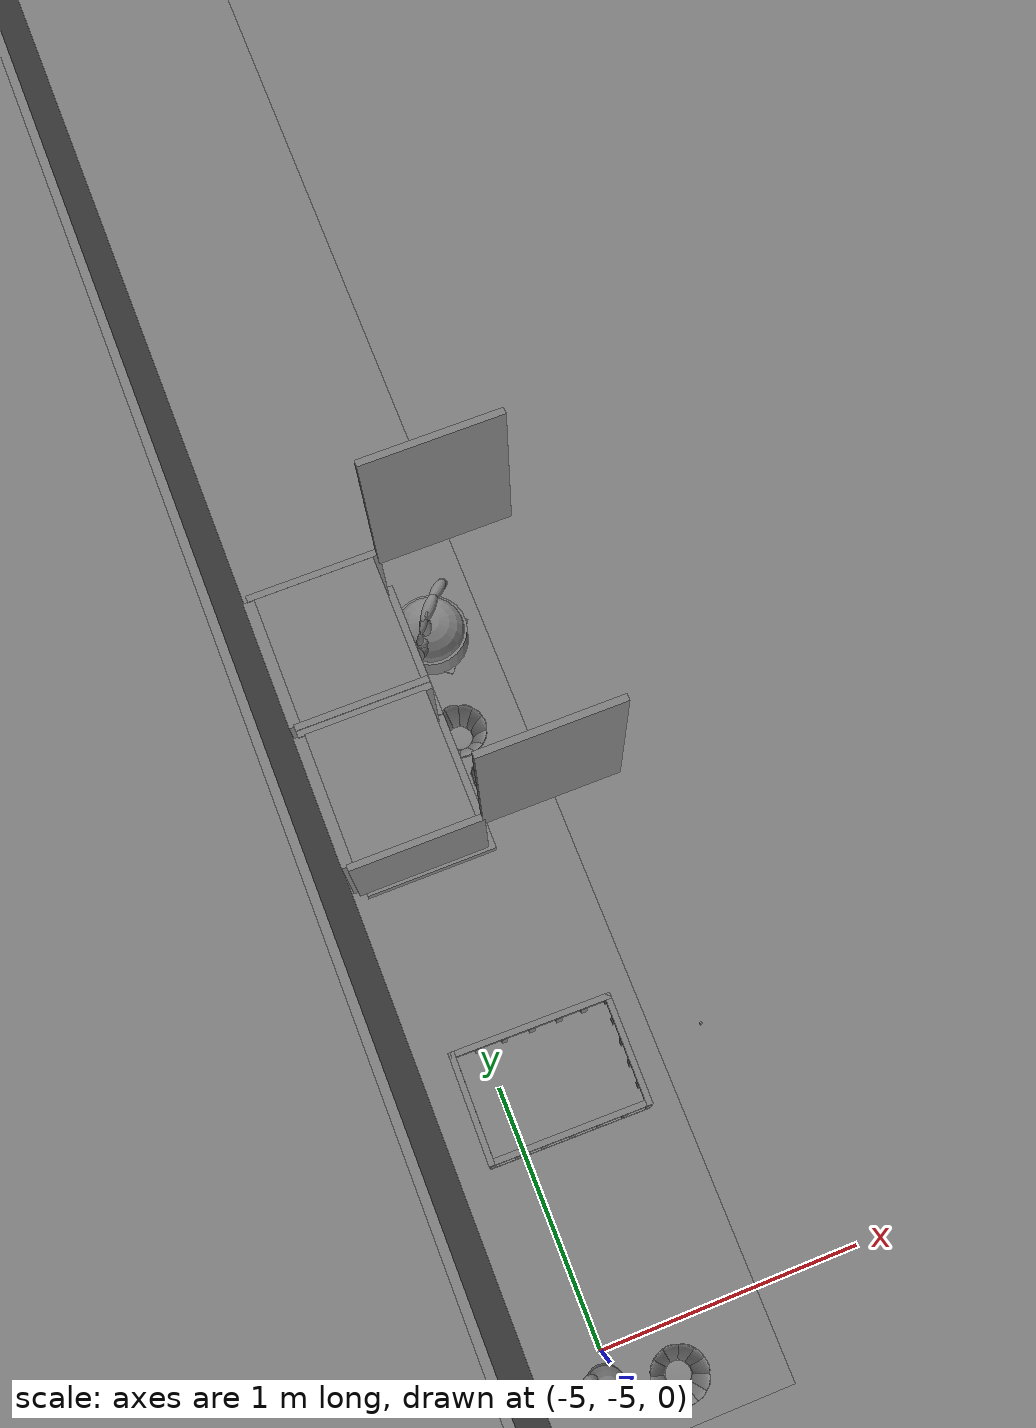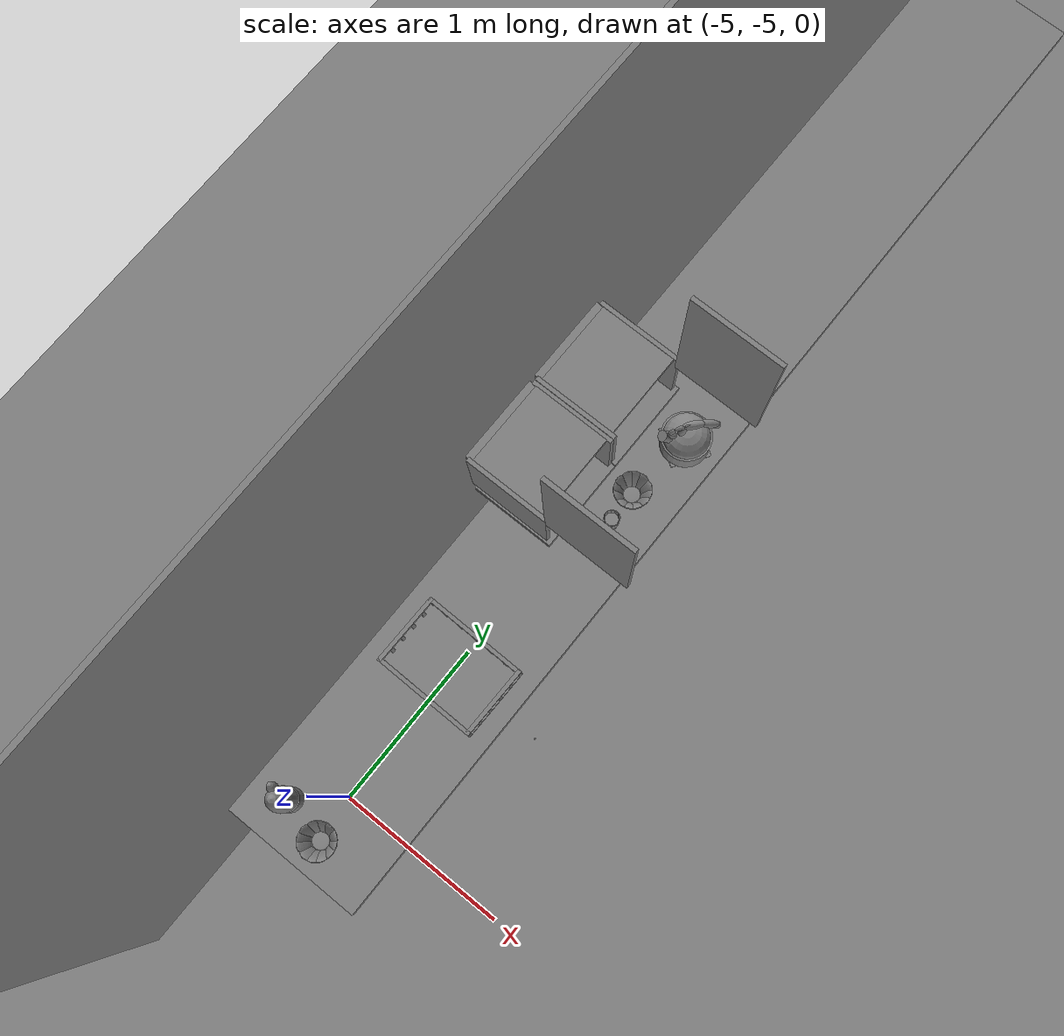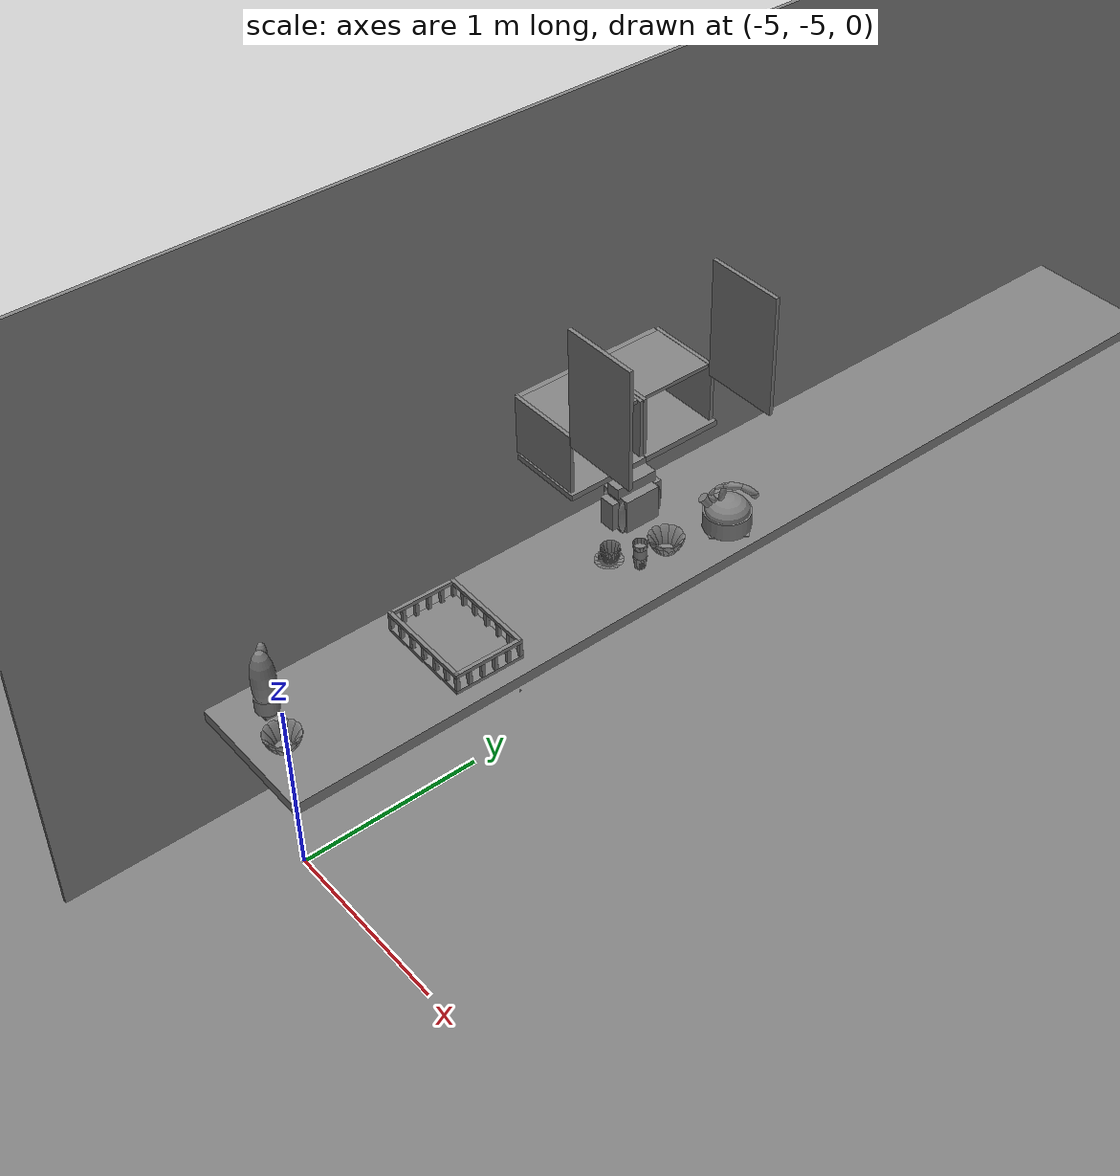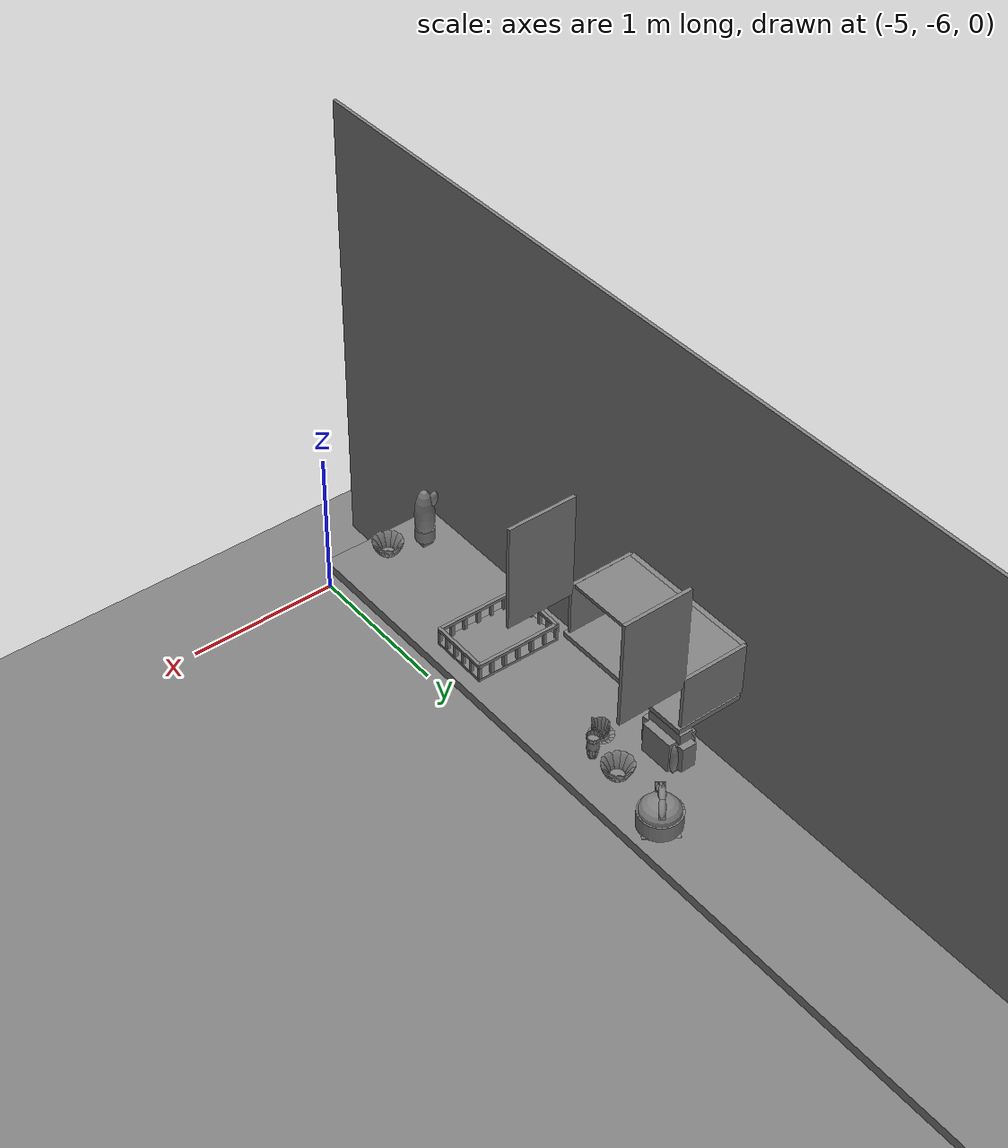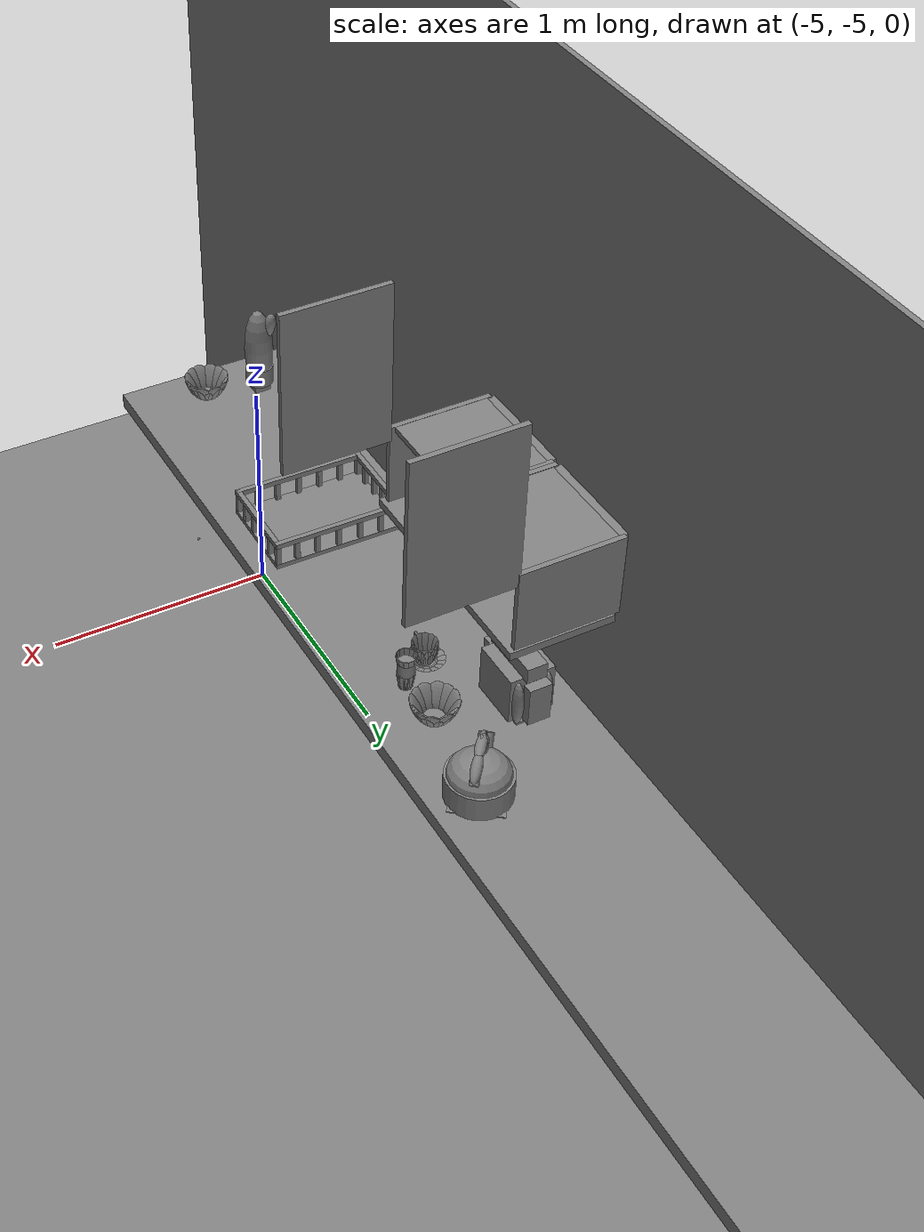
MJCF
<mujoco>
    <option gravity="0.000000000 0.000000000 -9.810000420" timestep="0.0049999999" integrator="implicitfast" density="9.8000002" viscosity="1.8000001e-05" noslip_iterations="10" iterations="100" sdf_iterations="50">
        <flag multiccd="disable"/>
    </option>
    <size memory="1000M"/>
    <compiler coordinate="local"/>
    <worldbody>
        <light cutoff="30" pos="0 1 1" dir="0 -1 -2"/>
        <light cutoff="30" pos="0 -1 1" dir="0 1 -2"/>
        <body pos="0.000000000 0.000000000 0.000000000" euler="0.000000000 0.000000000 0.000000000" name="Static Objcets_Static Objcets">
            <geom contype="1" conaffinity="1" density="1000" type="box" material="" rgba="0.500000000 0.500000000 0.500000000 1.000000000" solimp="0.899999976 0.949999988 0.001000000" friction="1.000000000 0.005000000 0.000100000" solref="0.020000000 1.000000000" margin="0" condim="3" group="0" pos="-4.999745846 -3.087441683 1.763863802" quat="0.707107067 0.707106471 0.000000000 0.000000000" size="0.200000003 0.159999996 0.010000000" name="Static Objcets_geom_086E6C26_D0D4_4C2B_9E91_075C3DC88CBA"/>
            <geom contype="1" conaffinity="1" density="1000" type="box" material="" rgba="0.500000000 0.500000000 0.500000000 1.000000000" solimp="0.899999976 0.949999988 0.001000000" friction="1.000000000 0.005000000 0.000100000" solref="0.020000000 1.000000000" margin="0" condim="3" group="0" pos="-5.189302921 -3.293644905 1.760152459" quat="0.707107067 0.707106471 0.000000000 0.000000000" size="0.025000000 0.159999996 0.200000003" name="Static Objcets_geom_2B82C54D_26F8_4D1C_BB5F_D3FA1BD33151"/>
            <geom contype="1" conaffinity="1" density="1000" type="box" material="" rgba="0.500000000 0.500000000 0.500000000 1.000000000" solimp="0.899999976 0.949999988 0.001000000" friction="1.000000000 0.005000000 0.000100000" solref="0.020000000 1.000000000" margin="0" condim="3" group="0" pos="-4.979488373 -3.297635794 1.591412544" quat="0.707106829 0.707106709 0.000000000 0.000000000" size="0.200000003 0.015000000 0.219999999" name="Static Objcets_geom_25F5D5AE_C1E6_4DD3_8C40_9E5779CEAC2B"/>
            <geom contype="1" conaffinity="1" density="1000" type="box" material="" rgba="0.500000000 0.500000000 0.500000000 1.000000000" solimp="0.899999976 0.949999988 0.001000000" friction="1.000000000 0.005000000 0.000100000" solref="0.020000000 1.000000000" margin="0" condim="3" group="0" pos="-4.999745846 -3.497932911 1.764780521" quat="0.707107067 0.707106471 0.000000000 0.000000000" size="0.200000003 0.159999996 0.010000000" name="Static Objcets_geom_4C785422_1936_4399_BB76_B76ABFA60AAE"/>
            <geom contype="1" conaffinity="1" density="1000" type="box" material="" rgba="0.500000000 0.500000000 0.500000000 1.000000000" solimp="0.899999976 0.949999988 0.001000000" friction="1.000000000 0.005000000 0.000100000" solref="0.020000000 1.000000000" margin="0" condim="3" group="0" pos="-5.000125408 -3.294431210 1.913951039" quat="0.707107067 0.707106471 0.000000000 0.000000000" size="0.180000007 0.010000000 0.200000003" name="Static Objcets_geom_2F53E180_4CDD_4291_83BB_CA1E06E81616"/>
            <geom contype="1" conaffinity="1" density="1000" type="box" material="" rgba="0.500000000 0.500000000 0.500000000 1.000000000" solimp="0.899999976 0.949999988 0.001000000" friction="1.000000000 0.005000000 0.000100000" solref="0.020000000 1.000000000" margin="0" condim="3" group="0" pos="-4.999745846 -3.066934109 1.765979409" quat="0.707107067 0.707106471 0.000000000 0.000000000" size="0.200000003 0.159999996 0.010000000" name="Static Objcets_geom_4F0C7ADA_9503_46F5_8B7C_B5AA99A51B10"/>
            <geom contype="1" conaffinity="1" density="1000" type="box" material="" rgba="0.500000000 0.500000000 0.500000000 1.000000000" solimp="0.899999976 0.949999988 0.001000000" friction="1.000000000 0.005000000 0.000100000" solref="0.020000000 1.000000000" margin="0" condim="3" group="0" pos="-5.189302921 -2.861564636 1.760152102" quat="0.707107067 0.707106471 0.000000000 0.000000000" size="0.025000000 0.159999996 0.200000003" name="Static Objcets_geom_0A3F9B66_69B1_4B59_82EB_587C84A395F7"/>
            <geom contype="1" conaffinity="1" density="1000" type="box" material="" rgba="0.500000000 0.500000000 0.500000000 1.000000000" solimp="0.899999976 0.949999988 0.001000000" friction="1.000000000 0.005000000 0.000100000" solref="0.020000000 1.000000000" margin="0" condim="3" group="0" pos="-5.000125408 -2.861802340 1.913950682" quat="0.707107067 0.707106471 0.000000000 0.000000000" size="0.180000007 0.010000000 0.200000003" name="Static Objcets_geom_CE2E9678_A4EA_4C76_9F48_9BF14A67022D"/>
            <geom contype="1" conaffinity="1" density="1000" type="box" material="" rgba="0.500000000 0.500000000 0.500000000 1.000000000" solimp="0.899999976 0.949999988 0.001000000" friction="1.000000000 0.005000000 0.000100000" solref="0.020000000 1.000000000" margin="0" condim="3" group="0" pos="-4.979488373 -2.855390549 1.591412187" quat="0.707106709 0.707106769 0.000000000 0.000000000" size="0.200000003 0.015000000 0.219999999" name="Static Objcets_geom_485E00EE_0BAD_4720_B1CA_43D14C55E8AC"/>
            <geom contype="1" conaffinity="1" density="1000" type="box" material="" rgba="0.500000000 0.500000000 0.500000000 1.000000000" solimp="0.899999976 0.949999988 0.001000000" friction="1.000000000 0.005000000 0.000100000" solref="0.020000000 1.000000000" margin="0" condim="3" group="0" pos="-4.999745846 -2.653569937 1.764779806" quat="0.707107067 0.707106471 0.000000000 0.000000000" size="0.200000003 0.159999996 0.010000000" name="Static Objcets_geom_786CD4B6_7754_47FD_AE1C_200F3583A261"/>
            <geom contype="1" conaffinity="1" density="1000" type="box" material="" rgba="0.500000000 0.500000000 0.500000000 1.000000000" solimp="0.899999976 0.949999988 0.001000000" friction="1.000000000 0.005000000 0.000100000" solref="0.020000000 1.000000000" margin="0" condim="3" group="0" pos="-0.720102787 0.222944975 -1.102830648" quat="0.000000954 1.000000000 0.000000000 0.000000000" size="8.000000000 8.000000000 0.010000000" name="Static Objcets_geom_8DC66B19_D71A_42F6_B0DE_F23B16B6108B"/>
            <geom contype="1" conaffinity="1" density="1000" type="box" material="" rgba="0.500000000 0.500000000 0.500000000 1.000000000" solimp="0.899999976 0.949999988 0.001000000" friction="1.000000000 0.005000000 0.000100000" solref="0.020000000 1.000000000" margin="0" condim="3" group="0" pos="-4.873187065 -2.461376429 0.977675021" quat="0.707107067 0.707106471 0.000000000 0.000000000" size="0.370000005 0.029999999 2.799999952" name="Static Objcets_geom_26B2DD9E_41F2_435A_AC99_271B9CB7E7BF"/>
            <geom contype="1" conaffinity="1" density="1000" type="box" material="" rgba="0.500000000 0.500000000 0.500000000 1.000000000" solimp="0.899999976 0.949999988 0.001000000" friction="1.000000000 0.005000000 0.000100000" solref="0.020000000 1.000000000" margin="0" condim="3" group="0" pos="-5.244853973 -2.375543594 1.820221663" quat="0.707107008 0.707106531 0.000000000 0.000000000" size="0.010000000 1.500000000 3.700000048" name="Static Objcets_geom_031A085D_2A50_4927_926C_0B7E113BE920"/>
        </body>
        <body pos="1000.000000000 1000.000000000 1.000000000" euler="0.000000000 0.000000000 0.000000000" name="openloong_gripper_2f85_fix_base_usda_coffeecup_white_kps">
            <geom contype="1" conaffinity="1" density="1000" type="capsule" material="" rgba="0.500000000 0.500000000 0.500000000 1.000000000" solimp="0.899999976 0.949999988 0.001000000" friction="1.000000000 0.005000000 0.000100000" solref="0.020000000 1.000000000" margin="0" condim="3" group="0" pos="-0.000854492 -0.065795898 0.050029993" quat="0.343559504 -0.613204718 0.626912475 0.336047262" size="0.004000000 0.005000000 1.000000000" name="openloong_gripper_2f85_fix_base_usda_geom_16FCD96B_9857_4BB8_B7F7_9E8D230B06D5"/>
            <geom contype="1" conaffinity="1" density="1000" type="ellipsoid" material="" rgba="0.500000000 0.500000000 0.500000000 1.000000000" solimp="0.899999976 0.949999988 0.001000000" friction="1.000000000 0.005000000 0.000100000" solref="0.020000000 1.000000000" margin="0" condim="3" group="0" pos="-0.000793457 -0.038452148 0.048040152" quat="0.711656272 0.066323131 -0.067805752 0.696095467" size="0.005000000 0.029999999 0.048999999" name="openloong_gripper_2f85_fix_base_usda_geom_59C7904D_9538_4A0B_A0B4_D0AEBCA43BC4"/>
            <geom contype="1" conaffinity="1" density="1000" type="ellipsoid" material="" rgba="0.500000000 0.500000000 0.500000000 1.000000000" solimp="0.899999976 0.949999988 0.001000000" friction="1.000000000 0.005000000 0.000100000" solref="0.020000000 1.000000000" margin="0" condim="3" group="0" pos="0.037719727 -0.001892090 0.048040152" quat="0.995387912 0.001371633 0.094835162 -0.014391154" size="0.005000000 0.029999999 0.048999999" name="openloong_gripper_2f85_fix_base_usda_geom_6FE9888E_B251_42E7_A750_E0673BC13782"/>
            <geom contype="1" conaffinity="1" density="1000" type="ellipsoid" material="" rgba="0.500000000 0.500000000 0.500000000 1.000000000" solimp="0.899999976 0.949999988 0.001000000" friction="1.000000000 0.005000000 0.000100000" solref="0.020000000 1.000000000" margin="0" condim="3" group="0" pos="0.033996582 0.015502930 0.048040152" quat="0.970659733 -0.021051638 0.092478797 0.220962167" size="0.005000000 0.029999999 0.048999999" name="openloong_gripper_2f85_fix_base_usda_geom_E45AE938_11AF_4337_9C6E_AB6792135867"/>
            <geom contype="1" conaffinity="1" density="1000" type="box" material="" rgba="0.500000000 0.500000000 0.500000000 1.000000000" solimp="0.899999976 0.949999988 0.001000000" friction="1.000000000 0.005000000 0.000100000" solref="0.020000000 1.000000000" margin="0" condim="3" group="0" pos="0.000793457 -0.000183105 0.000156164" quat="0.714879215 0.000000000 0.000000000 0.699247897" size="0.020000000 0.020000000 0.002000000" name="openloong_gripper_2f85_fix_base_usda_geom_43A083BD_8F11_4021_BF5B_A15FCAE32964"/>
            <geom contype="1" conaffinity="1" density="1000" type="ellipsoid" material="" rgba="0.500000000 0.500000000 0.500000000 1.000000000" solimp="0.899999976 0.949999988 0.001000000" friction="1.000000000 0.005000000 0.000100000" solref="0.020000000 1.000000000" margin="0" condim="3" group="0" pos="-0.019409180 -0.033081055 0.048040152" quat="0.866879702 0.046630561 -0.082595348 0.489411235" size="0.005000000 0.029999999 0.048999999" name="openloong_gripper_2f85_fix_base_usda_geom_B6A3A258_0B8D_4E91_BECE_2B138A74D863"/>
            <geom contype="1" conaffinity="1" density="1000" type="ellipsoid" material="" rgba="0.500000000 0.500000000 0.500000000 1.000000000" solimp="0.899999976 0.949999988 0.001000000" friction="1.000000000 0.005000000 0.000100000" solref="0.020000000 1.000000000" margin="0" condim="3" group="0" pos="-0.016052246 0.033264160 0.048040152" quat="0.840792537 -0.050782297 -0.080109790 -0.532983541" size="0.005000000 0.029999999 0.048999999" name="openloong_gripper_2f85_fix_base_usda_geom_2233BD0C_27E4_4D45_BF2B_F9C7369E978B"/>
            <geom contype="1" conaffinity="1" density="1000" type="capsule" material="" rgba="0.500000000 0.500000000 0.500000000 1.000000000" solimp="0.899999976 0.949999988 0.001000000" friction="1.000000000 0.005000000 0.000100000" solref="0.020000000 1.000000000" margin="0" condim="3" group="0" pos="-0.000549316 -0.053527832 0.046825886" quat="0.505496025 -0.494442940 0.505495846 0.494442940" size="0.004000000 0.005000000 1.000000000" name="openloong_gripper_2f85_fix_base_usda_geom_9F26C26B_B228_4A88_B3C9_D7D4AFA1DE8C"/>
            <geom contype="1" conaffinity="1" density="1000" type="ellipsoid" material="" rgba="0.500000000 0.500000000 0.500000000 1.000000000" solimp="0.899999976 0.949999988 0.001000000" friction="1.000000000 0.005000000 0.000100000" solref="0.020000000 1.000000000" margin="0" condim="3" group="0" pos="-0.032104492 0.018920898 0.048040152" quat="0.958129764 -0.025742561 -0.091288343 -0.270168930" size="0.005000000 0.029999999 0.048999999" name="openloong_gripper_2f85_fix_base_usda_geom_F90CF786_52BE_419D_8E25_157F5858C081"/>
            <geom contype="1" conaffinity="1" density="1000" type="ellipsoid" material="" rgba="0.500000000 0.500000000 0.500000000 1.000000000" solimp="0.899999976 0.949999988 0.001000000" friction="1.000000000 0.005000000 0.000100000" solref="0.020000000 1.000000000" margin="0" condim="3" group="0" pos="-0.037597656 0.000305176 0.048040152" quat="0.995387554 -0.001371440 -0.094839431 -0.014389008" size="0.005000000 0.029999999 0.048999999" name="openloong_gripper_2f85_fix_base_usda_geom_2D81D544_9A03_46E3_AF50_359C378F6641"/>
            <geom contype="1" conaffinity="1" density="1000" type="capsule" material="" rgba="0.500000000 0.500000000 0.500000000 1.000000000" solimp="0.899999976 0.949999988 0.001000000" friction="1.000000000 0.005000000 0.000100000" solref="0.020000000 1.000000000" margin="0" condim="3" group="0" pos="-0.000366211 -0.043762207 0.044118762" quat="0.260488123 -0.651174724 0.665731549 0.254792154" size="0.004000000 0.003000000 1.000000000" name="openloong_gripper_2f85_fix_base_usda_geom_3C5F5FDA_5829_44D1_B28F_9754AF90D154"/>
            <geom contype="1" conaffinity="1" density="1000" type="capsule" material="" rgba="0.500000000 0.500000000 0.500000000 1.000000000" solimp="0.899999976 0.949999988 0.001000000" friction="1.000000000 0.005000000 0.000100000" solref="0.020000000 1.000000000" margin="0" condim="3" group="0" pos="-0.000915527 -0.068542480 0.082936406" quat="0.624995589 -0.339446366 0.347034454 0.611329615" size="0.004000000 0.004000000 1.000000000" name="openloong_gripper_2f85_fix_base_usda_geom_9F1054B8_8B85_4DB8_AF89_1D459D5CAE1E"/>
            <geom contype="1" conaffinity="1" density="1000" type="ellipsoid" material="" rgba="0.500000000 0.500000000 0.500000000 1.000000000" solimp="0.899999976 0.949999988 0.001000000" friction="1.000000000 0.005000000 0.000100000" solref="0.020000000 1.000000000" margin="0" condim="3" group="0" pos="0.016113281 -0.034851074 0.048040152" quat="0.840793252 0.050779939 0.080106191 -0.532983422" size="0.005000000 0.029999999 0.048999999" name="openloong_gripper_2f85_fix_base_usda_geom_C232907F_A0A2_4BAC_B4FE_A02DBD9F1457"/>
            <geom contype="1" conaffinity="1" density="1000" type="ellipsoid" material="" rgba="0.500000000 0.500000000 0.500000000 1.000000000" solimp="0.899999976 0.949999988 0.001000000" friction="1.000000000 0.005000000 0.000100000" solref="0.020000000 1.000000000" margin="0" condim="3" group="0" pos="0.000854492 0.036865234 0.048040152" quat="0.711656570 -0.066320375 0.067802906 0.696095705" size="0.005000000 0.029999999 0.048999999" name="openloong_gripper_2f85_fix_base_usda_geom_069F29BE_5135_469F_9C6C_5F76240BBB29"/>
            <geom contype="1" conaffinity="1" density="1000" type="ellipsoid" material="" rgba="0.500000000 0.500000000 0.500000000 1.000000000" solimp="0.899999976 0.949999988 0.001000000" friction="1.000000000 0.005000000 0.000100000" solref="0.020000000 1.000000000" margin="0" condim="3" group="0" pos="-0.033935547 -0.017089844 0.048040152" quat="0.970659137 0.021052625 -0.092483103 0.220962465" size="0.005000000 0.029999999 0.048999999" name="openloong_gripper_2f85_fix_base_usda_geom_0E1F91D3_219A_4A0F_81E5_9DBFE3776E65"/>
            <geom contype="1" conaffinity="1" density="1000" type="ellipsoid" material="" rgba="0.500000000 0.500000000 0.500000000 1.000000000" solimp="0.899999976 0.949999988 0.001000000" friction="1.000000000 0.005000000 0.000100000" solref="0.020000000 1.000000000" margin="0" condim="3" group="0" pos="0.019531250 0.031494141 0.048040152" quat="0.866880119 -0.046628602 0.082591817 0.489411235" size="0.005000000 0.029999999 0.048999999" name="openloong_gripper_2f85_fix_base_usda_geom_2A19AD44_D9AE_4F97_A9E9_D99D827CEFC4"/>
            <geom contype="1" conaffinity="1" density="1000" type="ellipsoid" material="" rgba="0.500000000 0.500000000 0.500000000 1.000000000" solimp="0.899999976 0.949999988 0.001000000" friction="1.000000000 0.005000000 0.000100000" solref="0.020000000 1.000000000" margin="0" condim="3" group="0" pos="0.032165527 -0.020507812 0.048040152" quat="0.958128154 0.025740955 0.091285400 -0.270175666" size="0.005000000 0.029999999 0.048999999" name="openloong_gripper_2f85_fix_base_usda_geom_EAE70513_F74E_4C81_BCE1_CF64511F198B"/>
            <geom contype="1" conaffinity="1" density="1000" type="capsule" material="" rgba="0.500000000 0.500000000 0.500000000 1.000000000" solimp="0.899999976 0.949999988 0.001000000" friction="1.000000000 0.005000000 0.000100000" solref="0.020000000 1.000000000" margin="0" condim="3" group="0" pos="-0.000610352 -0.056823730 0.083572865" quat="0.452654332 -0.541215360 0.553313971 0.442756712" size="0.004000000 0.009000000 1.000000000" name="openloong_gripper_2f85_fix_base_usda_geom_7602F260_1292_4660_B9B8_48197ACC6998"/>
            <geom contype="1" conaffinity="1" density="1000" type="ellipsoid" material="" rgba="0.500000000 0.500000000 0.500000000 1.000000000" solimp="0.899999976 0.949999988 0.001000000" friction="1.000000000 0.005000000 0.000100000" solref="0.020000000 1.000000000" margin="0" condim="3" group="0" pos="0.000061035 -0.000183105 0.001848221" quat="0.714879215 0.000000000 0.000000000 0.699247897" size="0.029999999 0.029999999 0.001000000" name="openloong_gripper_2f85_fix_base_usda_geom_CF558396_8E1A_432B_A67C_71331921F80B"/>
            <geom contype="1" conaffinity="1" density="1000" type="capsule" material="" rgba="0.500000000 0.500000000 0.500000000 1.000000000" solimp="0.899999976 0.949999988 0.001000000" friction="1.000000000 0.005000000 0.000100000" solref="0.020000000 1.000000000" margin="0" condim="3" group="0" pos="-0.000976562 -0.071838379 0.066101432" quat="0.031849027 -0.698553741 0.714169443 0.031152546" size="0.004000000 0.012000000 1.000000000" name="openloong_gripper_2f85_fix_base_usda_geom_DD19F87E_4F53_4A65_A432_3768455255AE"/>
            <freejoint name="openloong_gripper_2f85_fix_base_usda_coffeecup_white_kps_joint"/>
            <site size="0.005000000 0.005000000 0.005000000" rgba="0.500000000 0.500000000 0.500000000 1.000000000" pos="0.000000000 0.000000000 0.000000000" quat="0.999961913 0.008726534 0.000000000 0.000000000" group="0" type="sphere" name="openloong_gripper_2f85_fix_base_usda_coffeecup_white_kps"/>
        </body>
        <body pos="-4.016890526 -4.393032551 1.886851907" euler="56.361804962 -34.302719116 105.416007996" mocap="true" name="spotlight1_SpotLight"/>
        <body pos="-4.082475662 -4.001289368 1.841594577" euler="117.528945923 -35.889785767 -121.618942261" mocap="true" name="spotlight5_SpotLight"/>
        <body pos="1000.000000000 1000.000000000 1.000000000" euler="0.000000000 0.000000000 0.000000000" name="openloong_gripper_2f85_fix_base_usda_jar_01">
            <geom contype="1" conaffinity="1" density="1000" type="box" material="" rgba="0.500000000 0.500000000 0.500000000 1.000000000" solimp="0.899999976 0.949999988 0.001000000" friction="1.000000000 0.005000000 0.000100000" solref="0.020000000 1.000000000" margin="0" condim="3" group="0" pos="0.000000000 0.000000000 0.006158113" quat="1.000000000 0.000000000 0.000000000 0.000000000" size="0.020000000 0.020000000 0.005000000" name="openloong_gripper_2f85_fix_base_usda_geom_66B3BB42_C46A_44F6_AC04_D50CD9DECD68"/>
            <geom contype="1" conaffinity="1" density="1000" type="cylinder" material="" rgba="0.500000000 0.500000000 0.500000000 1.000000000" solimp="0.899999976 0.949999988 0.001000000" friction="1.000000000 0.005000000 0.000100000" solref="0.020000000 1.000000000" margin="0" condim="3" group="0" pos="0.000000000 0.000000000 0.062744498" quat="1.000000000 0.000000000 0.000000000 0.000000000" size="0.041000001 0.052999999 1.000000000" name="openloong_gripper_2f85_fix_base_usda_geom_A28C5C0D_5390_4EAA_9A5F_90B27C79D985"/>
            <geom contype="1" conaffinity="1" density="1000" type="ellipsoid" material="" rgba="0.500000000 0.500000000 0.500000000 1.000000000" solimp="0.899999976 0.949999988 0.001000000" friction="1.000000000 0.005000000 0.000100000" solref="0.020000000 1.000000000" margin="0" condim="3" group="0" pos="0.000000000 0.000000000 0.122252703" quat="1.000000000 0.000000000 0.000000000 0.000000000" size="0.035999998 0.035999998 0.010000000" name="openloong_gripper_2f85_fix_base_usda_geom_F125B895_9BF2_4F04_BA59_CEEAC90FA2E7"/>
            <geom contype="1" conaffinity="1" density="1000" type="cylinder" material="" rgba="0.500000000 0.500000000 0.500000000 1.000000000" solimp="0.899999976 0.949999988 0.001000000" friction="1.000000000 0.005000000 0.000100000" solref="0.020000000 1.000000000" margin="0" condim="3" group="0" pos="0.000000000 0.000000000 0.015747190" quat="1.000000000 0.000000000 0.000000000 0.000000000" size="0.035000000 0.010000000 1.000000000" name="openloong_gripper_2f85_fix_base_usda_geom_484BFC95_A576_4F69_97FD_A38A1C53F4B5"/>
            <geom contype="1" conaffinity="1" density="1000" type="ellipsoid" material="" rgba="0.500000000 0.500000000 0.500000000 1.000000000" solimp="0.899999976 0.949999988 0.001000000" friction="1.000000000 0.005000000 0.000100000" solref="0.020000000 1.000000000" margin="0" condim="3" group="0" pos="0.000000000 0.000000000 0.115815401" quat="1.000000000 0.000000000 0.000000000 0.000000000" size="0.039999999 0.039999999 0.010000000" name="openloong_gripper_2f85_fix_base_usda_geom_AE49A518_CD70_4C79_A5F6_17FCADA11600"/>
            <geom contype="1" conaffinity="1" density="1000" type="cylinder" material="" rgba="0.500000000 0.500000000 0.500000000 1.000000000" solimp="0.899999976 0.949999988 0.001000000" friction="1.000000000 0.005000000 0.000100000" solref="0.020000000 1.000000000" margin="0" condim="3" group="0" pos="0.000000000 0.000000000 0.133183479" quat="1.000000000 0.000000000 0.000000000 0.000000000" size="0.037999999 0.006500000 1.000000000" name="openloong_gripper_2f85_fix_base_usda_geom_A2340CD5_4A90_43BC_AFB9_EA0B2A37A2C9"/>
            <freejoint name="openloong_gripper_2f85_fix_base_usda_jar_01_joint"/>
            <site size="0.005000000 0.005000000 0.005000000" rgba="0.500000000 0.500000000 0.500000000 1.000000000" pos="0.000000000 0.000000000 0.000000000" quat="1.000000000 0.000000000 0.000000000 0.000000000" group="0" type="sphere" name="openloong_gripper_2f85_fix_base_usda_jar_01site"/>
        </body>
        <body pos="1000.000000000 1000.000000000 1.000000000" euler="0.000000000 0.000000000 0.000000000" name="openloong_gripper_2f85_fix_base_usda_bottle_red">
            <geom contype="1" conaffinity="1" density="1000" type="ellipsoid" material="" rgba="0.500000000 0.500000000 0.500000000 1.000000000" solimp="0.899999976 0.949999988 0.001000000" friction="1.000000000 0.005000000 0.000100000" solref="0.020000000 1.000000000" margin="0" condim="3" group="0" pos="0.000000000 0.000000000 0.144284487" quat="1.000000000 0.000000000 0.000000000 0.000000000" size="0.021000000 0.021000000 0.079999998" name="openloong_gripper_2f85_fix_base_usda_geom_83CC4C93_E3CE_478A_8FA1_9B0F8A3AD658"/>
            <geom contype="1" conaffinity="1" density="1000" type="cylinder" material="" rgba="0.500000000 0.500000000 0.500000000 1.000000000" solimp="0.899999976 0.949999988 0.001000000" friction="1.000000000 0.005000000 0.000100000" solref="0.020000000 1.000000000" margin="0" condim="3" group="0" pos="0.000000000 0.000000000 0.220618963" quat="1.000000000 0.000000000 0.000000000 0.000000000" size="0.016000001 0.010000000 1.000000000" name="openloong_gripper_2f85_fix_base_usda_geom_7AE028A1_CD58_47AA_A9AC_C2F33B5E1AEE"/>
            <geom contype="1" conaffinity="1" density="1000" type="ellipsoid" material="" rgba="0.500000000 0.500000000 0.500000000 1.000000000" solimp="0.899999976 0.949999988 0.001000000" friction="1.000000000 0.005000000 0.000100000" solref="0.020000000 1.000000000" margin="0" condim="3" group="0" pos="0.000000000 0.000000000 0.118945479" quat="1.000000000 0.000000000 0.000000000 0.000000000" size="0.030999999 0.030999999 0.029999999" name="openloong_gripper_2f85_fix_base_usda_geom_AEBBC065_34FC_454D_A058_AE5987CAECC0"/>
            <geom contype="1" conaffinity="1" density="1000" type="box" material="" rgba="0.500000000 0.500000000 0.500000000 1.000000000" solimp="0.899999976 0.949999988 0.001000000" friction="1.000000000 0.005000000 0.000100000" solref="0.020000000 1.000000000" margin="0" condim="3" group="0" pos="0.000000000 0.000000000 0.002189159" quat="1.000000000 0.000000000 0.000000000 0.000000000" size="0.020000000 0.020000000 0.003000000" name="openloong_gripper_2f85_fix_base_usda_geom_AAFB8606_9574_4871_AFA2_D1D1DCB82368"/>
            <geom contype="1" conaffinity="1" density="1000" type="cylinder" material="" rgba="0.500000000 0.500000000 0.500000000 1.000000000" solimp="0.899999976 0.949999988 0.001000000" friction="1.000000000 0.005000000 0.000100000" solref="0.020000000 1.000000000" margin="0" condim="3" group="0" pos="0.000000000 -0.000366211 0.060884237" quat="1.000000000 0.000000000 0.000000000 0.000000000" size="0.030999999 0.057999998 1.000000000" name="openloong_gripper_2f85_fix_base_usda_geom_C305417A_E3B7_4D72_B934_CC4D152B5E84"/>
            <freejoint name="openloong_gripper_2f85_fix_base_usda_bottle_red_joint"/>
            <site size="0.005000000 0.005000000 0.005000000" rgba="0.500000000 0.500000000 0.500000000 1.000000000" pos="0.000000000 0.000000000 0.000000000" quat="0.999961913 0.008726535 0.000000000 0.000000000" group="0" type="sphere" name="openloong_gripper_2f85_fix_base_usda_bottle_redsite"/>
        </body>
        <body pos="-4.056719303 -3.758129835 1.903193116" euler="-38.154178619 -8.809378624 -170.843490601" mocap="true" name="spotlight6_SpotLight"/>
        <body pos="1000.000000000 1000.000000000 1.000000000" euler="0.000000000 0.000000000 0.000000000" name="openloong_gripper_2f85_fix_base_usda_salt">
            <geom contype="1" conaffinity="1" density="1000" type="box" material="" rgba="0.500000000 0.500000000 0.500000000 1.000000000" solimp="0.899999976 0.949999988 0.001000000" friction="1.000000000 0.005000000 0.000100000" solref="0.020000000 1.000000000" margin="0" condim="3" group="0" pos="0.000305176 0.000000000 0.084862232" quat="1.000000000 0.000000000 0.000000000 0.000000000" size="0.048999999 0.018999999 0.005000000" name="openloong_gripper_2f85_fix_base_usda_geom_037FD964_C1B5_4F9B_AEA6_CAA2475B9633"/>
            <geom contype="1" conaffinity="1" density="1000" type="box" material="" rgba="0.500000000 0.500000000 0.500000000 1.000000000" solimp="0.899999976 0.949999988 0.001000000" friction="1.000000000 0.005000000 0.000100000" solref="0.020000000 1.000000000" margin="0" condim="3" group="0" pos="0.000305176 0.000000000 0.104564309" quat="1.000000000 0.000000000 0.000000000 0.000000000" size="0.052000001 0.014000000 0.005000000" name="openloong_gripper_2f85_fix_base_usda_geom_2516FF41_D8AF_4C64_B4E5_D94D2D354E23"/>
            <geom contype="1" conaffinity="1" density="1000" type="box" material="" rgba="0.500000000 0.500000000 0.500000000 1.000000000" solimp="0.899999976 0.949999988 0.001000000" friction="1.000000000 0.005000000 0.000100000" solref="0.020000000 1.000000000" margin="0" condim="3" group="0" pos="0.000305176 0.000000000 0.114487171" quat="1.000000000 0.000000000 0.000000000 0.000000000" size="0.054000001 0.011500000 0.005000000" name="openloong_gripper_2f85_fix_base_usda_geom_8F42A452_4EF3_47BA_8FCE_2E1F339D943A"/>
            <geom contype="1" conaffinity="1" density="1000" type="box" material="" rgba="0.500000000 0.500000000 0.500000000 1.000000000" solimp="0.899999976 0.949999988 0.001000000" friction="1.000000000 0.005000000 0.000100000" solref="0.020000000 1.000000000" margin="0" condim="3" group="0" pos="0.000305176 0.000000000 0.075103164" quat="1.000000000 0.000000000 0.000000000 0.000000000" size="0.048000000 0.020000000 0.005000000" name="openloong_gripper_2f85_fix_base_usda_geom_02464C08_E56B_4A6D_AE69_D40E50188968"/>
            <geom contype="1" conaffinity="1" density="1000" type="box" material="" rgba="0.500000000 0.500000000 0.500000000 1.000000000" solimp="0.899999976 0.949999988 0.001000000" friction="1.000000000 0.005000000 0.000100000" solref="0.020000000 1.000000000" margin="0" condim="3" group="0" pos="0.000305176 0.000000000 0.134892464" quat="1.000000000 0.000000000 0.000000000 0.000000000" size="0.057000000 0.007000000 0.005000000" name="openloong_gripper_2f85_fix_base_usda_geom_8089101C_4A0D_42E1_B1F0_9F310D409EF2"/>
            <geom contype="1" conaffinity="1" density="1000" type="box" material="" rgba="0.500000000 0.500000000 0.500000000 1.000000000" solimp="0.899999976 0.949999988 0.001000000" friction="1.000000000 0.005000000 0.000100000" solref="0.020000000 1.000000000" margin="0" condim="3" group="0" pos="0.000305176 0.000000000 0.094920278" quat="1.000000000 0.000000000 0.000000000 0.000000000" size="0.050000001 0.017000001 0.005000000" name="openloong_gripper_2f85_fix_base_usda_geom_DBB3AECA_C7F5_4E3A_A084_7FCB4D049B31"/>
            <geom contype="1" conaffinity="1" density="1000" type="box" material="" rgba="0.500000000 0.500000000 0.500000000 1.000000000" solimp="0.899999976 0.949999988 0.001000000" friction="1.000000000 0.005000000 0.000100000" solref="0.020000000 1.000000000" margin="0" condim="3" group="0" pos="0.000305176 0.000000000 0.065204859" quat="1.000000000 0.000000000 0.000000000 0.000000000" size="0.045000002 0.021000000 0.005000000" name="openloong_gripper_2f85_fix_base_usda_geom_E7CA0693_21C5_4FD6_B0ED_0F887E4BB7E3"/>
            <geom contype="1" conaffinity="1" density="1000" type="box" material="" rgba="0.500000000 0.500000000 0.500000000 1.000000000" solimp="0.899999976 0.949999988 0.001000000" friction="1.000000000 0.005000000 0.000100000" solref="0.020000000 1.000000000" margin="0" condim="3" group="0" pos="0.000305176 0.000000000 0.144135714" quat="1.000000000 0.000000000 0.000000000 0.000000000" size="0.059000000 0.005000000 0.004000000" name="openloong_gripper_2f85_fix_base_usda_geom_DBE1E607_D8FF_46EC_8DD7_2A2622B10562"/>
            <geom contype="1" conaffinity="1" density="1000" type="box" material="" rgba="0.500000000 0.500000000 0.500000000 1.000000000" solimp="0.899999976 0.949999988 0.001000000" friction="1.000000000 0.005000000 0.000100000" solref="0.020000000 1.000000000" margin="0" condim="3" group="0" pos="0.000000000 0.000000000 0.031593561" quat="1.000000000 0.000000000 0.000000000 0.000000000" size="0.041999999 0.024000000 0.029999999" name="openloong_gripper_2f85_fix_base_usda_geom_B6F569F4_0733_494C_8445_666FD8D8F315"/>
            <geom contype="1" conaffinity="1" density="1000" type="box" material="" rgba="0.500000000 0.500000000 0.500000000 1.000000000" solimp="0.899999976 0.949999988 0.001000000" friction="1.000000000 0.005000000 0.000100000" solref="0.020000000 1.000000000" margin="0" condim="3" group="0" pos="0.000305176 0.000000000 0.124608755" quat="1.000000000 0.000000000 0.000000000 0.000000000" size="0.055000000 0.008000000 0.005000000" name="openloong_gripper_2f85_fix_base_usda_geom_BE6A3B99_12EF_407D_AB19_7089CA4DD455"/>
            <freejoint name="openloong_gripper_2f85_fix_base_usda_salt_joint"/>
            <site size="0.005000000 0.005000000 0.005000000" rgba="0.500000000 0.500000000 0.500000000 1.000000000" pos="0.000000000 0.000000000 0.000000000" quat="1.000000000 0.000000000 0.000000000 0.000000000" group="0" type="sphere" name="openloong_gripper_2f85_fix_base_usda_saltsite"/>
        </body>
        <body pos="1000.000000000 1000.000000000 1.000000000" euler="0.000000000 0.000000000 0.000000000" name="openloong_gripper_2f85_fix_base_usda_bow_yellow_kps">
            <geom contype="1" conaffinity="1" density="1000" type="ellipsoid" material="" rgba="0.500000000 0.500000000 0.500000000 1.000000000" solimp="0.899999976 0.949999988 0.001000000" friction="1.000000000 0.005000000 0.000100000" solref="0.020000000 1.000000000" margin="0" condim="3" group="0" pos="-0.052185059 0.040283203 0.044118762" quat="0.919264615 -0.076883033 -0.225593656 -0.313287765" size="0.010000000 0.039999999 0.052000001" name="openloong_gripper_2f85_fix_base_usda_geom_B3AB44F8_D4F5_4754_8AE6_43913C734E35"/>
            <geom contype="1" conaffinity="1" density="1000" type="ellipsoid" material="" rgba="0.500000000 0.500000000 0.500000000 1.000000000" solimp="0.899999976 0.949999988 0.001000000" friction="1.000000000 0.005000000 0.000100000" solref="0.020000000 1.000000000" margin="0" condim="3" group="0" pos="-0.000061035 0.065979004 0.044118762" quat="0.687598765 -0.168314874 -0.168741167 -0.685860336" size="0.010000000 0.039999999 0.052000001" name="openloong_gripper_2f85_fix_base_usda_geom_C048B555_D147_46ED_998D_328AE92CD323"/>
            <geom contype="1" conaffinity="1" density="1000" type="box" material="" rgba="0.500000000 0.500000000 0.500000000 1.000000000" solimp="0.899999976 0.949999988 0.001000000" friction="1.000000000 0.005000000 0.000100000" solref="0.020000000 1.000000000" margin="0" condim="3" group="0" pos="0.000061035 0.000000000 -0.002001643" quat="1.000000000 0.000000000 0.000000000 0.000000000" size="0.029999999 0.029999999 0.002000000" name="openloong_gripper_2f85_fix_base_usda_geom_9F7B09F9_7C16_4FA6_9CFB_B1BE1C82B583"/>
            <geom contype="1" conaffinity="1" density="1000" type="ellipsoid" material="" rgba="0.500000000 0.500000000 0.500000000 1.000000000" solimp="0.899999976 0.949999988 0.001000000" friction="1.000000000 0.005000000 0.000100000" solref="0.020000000 1.000000000" margin="0" condim="3" group="0" pos="0.029418945 -0.059082031 0.044118762" quat="0.825555861 0.125530601 0.202597082 -0.511521280" size="0.010000000 0.039999999 0.052000001" name="openloong_gripper_2f85_fix_base_usda_geom_C95EF351_B1E4_4402_9EFA_7D1A793A2F41"/>
            <geom contype="1" conaffinity="1" density="1000" type="ellipsoid" material="" rgba="0.500000000 0.500000000 0.500000000 1.000000000" solimp="0.899999976 0.949999988 0.001000000" friction="1.000000000 0.005000000 0.000100000" solref="0.020000000 1.000000000" margin="0" condim="3" group="0" pos="0.000244141 -0.065979004 0.044118762" quat="0.687598765 0.168314651 0.168741375 -0.685860336" size="0.010000000 0.039999999 0.052000001" name="openloong_gripper_2f85_fix_base_usda_geom_D5953C61_0A71_433E_9888_635492FB134D"/>
            <geom contype="1" conaffinity="1" density="1000" type="ellipsoid" material="" rgba="0.500000000 0.500000000 0.500000000 1.000000000" solimp="0.899999976 0.949999988 0.001000000" friction="1.000000000 0.005000000 0.000100000" solref="0.020000000 1.000000000" margin="0" condim="3" group="0" pos="0.000061035 0.000000000 0.000446677" quat="1.000000000 0.000000000 0.000000000 0.000000000" size="0.039999999 0.039999999 0.002000000" name="openloong_gripper_2f85_fix_base_usda_geom_63DAD4CD_882F_45AC_82B6_008FDA9B413C"/>
            <geom contype="1" conaffinity="1" density="1000" type="ellipsoid" material="" rgba="0.500000000 0.500000000 0.500000000 1.000000000" solimp="0.899999976 0.949999988 0.001000000" friction="1.000000000 0.005000000 0.000100000" solref="0.020000000 1.000000000" margin="0" condim="3" group="0" pos="0.059082031 0.029541016 0.044118762" quat="0.223252773 -0.231952220 -0.054787423 -0.945174456" size="0.010000000 0.039999999 0.052000001" name="openloong_gripper_2f85_fix_base_usda_geom_A42CF002_9FF2_4352_B6C1_633AA20BE87E"/>
            <geom contype="1" conaffinity="1" density="1000" type="ellipsoid" material="" rgba="0.500000000 0.500000000 0.500000000 1.000000000" solimp="0.899999976 0.949999988 0.001000000" friction="1.000000000 0.005000000 0.000100000" solref="0.020000000 1.000000000" margin="0" condim="3" group="0" pos="0.000061035 0.000000000 0.007335305" quat="1.000000000 0.000000000 0.000000000 0.000000000" size="0.039999999 0.039999999 0.002000000" name="openloong_gripper_2f85_fix_base_usda_geom_BED04675_B405_4AE1_BF75_31176AA2FD0C"/>
            <geom contype="1" conaffinity="1" density="1000" type="ellipsoid" material="" rgba="0.500000000 0.500000000 0.500000000 1.000000000" solimp="0.899999976 0.949999988 0.001000000" friction="1.000000000 0.005000000 0.000100000" solref="0.020000000 1.000000000" margin="0" condim="3" group="0" pos="-0.029296875 0.059082031 0.044118762" quat="0.825555861 -0.125530809 -0.202596918 -0.511521280" size="0.010000000 0.039999999 0.052000001" name="openloong_gripper_2f85_fix_base_usda_geom_4C56FFC6_E7EF_4553_961D_5BAEB672B197"/>
            <geom contype="1" conaffinity="1" density="1000" type="ellipsoid" material="" rgba="0.500000000 0.500000000 0.500000000 1.000000000" solimp="0.899999976 0.949999988 0.001000000" friction="1.000000000 0.005000000 0.000100000" solref="0.020000000 1.000000000" margin="0" condim="3" group="0" pos="0.040222168 0.052368164 0.044118762" quat="0.429593176 -0.213750049 -0.105424821 -0.871002972" size="0.010000000 0.039999999 0.052000001" name="openloong_gripper_2f85_fix_base_usda_geom_B976A312_06E3_446F_8C60_C1985313BC4B"/>
            <geom contype="1" conaffinity="1" density="1000" type="ellipsoid" material="" rgba="0.500000000 0.500000000 0.500000000 1.000000000" solimp="0.899999976 0.949999988 0.001000000" friction="1.000000000 0.005000000 0.000100000" solref="0.020000000 1.000000000" margin="0" condim="3" group="0" pos="0.066040039 0.000000000 0.044118762" quat="0.971183062 -0.000000156 0.238334835 0.000000030" size="0.010000000 0.039999999 0.052000001" name="openloong_gripper_2f85_fix_base_usda_geom_A98CE7C0_BE3D_4D15_8B5A_CD66319D1D4D"/>
            <geom contype="1" conaffinity="1" density="1000" type="ellipsoid" material="" rgba="0.500000000 0.500000000 0.500000000 1.000000000" solimp="0.899999976 0.949999988 0.001000000" friction="1.000000000 0.005000000 0.000100000" solref="0.020000000 1.000000000" margin="0" condim="3" group="0" pos="0.052307129 -0.040283203 0.044118762" quat="0.919264674 0.076882750 0.225593731 -0.313287705" size="0.010000000 0.039999999 0.052000001" name="openloong_gripper_2f85_fix_base_usda_geom_4C066A96_5585_4C55_94DC_53F4CFCF15F4"/>
            <geom contype="1" conaffinity="1" density="1000" type="ellipsoid" material="" rgba="0.500000000 0.500000000 0.500000000 1.000000000" solimp="0.899999976 0.949999988 0.001000000" friction="1.000000000 0.005000000 0.000100000" solref="0.020000000 1.000000000" margin="0" condim="3" group="0" pos="-0.065917969 0.000000000 0.044118762" quat="0.971183062 -0.000000142 -0.238334835 0.000000030" size="0.010000000 0.039999999 0.052000001" name="openloong_gripper_2f85_fix_base_usda_geom_DAAD3BD0_9BF3_4BB7_AD40_E88CEF1582B3"/>
            <geom contype="1" conaffinity="1" density="1000" type="ellipsoid" material="" rgba="0.500000000 0.500000000 0.500000000 1.000000000" solimp="0.899999976 0.949999988 0.001000000" friction="1.000000000 0.005000000 0.000100000" solref="0.020000000 1.000000000" margin="0" condim="3" group="0" pos="-0.058898926 -0.029541016 0.044118762" quat="0.223252758 0.231952101 0.054787733 -0.945174575" size="0.010000000 0.039999999 0.052000001" name="openloong_gripper_2f85_fix_base_usda_geom_64B3A30C_56BD_46B3_9C73_D294FD6F1706"/>
            <geom contype="1" conaffinity="1" density="1000" type="ellipsoid" material="" rgba="0.500000000 0.500000000 0.500000000 1.000000000" solimp="0.899999976 0.949999988 0.001000000" friction="1.000000000 0.005000000 0.000100000" solref="0.020000000 1.000000000" margin="0" condim="3" group="0" pos="-0.040100098 -0.052368164 0.044118762" quat="0.429593235 0.213749886 0.105425082 -0.871003032" size="0.010000000 0.039999999 0.052000001" name="openloong_gripper_2f85_fix_base_usda_geom_3F1D2D3F_D94E_4078_83E7_C545C6EF1135"/>
            <freejoint name="openloong_gripper_2f85_fix_base_usda_bow_yellow_kps_joint"/>
            <site size="0.005000000 0.005000000 0.005000000" rgba="0.500000000 0.500000000 0.500000000 1.000000000" pos="0.000000000 0.000000000 0.000000000" quat="0.999961913 0.008726534 0.000000000 0.000000000" group="0" type="sphere" name="openloong_gripper_2f85_fix_base_usda_bow_yellow_kps"/>
        </body>
        <body pos="-4.860558510 -4.149443150 1.004824519" euler="0.000000000 0.000000000 -90.691101074" name="openloong_gripper_2f85_fix_base_usda_Basket_Kitchen_01">
            <geom contype="1" conaffinity="1" density="1000" type="box" material="" rgba="0.500000000 0.500000000 0.500000000 1.000000000" solimp="0.899999976 0.949999988 0.001000000" friction="1.000000000 0.005000000 0.000100000" solref="0.020000000 1.000000000" margin="0" condim="3" group="0" pos="-0.175679624 -0.000001907 0.109079957" quat="0.707106948 0.000000000 0.000000000 0.707106292" size="0.268999994 0.010000000 0.010500000" name="openloong_gripper_2f85_fix_base_usda_geom_D15D36D0_7070_4CE9_84C9_C8BDF6FDE1CA"/>
            <geom contype="1" conaffinity="1" density="1000" type="box" material="" rgba="0.500000000 0.500000000 0.500000000 1.000000000" solimp="0.899999976 0.949999988 0.001000000" friction="1.000000000 0.005000000 0.000100000" solref="0.020000000 1.000000000" margin="0" condim="3" group="0" pos="-0.176020086 0.002991676 0.059861541" quat="0.707106948 0.000000000 0.000000000 0.707106292" size="0.009500000 0.009500000 0.039999999" name="openloong_gripper_2f85_fix_base_usda_geom_1FB79E1F_ACBA_4FFF_83AA_8EEE9E278C63"/>
            <geom contype="1" conaffinity="1" density="1000" type="box" material="" rgba="0.500000000 0.500000000 0.500000000 1.000000000" solimp="0.899999976 0.949999988 0.001000000" friction="1.000000000 0.005000000 0.000100000" solref="0.020000000 1.000000000" margin="0" condim="3" group="0" pos="0.176000476 0.002991199 0.059860587" quat="0.707106948 0.000000000 0.000000000 0.707106292" size="0.009500000 0.009500000 0.039999999" name="openloong_gripper_2f85_fix_base_usda_geom_F6DAD0B5_D233_4717_8195_80C8B77DAB64"/>
            <geom contype="1" conaffinity="1" density="1000" type="box" material="" rgba="0.500000000 0.500000000 0.500000000 1.000000000" solimp="0.899999976 0.949999988 0.001000000" friction="1.000000000 0.005000000 0.000100000" solref="0.020000000 1.000000000" margin="0" condim="3" group="0" pos="0.176003337 0.259475470 0.059859991" quat="0.707106948 0.000000000 0.000000000 0.707106292" size="0.009500000 0.009500000 0.039999999" name="openloong_gripper_2f85_fix_base_usda_geom_81D2E123_FB4F_486F_975C_B76F393BAEB9"/>
            <geom contype="1" conaffinity="1" density="1000" type="box" material="" rgba="0.500000000 0.500000000 0.500000000 1.000000000" solimp="0.899999976 0.949999988 0.001000000" friction="1.000000000 0.005000000 0.000100000" solref="0.020000000 1.000000000" margin="0" condim="3" group="0" pos="-0.176020086 -0.088696003 0.059861422" quat="0.707106948 0.000000000 0.000000000 0.707106292" size="0.009500000 0.009500000 0.039999999" name="openloong_gripper_2f85_fix_base_usda_geom_E7EEE4C4_1FAD_47F0_B98D_6749A5568F93"/>
            <geom contype="1" conaffinity="1" density="1000" type="box" material="" rgba="0.500000000 0.500000000 0.500000000 1.000000000" solimp="0.899999976 0.949999988 0.001000000" friction="1.000000000 0.005000000 0.000100000" solref="0.020000000 1.000000000" margin="0" condim="3" group="0" pos="0.000000000 0.259647608 0.109079957" quat="0.707106948 0.000000000 0.000000000 0.707106292" size="0.010000000 0.185000002 0.010500000" name="openloong_gripper_2f85_fix_base_usda_geom_DEE0CC66_09AB_482C_9B6B_2A21C113B172"/>
            <geom contype="1" conaffinity="1" density="1000" type="box" material="" rgba="0.500000000 0.500000000 0.500000000 1.000000000" solimp="0.899999976 0.949999988 0.001000000" friction="1.000000000 0.005000000 0.000100000" solref="0.020000000 1.000000000" margin="0" condim="3" group="0" pos="0.176001906 -0.259545803 0.059860349" quat="0.707106948 0.000000000 0.000000000 0.707106292" size="0.009500000 0.009500000 0.039999999" name="openloong_gripper_2f85_fix_base_usda_geom_BD9C990D_C79C_4908_A309_4FF5A008128E"/>
            <geom contype="1" conaffinity="1" density="1000" type="box" material="" rgba="0.500000000 0.500000000 0.500000000 1.000000000" solimp="0.899999976 0.949999988 0.001000000" friction="1.000000000 0.005000000 0.000100000" solref="0.020000000 1.000000000" margin="0" condim="3" group="0" pos="0.036305428 -0.259545326 0.059860587" quat="0.707106948 0.000000000 0.000000000 0.707106292" size="0.009500000 0.009500000 0.039999999" name="openloong_gripper_2f85_fix_base_usda_geom_EB8D54A4_FDD0_4A93_9027_DEE07446207B"/>
            <geom contype="1" conaffinity="1" density="1000" type="box" material="" rgba="0.500000000 0.500000000 0.500000000 1.000000000" solimp="0.899999976 0.949999988 0.001000000" friction="1.000000000 0.005000000 0.000100000" solref="0.020000000 1.000000000" margin="0" condim="3" group="0" pos="0.000000119 -0.259647369 0.109079957" quat="0.707106948 0.000000000 0.000000000 0.707106292" size="0.010000000 0.185000002 0.010500000" name="openloong_gripper_2f85_fix_base_usda_geom_F87AF083_870C_40E4_AC93_1CCBA0D54EE5"/>
            <geom contype="1" conaffinity="1" density="1000" type="box" material="" rgba="0.500000000 0.500000000 0.500000000 1.000000000" solimp="0.899999976 0.949999988 0.001000000" friction="1.000000000 0.005000000 0.000100000" solref="0.020000000 1.000000000" margin="0" condim="3" group="0" pos="-0.034950614 -0.259546280 0.059860826" quat="0.707106948 0.000000000 0.000000000 0.707106292" size="0.009500000 0.009500000 0.039999999" name="openloong_gripper_2f85_fix_base_usda_geom_4261A435_17B1_439A_974A_42E24B20ECB8"/>
            <geom contype="1" conaffinity="1" density="1000" type="box" material="" rgba="0.500000000 0.500000000 0.500000000 1.000000000" solimp="0.899999976 0.949999988 0.001000000" friction="1.000000000 0.005000000 0.000100000" solref="0.020000000 1.000000000" margin="0" condim="3" group="0" pos="0.108178139 0.259475708 0.059860229" quat="0.707106948 0.000000000 0.000000000 0.707106292" size="0.009500000 0.009500000 0.039999999" name="openloong_gripper_2f85_fix_base_usda_geom_1CBF89BF_E61E_4DD4_AE92_2EDC68C92344"/>
            <geom contype="1" conaffinity="1" density="1000" type="box" material="" rgba="0.500000000 0.500000000 0.500000000 1.000000000" solimp="0.899999976 0.949999988 0.001000000" friction="1.000000000 0.005000000 0.000100000" solref="0.020000000 1.000000000" margin="0" condim="3" group="0" pos="-0.106845737 0.259474993 0.059860826" quat="0.707106948 0.000000000 0.000000000 0.707106292" size="0.009500000 0.009500000 0.039999999" name="openloong_gripper_2f85_fix_base_usda_geom_24D1F019_78B0_4993_BDAE_88B1E8EB35AC"/>
            <geom contype="1" conaffinity="1" density="1000" type="box" material="" rgba="0.500000000 0.500000000 0.500000000 1.000000000" solimp="0.899999976 0.949999988 0.001000000" friction="1.000000000 0.005000000 0.000100000" solref="0.020000000 1.000000000" margin="0" condim="3" group="0" pos="-0.176020563 0.179505825 0.059861779" quat="0.707106948 0.000000000 0.000000000 0.707106292" size="0.009500000 0.009500000 0.039999999" name="openloong_gripper_2f85_fix_base_usda_geom_C7D50EF2_60A1_419A_8838_77319EF2CA1D"/>
            <geom contype="1" conaffinity="1" density="1000" type="box" material="" rgba="0.500000000 0.500000000 0.500000000 1.000000000" solimp="0.899999976 0.949999988 0.001000000" friction="1.000000000 0.005000000 0.000100000" solref="0.020000000 1.000000000" margin="0" condim="3" group="0" pos="-0.034949303 0.259475708 0.059860587" quat="0.707106948 0.000000000 0.000000000 0.707106292" size="0.009500000 0.009500000 0.039999999" name="openloong_gripper_2f85_fix_base_usda_geom_D376D199_53B3_4943_9F3E_74DF780D00E8"/>
            <geom contype="1" conaffinity="1" density="1000" type="box" material="" rgba="0.500000000 0.500000000 0.500000000 1.000000000" solimp="0.899999976 0.949999988 0.001000000" friction="1.000000000 0.005000000 0.000100000" solref="0.020000000 1.000000000" margin="0" condim="3" group="0" pos="0.175792098 -0.000002384 0.109079838" quat="0.707106948 0.000000000 0.000000000 0.707106292" size="0.268999994 0.010000000 0.010500000" name="openloong_gripper_2f85_fix_base_usda_geom_57CAC7D2_88F3_4083_99CD_6CB3650A6EC6"/>
            <geom contype="1" conaffinity="1" density="1000" type="box" material="" rgba="0.500000000 0.500000000 0.500000000 1.000000000" solimp="0.899999976 0.949999988 0.001000000" friction="1.000000000 0.005000000 0.000100000" solref="0.020000000 1.000000000" margin="0" condim="3" group="0" pos="-0.000015259 0.000000000 0.010667920" quat="0.707106948 0.000000000 0.000000000 0.707106292" size="0.268999994 0.186000004 0.010500000" name="openloong_gripper_2f85_fix_base_usda_geom_9C72D0D3_A40C_42DA_81BB_846844499082"/>
            <geom contype="1" conaffinity="1" density="1000" type="box" material="" rgba="0.500000000 0.500000000 0.500000000 1.000000000" solimp="0.899999976 0.949999988 0.001000000" friction="1.000000000 0.005000000 0.000100000" solref="0.020000000 1.000000000" margin="0" condim="3" group="0" pos="-0.176020026 0.094224930 0.059861660" quat="0.707106948 0.000000000 0.000000000 0.707106292" size="0.009500000 0.009500000 0.039999999" name="openloong_gripper_2f85_fix_base_usda_geom_44A90839_9832_420E_B790_B33E69CA307F"/>
            <geom contype="1" conaffinity="1" density="1000" type="box" material="" rgba="0.500000000 0.500000000 0.500000000 1.000000000" solimp="0.899999976 0.949999988 0.001000000" friction="1.000000000 0.005000000 0.000100000" solref="0.020000000 1.000000000" margin="0" condim="3" group="0" pos="0.108177185 -0.259545326 0.059860349" quat="0.707106948 0.000000000 0.000000000 0.707106292" size="0.009500000 0.009500000 0.039999999" name="openloong_gripper_2f85_fix_base_usda_geom_B90965CB_1062_4F2A_B50D_87A7CE19A9C2"/>
            <geom contype="1" conaffinity="1" density="1000" type="box" material="" rgba="0.500000000 0.500000000 0.500000000 1.000000000" solimp="0.899999976 0.949999988 0.001000000" friction="1.000000000 0.005000000 0.000100000" solref="0.020000000 1.000000000" margin="0" condim="3" group="0" pos="-0.176020026 -0.177031994 0.059861183" quat="0.707106948 0.000000000 0.000000000 0.707106292" size="0.009500000 0.009500000 0.039999999" name="openloong_gripper_2f85_fix_base_usda_geom_9A60226C_782F_49A6_8899_98F6C32BEBC0"/>
            <geom contype="1" conaffinity="1" density="1000" type="box" material="" rgba="0.500000000 0.500000000 0.500000000 1.000000000" solimp="0.899999976 0.949999988 0.001000000" friction="1.000000000 0.005000000 0.000100000" solref="0.020000000 1.000000000" margin="0" condim="3" group="0" pos="-0.176020086 -0.259545803 0.059861183" quat="0.707106948 0.000000000 0.000000000 0.707106292" size="0.009500000 0.009500000 0.039999999" name="openloong_gripper_2f85_fix_base_usda_geom_3149E275_8490_46B8_897C_29EB322ED600"/>
            <geom contype="1" conaffinity="1" density="1000" type="box" material="" rgba="0.500000000 0.500000000 0.500000000 1.000000000" solimp="0.899999976 0.949999988 0.001000000" friction="1.000000000 0.005000000 0.000100000" solref="0.020000000 1.000000000" margin="0" condim="3" group="0" pos="-0.106846333 -0.259545803 0.059861064" quat="0.707106948 0.000000000 0.000000000 0.707106292" size="0.009500000 0.009500000 0.039999999" name="openloong_gripper_2f85_fix_base_usda_geom_D9DF5480_AEBC_4EAE_A6AC_E16E1AD7915B"/>
            <geom contype="1" conaffinity="1" density="1000" type="box" material="" rgba="0.500000000 0.500000000 0.500000000 1.000000000" solimp="0.899999976 0.949999988 0.001000000" friction="1.000000000 0.005000000 0.000100000" solref="0.020000000 1.000000000" margin="0" condim="3" group="0" pos="0.176000595 0.094224453 0.059860826" quat="0.707106948 0.000000000 0.000000000 0.707106292" size="0.009500000 0.009500000 0.039999999" name="openloong_gripper_2f85_fix_base_usda_geom_7B8A9A0B_20A4_46D9_90AE_2225A758BF28"/>
            <geom contype="1" conaffinity="1" density="1000" type="box" material="" rgba="0.500000000 0.500000000 0.500000000 1.000000000" solimp="0.899999976 0.949999988 0.001000000" friction="1.000000000 0.005000000 0.000100000" solref="0.020000000 1.000000000" margin="0" condim="3" group="0" pos="0.176001072 -0.088696480 0.059860587" quat="0.707106948 0.000000000 0.000000000 0.707106292" size="0.009500000 0.009500000 0.039999999" name="openloong_gripper_2f85_fix_base_usda_geom_1299BB44_56A3_4B6F_98A8_253FE9E16976"/>
            <geom contype="1" conaffinity="1" density="1000" type="box" material="" rgba="0.500000000 0.500000000 0.500000000 1.000000000" solimp="0.899999976 0.949999988 0.001000000" friction="1.000000000 0.005000000 0.000100000" solref="0.020000000 1.000000000" margin="0" condim="3" group="0" pos="0.036306858 0.259475946 0.059860349" quat="0.707106948 0.000000000 0.000000000 0.707106292" size="0.009500000 0.009500000 0.039999999" name="openloong_gripper_2f85_fix_base_usda_geom_0B0121F8_4D25_4454_8BD5_627642F7E0B6"/>
            <geom contype="1" conaffinity="1" density="1000" type="box" material="" rgba="0.500000000 0.500000000 0.500000000 1.000000000" solimp="0.899999976 0.949999988 0.001000000" friction="1.000000000 0.005000000 0.000100000" solref="0.020000000 1.000000000" margin="0" condim="3" group="0" pos="0.176001430 -0.177032471 0.059860349" quat="0.707106948 0.000000000 0.000000000 0.707106292" size="0.009500000 0.009500000 0.039999999" name="openloong_gripper_2f85_fix_base_usda_geom_63FCFFC8_93DF_41D8_A895_19082DCC2E8B"/>
            <geom contype="1" conaffinity="1" density="1000" type="box" material="" rgba="0.500000000 0.500000000 0.500000000 1.000000000" solimp="0.899999976 0.949999988 0.001000000" friction="1.000000000 0.005000000 0.000100000" solref="0.020000000 1.000000000" margin="0" condim="3" group="0" pos="0.175999999 0.179504871 0.059860945" quat="0.707106948 0.000000000 0.000000000 0.707106292" size="0.009500000 0.009500000 0.039999999" name="openloong_gripper_2f85_fix_base_usda_geom_24366DB7_9104_45A9_AFA9_AF1CE59BBDA7"/>
            <geom contype="1" conaffinity="1" density="1000" type="box" material="" rgba="0.500000000 0.500000000 0.500000000 1.000000000" solimp="0.899999976 0.949999988 0.001000000" friction="1.000000000 0.005000000 0.000100000" solref="0.020000000 1.000000000" margin="0" condim="3" group="0" pos="-0.176020026 0.259474516 0.059860945" quat="0.707106948 0.000000000 0.000000000 0.707106292" size="0.009500000 0.009500000 0.039999999" name="openloong_gripper_2f85_fix_base_usda_geom_603BAB2A_CC79_4DBF_BB5E_B66B96577235"/>
            <freejoint name="openloong_gripper_2f85_fix_base_usda_Basket_Kitchen_01_joint"/>
        </body>
        <body pos="-4.827295780 -3.287638187 1.074643731" euler="0.000000000 0.000000000 89.999992371" name="Interactive Objcets_coffeecup_01">
            <geom contype="1" conaffinity="1" density="1000" type="ellipsoid" material="" rgba="0.500000000 0.500000000 0.500000000 1.000000000" solimp="0.899999976 0.949999988 0.001000000" friction="1.000000000 0.005000000 0.000100000" solref="0.020000000 1.000000000" margin="0" condim="3" group="0" pos="0.068445444 0.017385960 0.002976775" quat="0.228377223 -0.092319682 -0.021759447 -0.968941331" size="0.005000000 0.029999999 0.048999999" name="Interactive Objcets_geom_C33454DF_F71A_4CD8_9E90_FCFDD541F823"/>
            <geom contype="1" conaffinity="1" density="1000" type="capsule" material="" rgba="0.500000000 0.500000000 0.500000000 1.000000000" solimp="0.899999976 0.949999988 0.001000000" friction="1.000000000 0.005000000 0.000100000" solref="0.020000000 1.000000000" margin="0" condim="3" group="0" pos="-0.008219719 0.000000000 -0.000944734" quat="0.364379913 0.000000063 0.931250274 -0.000000063" size="0.004000000 0.003000000 1.000000000" name="Interactive Objcets_geom_27E9FB85_2568_43D0_887E_14662E802F7B"/>
            <geom contype="1" conaffinity="1" density="1000" type="ellipsoid" material="" rgba="0.500000000 0.500000000 0.500000000 1.000000000" solimp="0.899999976 0.949999988 0.001000000" friction="1.000000000 0.005000000 0.000100000" solref="0.020000000 1.000000000" margin="0" condim="3" group="0" pos="0.001010895 -0.016271591 0.002976775" quat="0.228377163 0.092315644 0.021758538 -0.968941689" size="0.005000000 0.029999999 0.048999999" name="Interactive Objcets_geom_F69FD07E_59DF_49B8_8108_12D5166F356A"/>
            <geom contype="1" conaffinity="1" density="1000" type="ellipsoid" material="" rgba="0.500000000 0.500000000 0.500000000 1.000000000" solimp="0.899999976 0.949999988 0.001000000" friction="1.000000000 0.005000000 0.000100000" solref="0.020000000 1.000000000" margin="0" condim="3" group="0" pos="0.034471050 -0.037125111 0.002976775" quat="0.701517045 0.067293778 0.066836871 -0.706313014" size="0.005000000 0.029999999 0.048999999" name="Interactive Objcets_geom_0BEE084F_B6EB_4FCD_89D6_FB28A348A135"/>
            <geom contype="1" conaffinity="1" density="1000" type="ellipsoid" material="" rgba="0.500000000 0.500000000 0.500000000 1.000000000" solimp="0.899999976 0.949999988 0.001000000" friction="1.000000000 0.005000000 0.000100000" solref="0.020000000 1.000000000" margin="0" condim="3" group="0" pos="0.035336256 0.000558376 -0.045152068" quat="0.999999881 0.000000000 0.000000000 0.000000000" size="0.029999999 0.029999999 0.001000000" name="Interactive Objcets_geom_60463469_55B9_4B19_BE07_98F4F397A485"/>
            <geom contype="1" conaffinity="1" density="1000" type="capsule" material="" rgba="0.500000000 0.500000000 0.500000000 1.000000000" solimp="0.899999976 0.949999988 0.001000000" friction="1.000000000 0.005000000 0.000100000" solref="0.020000000 1.000000000" margin="0" condim="3" group="0" pos="-0.033022881 0.000000000 0.037873149" quat="0.874267220 0.000000042 0.485444903 -0.000000084" size="0.004000000 0.004000000 1.000000000" name="Interactive Objcets_geom_0B6C0CBF_662C_4BC0_B8D0_224CF5B74FF3"/>
            <geom contype="1" conaffinity="1" density="1000" type="capsule" material="" rgba="0.500000000 0.500000000 0.500000000 1.000000000" solimp="0.899999976 0.949999988 0.001000000" friction="1.000000000 0.005000000 0.000100000" solref="0.020000000 1.000000000" margin="0" condim="3" group="0" pos="-0.018014431 0.000000000 0.001762271" quat="0.707106769 -0.000000004 0.707106709 -0.000000088" size="0.004000000 0.005000000 1.000000000" name="Interactive Objcets_geom_68A44EDD_A091_43D0_ACD9_A8E3DE61E186"/>
            <geom contype="1" conaffinity="1" density="1000" type="capsule" material="" rgba="0.500000000 0.500000000 0.500000000 1.000000000" solimp="0.899999976 0.949999988 0.001000000" friction="1.000000000 0.005000000 0.000100000" solref="0.020000000 1.000000000" margin="0" condim="3" group="0" pos="-0.021276474 0.000000000 0.038509369" quat="0.633189917 0.000000000 0.773996413 0.000000000" size="0.004000000 0.009000000 1.000000000" name="Interactive Objcets_geom_181466DE_F5BF_4CB3_8A48_45A5C23456C5"/>
            <geom contype="1" conaffinity="1" density="1000" type="ellipsoid" material="" rgba="0.500000000 0.500000000 0.500000000 1.000000000" solimp="0.899999976 0.949999988 0.001000000" friction="1.000000000 0.005000000 0.000100000" solref="0.020000000 1.000000000" margin="0" condim="3" group="0" pos="0.002039194 0.019308567 0.002976775" quat="0.961933970 -0.024419386 -0.091652036 -0.256293654" size="0.005000000 0.029999999 0.048999999" name="Interactive Objcets_geom_62ED2BF8_64A4_4A49_84AF_52E6A558B26B"/>
            <geom contype="1" conaffinity="1" density="1000" type="ellipsoid" material="" rgba="0.500000000 0.500000000 0.500000000 1.000000000" solimp="0.899999976 0.949999988 0.001000000" friction="1.000000000 0.005000000 0.000100000" solref="0.020000000 1.000000000" margin="0" condim="3" group="0" pos="0.034984604 0.038240910 0.002976775" quat="0.701516926 -0.067296736 -0.066839755 -0.706312656" size="0.005000000 0.029999999 0.048999999" name="Interactive Objcets_geom_5AC86D9E_6BBE_4909_B945_187DADDF8F48"/>
            <geom contype="1" conaffinity="1" density="1000" type="ellipsoid" material="" rgba="0.500000000 0.500000000 0.500000000 1.000000000" solimp="0.899999976 0.949999988 0.001000000" friction="1.000000000 0.005000000 0.000100000" solref="0.020000000 1.000000000" margin="0" condim="3" group="0" pos="-0.002956629 0.000558376 0.002976775" quat="0.995491505 0.000000004 -0.094849378 -0.000000089" size="0.005000000 0.029999999 0.048999999" name="Interactive Objcets_geom_DC8D6A77_3E52_4E16_B8DB_A8738EEAF9FD"/>
            <geom contype="1" conaffinity="1" density="1000" type="ellipsoid" material="" rgba="0.500000000 0.500000000 0.500000000 1.000000000" solimp="0.899999976 0.949999988 0.001000000" friction="1.000000000 0.005000000 0.000100000" solref="0.020000000 1.000000000" margin="0" condim="3" group="0" pos="0.067416430 -0.018191338 0.002976775" quat="0.961934388 0.024418317 0.091648072 -0.256293803" size="0.005000000 0.029999999 0.048999999" name="Interactive Objcets_geom_1790E5C2_AF6B_4B73_B54C_B2EB96302BF6"/>
            <geom contype="1" conaffinity="1" density="1000" type="ellipsoid" material="" rgba="0.500000000 0.500000000 0.500000000 1.000000000" solimp="0.899999976 0.949999988 0.001000000" friction="1.000000000 0.005000000 0.000100000" solref="0.020000000 1.000000000" margin="0" condim="3" group="0" pos="0.051787138 -0.033043861 0.002976775" quat="0.848411202 0.049616337 0.080832161 -0.520771146" size="0.005000000 0.029999999 0.048999999" name="Interactive Objcets_geom_FD3B0520_5E18_494C_A079_1D10692D2FD7"/>
            <geom contype="1" conaffinity="1" density="1000" type="ellipsoid" material="" rgba="0.500000000 0.500000000 0.500000000 1.000000000" solimp="0.899999976 0.949999988 0.001000000" friction="1.000000000 0.005000000 0.000100000" solref="0.020000000 1.000000000" margin="0" condim="3" group="0" pos="0.017669693 0.034160614 0.002976775" quat="0.848410904 -0.049618516 -0.080835648 -0.520770907" size="0.005000000 0.029999999 0.048999999" name="Interactive Objcets_geom_4350E35D_51B9_43BA_A328_9706F9E9F584"/>
            <geom contype="1" conaffinity="1" density="1000" type="capsule" material="" rgba="0.500000000 0.500000000 0.500000000 1.000000000" solimp="0.899999976 0.949999988 0.001000000" friction="1.000000000 0.005000000 0.000100000" solref="0.020000000 1.000000000" margin="0" condim="3" group="0" pos="-0.030251026 0.000000000 0.004966617" quat="0.480583906 -0.000000000 0.876948774 -0.000000126" size="0.004000000 0.005000000 1.000000000" name="Interactive Objcets_geom_546EB1EA_2060_4559_9609_DEFB85CBD904"/>
            <geom contype="1" conaffinity="1" density="1000" type="capsule" material="" rgba="0.500000000 0.500000000 0.500000000 1.000000000" solimp="0.899999976 0.949999988 0.001000000" friction="1.000000000 0.005000000 0.000100000" solref="0.020000000 1.000000000" margin="0" condim="3" group="0" pos="-0.036300898 0.000000000 0.021037936" quat="0.044551343 -0.000000000 0.999007046 -0.000000126" size="0.004000000 0.012000000 1.000000000" name="Interactive Objcets_geom_36E52784_9E26_4B3A_8B9E_D18AF1E0AEB8"/>
            <geom contype="1" conaffinity="1" density="1000" type="ellipsoid" material="" rgba="0.500000000 0.500000000 0.500000000 1.000000000" solimp="0.899999976 0.949999988 0.001000000" friction="1.000000000 0.005000000 0.000100000" solref="0.020000000 1.000000000" margin="0" condim="3" group="0" pos="0.053700209 0.033117294 0.002976775" quat="0.496025741 -0.082236379 -0.047260769 -0.863111615" size="0.005000000 0.029999999 0.048999999" name="Interactive Objcets_geom_BEBE26F3_30ED_4AEE_A0C7_8405960A73C7"/>
            <geom contype="1" conaffinity="1" density="1000" type="ellipsoid" material="" rgba="0.500000000 0.500000000 0.500000000 1.000000000" solimp="0.899999976 0.949999988 0.001000000" friction="1.000000000 0.005000000 0.000100000" solref="0.020000000 1.000000000" margin="0" condim="3" group="0" pos="0.035336256 0.000558376 -0.043215394" quat="0.999999881 0.000000000 0.000000000 0.000000000" size="0.029999999 0.029999999 0.001000000" name="Interactive Objcets_geom_F0A2C2B2_9795_45AD_99D7_22B1118B064B"/>
            <geom contype="1" conaffinity="1" density="1000" type="ellipsoid" material="" rgba="0.500000000 0.500000000 0.500000000 1.000000000" solimp="0.899999976 0.949999988 0.001000000" friction="1.000000000 0.005000000 0.000100000" solref="0.020000000 1.000000000" margin="0" condim="3" group="0" pos="0.015755907 -0.032001972 0.002976775" quat="0.496025920 0.082232773 0.047258731 -0.863112032" size="0.005000000 0.029999999 0.048999999" name="Interactive Objcets_geom_8619241C_E297_4A90_B41F_3880CE58B422"/>
            <geom contype="1" conaffinity="1" density="1000" type="ellipsoid" material="" rgba="0.500000000 0.500000000 0.500000000 1.000000000" solimp="0.899999976 0.949999988 0.001000000" friction="1.000000000 0.005000000 0.000100000" solref="0.020000000 1.000000000" margin="0" condim="3" group="0" pos="0.072411790 0.000558376 0.002976775" quat="0.995491922 -0.000000019 0.094845265 -0.000000089" size="0.005000000 0.029999999 0.048999999" name="Interactive Objcets_geom_01A1F719_69C3_4D01_8279_E4D63C244591"/>
            <freejoint name="Interactive Objcets_coffeecup_01"/>
        </body>
        <body pos="-4.705342293 -3.169416904 1.103703976" euler="0.000000000 0.000000000 0.000000000" name="Interactive Objcets_cup_02">
            <geom contype="1" conaffinity="1" density="1000" type="box" material="" rgba="0.500000000 0.500000000 0.500000000 1.000000000" solimp="0.899999976 0.949999988 0.001000000" friction="1.000000000 0.005000000 0.000100000" solref="0.020000000 1.000000000" margin="0" condim="3" group="0" pos="-0.034549713 0.000000000 0.062637210" quat="0.704941988 0.055288255 -0.055288251 -0.704942048" size="0.010000000 0.001000000 0.015000000" name="Interactive Objcets_geom_0696926F_5C0D_44D3_AB36_E50DF51528A4"/>
            <geom contype="1" conaffinity="1" density="1000" type="box" material="" rgba="0.500000000 0.500000000 0.500000000 1.000000000" solimp="0.899999976 0.949999988 0.001000000" friction="1.000000000 0.005000000 0.000100000" solref="0.020000000 1.000000000" margin="0" condim="3" group="0" pos="0.022285938 0.016949892 -0.037281752" quat="0.893179297 -0.070051625 0.034732576 -0.442851186" size="0.010000000 0.001000000 0.035000000" name="Interactive Objcets_geom_91544CC7_964A_4508_9EFF_B147EC17D028"/>
            <geom contype="1" conaffinity="1" density="1000" type="box" material="" rgba="0.500000000 0.500000000 0.500000000 1.000000000" solimp="0.899999976 0.949999988 0.001000000" friction="1.000000000 0.005000000 0.000100000" solref="0.020000000 1.000000000" margin="0" condim="3" group="0" pos="-0.018181324 -0.029377937 0.062637210" quat="0.958910167 0.075206861 -0.021389510 -0.272722572" size="0.010000000 0.001000000 0.015000000" name="Interactive Objcets_geom_F6FE0A7F_68AD_4370_AFC5_624C96B8DE8E"/>
            <geom contype="1" conaffinity="1" density="1000" type="box" material="" rgba="0.500000000 0.500000000 0.500000000 1.000000000" solimp="0.899999976 0.949999988 0.001000000" friction="1.000000000 0.005000000 0.000100000" solref="0.020000000 1.000000000" margin="0" condim="3" group="0" pos="0.000000000 -0.027877331 -0.037281752" quat="0.996938646 0.078187965 0.000000000 0.000000000" size="0.010000000 0.001000000 0.035000000" name="Interactive Objcets_geom_4068F9C6_A95A_4CDA_B3BE_C96FFC1545B7"/>
            <geom contype="1" conaffinity="1" density="1000" type="cylinder" material="" rgba="0.500000000 0.500000000 0.500000000 1.000000000" solimp="0.899999976 0.949999988 0.001000000" friction="1.000000000 0.005000000 0.000100000" solref="0.020000000 1.000000000" margin="0" condim="3" group="0" pos="0.000000000 0.000000000 0.022491097" quat="1.000000000 0.000000030 0.000000000 0.000000000" size="0.033000000 0.025000000 1.000000000" name="Interactive Objcets_geom_25DC935C_5665_4C9B_8D89_B682A230779A"/>
            <geom contype="1" conaffinity="1" density="1000" type="box" material="" rgba="0.500000000 0.500000000 0.500000000 1.000000000" solimp="0.899999976 0.949999988 0.001000000" friction="1.000000000 0.005000000 0.000100000" solref="0.020000000 1.000000000" margin="0" condim="3" group="0" pos="0.000000000 0.034549713 0.062637210" quat="0.996938646 -0.078187965 0.000000000 0.000000000" size="0.010000000 0.001000000 0.015000000" name="Interactive Objcets_geom_4E8FE7C2_AA96_42A2_A37E_949BBDEE6803"/>
            <geom contype="1" conaffinity="1" density="1000" type="box" material="" rgba="0.500000000 0.500000000 0.500000000 1.000000000" solimp="0.899999976 0.949999988 0.001000000" friction="1.000000000 0.005000000 0.000100000" solref="0.020000000 1.000000000" margin="0" condim="3" group="0" pos="0.034549713 0.000000000 0.062637210" quat="0.704941988 -0.055288255 0.055288251 -0.704942048" size="0.010000000 0.001000000 0.015000000" name="Interactive Objcets_geom_B0B5DC39_2E85_4713_B9E3_FCA8CA12EA78"/>
            <geom contype="1" conaffinity="1" density="1000" type="box" material="" rgba="0.500000000 0.500000000 0.500000000 1.000000000" solimp="0.899999976 0.949999988 0.001000000" friction="1.000000000 0.005000000 0.000100000" solref="0.020000000 1.000000000" margin="0" condim="3" group="0" pos="-0.025214195 0.011891127 -0.037281752" quat="0.841975451 -0.066034243 -0.041866414 0.533820212" size="0.010000000 0.001000000 0.035000000" name="Interactive Objcets_geom_31D0C395_91A1_4F1E_85E5_79CD593329E7"/>
            <geom contype="1" conaffinity="1" density="1000" type="box" material="" rgba="0.500000000 0.500000000 0.500000000 1.000000000" solimp="0.899999976 0.949999988 0.001000000" friction="1.000000000 0.005000000 0.000100000" solref="0.020000000 1.000000000" margin="0" condim="3" group="0" pos="0.025214195 -0.011892319 -0.037281752" quat="0.841975451 0.066034243 0.041866414 0.533820212" size="0.010000000 0.001000000 0.035000000" name="Interactive Objcets_geom_A4975F64_D3DD_4F79_ADFC_13641492F173"/>
            <geom contype="1" conaffinity="1" density="1000" type="box" material="" rgba="0.500000000 0.500000000 0.500000000 1.000000000" solimp="0.899999976 0.949999988 0.001000000" friction="1.000000000 0.005000000 0.000100000" solref="0.020000000 1.000000000" margin="0" condim="3" group="0" pos="0.018182278 0.029379368 0.062637210" quat="0.958910167 -0.075206861 0.021389510 -0.272722572" size="0.010000000 0.001000000 0.015000000" name="Interactive Objcets_geom_10D73836_7EAA_486F_AEB1_76BA13F01ED4"/>
            <geom contype="1" conaffinity="1" density="1000" type="box" material="" rgba="0.500000000 0.500000000 0.500000000 1.000000000" solimp="0.899999976 0.949999988 0.001000000" friction="1.000000000 0.005000000 0.000100000" solref="0.020000000 1.000000000" margin="0" condim="3" group="0" pos="0.029378891 -0.018181801 0.062637210" quat="0.870895982 0.068302706 0.038053915 0.485208035" size="0.010000000 0.001000000 0.015000000" name="Interactive Objcets_geom_6242ADE3_FE8B_4EFB_8071_C2288F3D7C79"/>
            <geom contype="1" conaffinity="1" density="1000" type="box" material="" rgba="0.500000000 0.500000000 0.500000000 1.000000000" solimp="0.899999976 0.949999988 0.001000000" friction="1.000000000 0.005000000 0.000100000" solref="0.020000000 1.000000000" margin="0" condim="3" group="0" pos="0.017436981 -0.029826880 0.062637210" quat="0.962265730 0.075468659 0.020441191 0.260636479" size="0.010000000 0.001000000 0.015000000" name="Interactive Objcets_geom_FE30861B_EAFB_4BC0_997F_96032731255D"/>
            <geom contype="1" conaffinity="1" density="1000" type="box" material="" rgba="0.500000000 0.500000000 0.500000000 1.000000000" solimp="0.899999976 0.949999988 0.001000000" friction="1.000000000 0.005000000 0.000100000" solref="0.020000000 1.000000000" margin="0" condim="3" group="0" pos="-0.016875744 0.022189617 -0.037281752" quat="0.944716334 -0.074092269 -0.024973858 0.318430305" size="0.010000000 0.001000000 0.035000000" name="Interactive Objcets_geom_29BCFF4D_BA1E_43A8_ACD0_03BA1B23E7B9"/>
            <geom contype="1" conaffinity="1" density="1000" type="box" material="" rgba="0.500000000 0.500000000 0.500000000 1.000000000" solimp="0.899999976 0.949999988 0.001000000" friction="1.000000000 0.005000000 0.000100000" solref="0.020000000 1.000000000" margin="0" condim="3" group="0" pos="0.000000000 -0.034549713 0.062637210" quat="0.996938646 0.078187965 0.000000000 0.000000000" size="0.010000000 0.001000000 0.015000000" name="Interactive Objcets_geom_F3E9A9F6_170E_42C3_A79C_58B987ECADA5"/>
            <geom contype="1" conaffinity="1" density="1000" type="box" material="" rgba="0.500000000 0.500000000 0.500000000 1.000000000" solimp="0.899999976 0.949999988 0.001000000" friction="1.000000000 0.005000000 0.000100000" solref="0.020000000 1.000000000" margin="0" condim="3" group="0" pos="0.016875744 -0.022189379 -0.037281752" quat="0.944716334 0.074092269 0.024973858 0.318430305" size="0.010000000 0.001000000 0.035000000" name="Interactive Objcets_geom_19BF0292_B076_441E_866F_2625FDCE3A41"/>
            <geom contype="1" conaffinity="1" density="1000" type="box" material="" rgba="0.500000000 0.500000000 0.500000000 1.000000000" solimp="0.899999976 0.949999988 0.001000000" friction="1.000000000 0.005000000 0.000100000" solref="0.020000000 1.000000000" margin="0" condim="3" group="0" pos="0.000000000 0.000000000 -0.075536966" quat="1.000000000 0.000000000 0.000000000 0.000000000" size="0.015000000 0.015000000 0.002000000" name="Interactive Objcets_geom_316C1A3C_889D_47F7_8AE0_4D0051036F1F"/>
            <geom contype="1" conaffinity="1" density="1000" type="box" material="" rgba="0.500000000 0.500000000 0.500000000 1.000000000" solimp="0.899999976 0.949999988 0.001000000" friction="1.000000000 0.005000000 0.000100000" solref="0.020000000 1.000000000" margin="0" condim="3" group="0" pos="0.000000000 0.027877331 -0.037281752" quat="0.996938646 -0.078187965 0.000000000 0.000000000" size="0.010000000 0.001000000 0.035000000" name="Interactive Objcets_geom_A11C7E9E_A9CA_4397_93F5_BB10FAA5AA6E"/>
            <geom contype="1" conaffinity="1" density="1000" type="box" material="" rgba="0.500000000 0.500000000 0.500000000 1.000000000" solimp="0.899999976 0.949999988 0.001000000" friction="1.000000000 0.005000000 0.000100000" solref="0.020000000 1.000000000" margin="0" condim="3" group="0" pos="0.011943817 0.025323629 -0.037281752" quat="0.972834349 -0.076298930 0.017089661 -0.217898533" size="0.010000000 0.001000000 0.035000000" name="Interactive Objcets_geom_DDF03FBD_97ED_4A1E_9582_17C9C77EE08F"/>
            <geom contype="1" conaffinity="1" density="1000" type="box" material="" rgba="0.500000000 0.500000000 0.500000000 1.000000000" solimp="0.899999976 0.949999988 0.001000000" friction="1.000000000 0.005000000 0.000100000" solref="0.020000000 1.000000000" margin="0" condim="3" group="0" pos="-0.022286415 -0.016949654 -0.037281752" quat="0.893179297 0.070051625 -0.034732576 -0.442851186" size="0.010000000 0.001000000 0.035000000" name="Interactive Objcets_geom_86A814CE_3F73_4CFA_B665_3F562DCB1B2C"/>
            <geom contype="1" conaffinity="1" density="1000" type="box" material="" rgba="0.500000000 0.500000000 0.500000000 1.000000000" solimp="0.899999976 0.949999988 0.001000000" friction="1.000000000 0.005000000 0.000100000" solref="0.020000000 1.000000000" margin="0" condim="3" group="0" pos="-0.029377937 0.018182278 0.062637210" quat="0.870895982 -0.068302706 -0.038053915 0.485208035" size="0.010000000 0.001000000 0.015000000" name="Interactive Objcets_geom_6972D136_EFAA_4855_8AD0_9BB3F933F4ED"/>
            <geom contype="1" conaffinity="1" density="1000" type="box" material="" rgba="0.500000000 0.500000000 0.500000000 1.000000000" solimp="0.899999976 0.949999988 0.001000000" friction="1.000000000 0.005000000 0.000100000" solref="0.020000000 1.000000000" margin="0" condim="3" group="0" pos="0.029827118 0.017437220 0.062637210" quat="0.864722252 -0.067819774 0.038910985 -0.496126890" size="0.010000000 0.001000000 0.015000000" name="Interactive Objcets_geom_FD97FD0F_3657_4F28_A39F_752DEB529BB6"/>
            <geom contype="1" conaffinity="1" density="1000" type="box" material="" rgba="0.500000000 0.500000000 0.500000000 1.000000000" solimp="0.899999976 0.949999988 0.001000000" friction="1.000000000 0.005000000 0.000100000" solref="0.020000000 1.000000000" margin="0" condim="3" group="0" pos="-0.027999878 0.000000000 -0.037281752" quat="0.704941988 0.055288255 -0.055288251 -0.704942048" size="0.010000000 0.001000000 0.035000000" name="Interactive Objcets_geom_EF679699_863B_4BC0_8C72_147AFF11D6F5"/>
            <geom contype="1" conaffinity="1" density="1000" type="box" material="" rgba="0.500000000 0.500000000 0.500000000 1.000000000" solimp="0.899999976 0.949999988 0.001000000" friction="1.000000000 0.005000000 0.000100000" solref="0.020000000 1.000000000" margin="0" condim="3" group="0" pos="0.027999878 0.000000000 -0.037281752" quat="0.704941988 -0.055288255 0.055288251 -0.704942048" size="0.010000000 0.001000000 0.035000000" name="Interactive Objcets_geom_092E39AC_1558_4A08_83BF_DF1E89B50566"/>
            <geom contype="1" conaffinity="1" density="1000" type="box" material="" rgba="0.500000000 0.500000000 0.500000000 1.000000000" solimp="0.899999976 0.949999988 0.001000000" friction="1.000000000 0.005000000 0.000100000" solref="0.020000000 1.000000000" margin="0" condim="3" group="0" pos="-0.017436504 0.029826880 0.062637210" quat="0.962265730 -0.075468659 -0.020441191 0.260636479" size="0.010000000 0.001000000 0.015000000" name="Interactive Objcets_geom_EA55FB3F_ED5C_492F_9D16_E46F37247F2A"/>
            <geom contype="1" conaffinity="1" density="1000" type="box" material="" rgba="0.500000000 0.500000000 0.500000000 1.000000000" solimp="0.899999976 0.949999988 0.001000000" friction="1.000000000 0.005000000 0.000100000" solref="0.020000000 1.000000000" margin="0" condim="3" group="0" pos="-0.029826641 -0.017436504 0.062637210" quat="0.864722252 0.067819774 -0.038910985 -0.496126890" size="0.010000000 0.001000000 0.015000000" name="Interactive Objcets_geom_61766B47_4A8A_4791_8CAE_B5E270D97647"/>
            <freejoint name="Interactive Objcets_cup_02"/>
        </body>
        <body pos="-5.046103477 -5.051773071 1.001502514" euler="0.000000000 0.000000000 0.000000000" name="Interactive Objcets_huapen">
            <geom contype="1" conaffinity="1" density="1000" type="ellipsoid" material="" rgba="0.500000000 0.500000000 0.500000000 1.000000000" solimp="0.899999976 0.949999988 0.001000000" friction="1.000000000 0.005000000 0.000100000" solref="0.020000000 1.000000000" margin="0" condim="3" group="0" pos="0.008062840 0.004346371 0.205056787" quat="1.000000000 0.000000000 0.000000000 0.000000000" size="0.059999999 0.059999999 0.180000007" name="Interactive Objcets_huapen_hua_B8E11C98_2918_4342_A983_2B41EBE23364"/>
            <geom contype="1" conaffinity="1" density="1000" type="box" material="" rgba="0.500000000 0.500000000 0.500000000 1.000000000" solimp="0.899999976 0.949999988 0.001000000" friction="1.000000000 0.005000000 0.000100000" solref="0.020000000 1.000000000" margin="0" condim="3" group="0" pos="0.008062840 0.003952503 0.020566106" quat="1.000000000 0.000000000 0.000000000 0.000000000" size="0.035000000 0.035000000 0.020000000" name="Interactive Objcets_huapen_hua_8EBDED10_96C9_4A5E_ACE9_9A5AB77B17C8"/>
            <geom contype="1" conaffinity="1" density="1000" type="cylinder" material="" rgba="0.500000000 0.500000000 0.500000000 1.000000000" solimp="0.899999976 0.949999988 0.001000000" friction="1.000000000 0.005000000 0.000100000" solref="0.020000000 1.000000000" margin="0" condim="3" group="0" pos="0.008062840 0.003952026 0.080107450" quat="1.000000000 0.000000000 0.000000000 0.000000000" size="0.057999998 0.039999999 1.000000000" name="Interactive Objcets_huapen_hua_B20C1386_6053_4CA6_889A_6D487B9FBFE6"/>
            <geom contype="1" conaffinity="1" density="1000" type="ellipsoid" material="" rgba="0.500000000 0.500000000 0.500000000 1.000000000" solimp="0.899999976 0.949999988 0.001000000" friction="1.000000000 0.005000000 0.000100000" solref="0.020000000 1.000000000" margin="0" condim="3" group="0" pos="-0.029900074 0.033599377 0.321917295" quat="0.992658079 -0.083605267 -0.087364964 0.002748166" size="0.025000000 0.025000000 0.059999999" name="Interactive Objcets_huapen_hua_2516ACC7_F209_4BA3_8A45_5F14646FAE8D"/>
            <freejoint name="Interactive Objcets_huapen"/>
        </body>
        <body pos="-4.685121059 -2.618872881 1.139834642" euler="-89.999885559 -75.046211243 -179.999633789" name="Interactive Objcets_shuihu">
            <geom contype="1" conaffinity="1" density="1000" type="ellipsoid" material="" rgba="0.500000000 0.500000000 0.500000000 1.000000000" solimp="0.899999976 0.949999988 0.001000000" friction="1.000000000 0.005000000 0.000100000" solref="0.020000000 1.000000000" margin="0" condim="3" group="0" pos="-0.012925148 0.115441918 -0.008463383" quat="0.573223114 -0.617213011 0.363985062 0.397464871" size="0.020000000 0.059999999 0.017999999" name="Interactive Objcets_geom_791B70F4_3853_4DBD_873F_A5E50EE5E62D"/>
            <geom contype="1" conaffinity="1" density="1000" type="cylinder" material="" rgba="0.500000000 0.500000000 0.500000000 1.000000000" solimp="0.899999976 0.949999988 0.001000000" friction="1.000000000 0.005000000 0.000100000" solref="0.020000000 1.000000000" margin="0" condim="3" group="0" pos="0.097564876 0.019223809 0.042538166" quat="0.757945418 -0.330064029 0.507527351 0.242883876" size="0.027000001 0.032499999 1.000000000" name="Interactive Objcets_geom_02A30B5F_965D_43DC_B943_A8C938D96EBB"/>
            <geom contype="1" conaffinity="1" density="1000" type="ellipsoid" material="" rgba="0.500000000 0.500000000 0.500000000 1.000000000" solimp="0.899999976 0.949999988 0.001000000" friction="1.000000000 0.005000000 0.000100000" solref="0.020000000 1.000000000" margin="0" condim="3" group="0" pos="0.076839805 0.041928887 0.028444767" quat="0.777403057 0.260122687 0.543099582 -0.181723833" size="0.020000000 0.029999999 0.015000000" name="Interactive Objcets_geom_45374C0C_594B_4121_8701_229089C48E25"/>
            <geom contype="1" conaffinity="1" density="1000" type="cylinder" material="" rgba="0.500000000 0.500000000 0.500000000 1.000000000" solimp="0.899999976 0.949999988 0.001000000" friction="1.000000000 0.005000000 0.000100000" solref="0.020000000 1.000000000" margin="0" condim="3" group="0" pos="0.006719470 -0.083229184 -0.000185013" quat="0.579664290 -0.579662681 0.404957741 0.404956520" size="0.123000003 0.050000001 1.000000000" name="Interactive Objcets_geom_3F3636BB_31AE_4EB0_8845_A669D2E122E7"/>
            <geom contype="1" conaffinity="1" density="1000" type="ellipsoid" material="" rgba="0.500000000 0.500000000 0.500000000 1.000000000" solimp="0.899999976 0.949999988 0.001000000" friction="1.000000000 0.005000000 0.000100000" solref="0.020000000 1.000000000" margin="0" condim="3" group="0" pos="0.079775751 0.074323297 0.032407284" quat="0.807211578 -0.212389767 0.536951303 0.122406662" size="0.011000000 0.029999999 0.010000000" name="Interactive Objcets_geom_510655C8_DEA4_41BD_9FBA_057FCF1D03AE"/>
            <geom contype="1" conaffinity="1" density="1000" type="cylinder" material="" rgba="0.500000000 0.500000000 0.500000000 1.000000000" solimp="0.899999976 0.949999988 0.001000000" friction="1.000000000 0.005000000 0.000100000" solref="0.020000000 1.000000000" margin="0" condim="3" group="0" pos="-0.109747589 0.061178923 -0.054180622" quat="0.791120291 -0.252390862 0.522301614 0.193980843" size="0.017000001 0.015000000 1.000000000" name="Interactive Objcets_geom_B5C9A3E5_3882_4983_A3EC_0FFF4881B4D1"/>
            <geom contype="1" conaffinity="1" density="1000" type="ellipsoid" material="" rgba="0.500000000 0.500000000 0.500000000 1.000000000" solimp="0.899999976 0.949999988 0.001000000" friction="1.000000000 0.005000000 0.000100000" solref="0.020000000 1.000000000" margin="0" condim="3" group="0" pos="0.036164403 0.116219044 0.012343884" quat="0.691036344 -0.468154669 0.465933800 0.293608427" size="0.011000000 0.039999999 0.010000000" name="Interactive Objcets_geom_3E47400E_79FB_454E_991A_EFA23CB090A9"/>
            <geom contype="1" conaffinity="1" density="1000" type="box" material="" rgba="0.500000000 0.500000000 0.500000000 1.000000000" solimp="0.899999976 0.949999988 0.001000000" friction="1.000000000 0.005000000 0.000100000" solref="0.020000000 1.000000000" margin="0" condim="3" group="0" pos="0.006720424 -0.132364750 -0.000183582" quat="0.579664230 -0.579662681 0.404957652 0.404956520" size="0.100000001 0.100000001 0.005000000" name="Interactive Objcets_geom_5E1DD49A_760C_40ED_8CA6_46BF4A8FAD1C"/>
            <geom contype="1" conaffinity="1" density="1000" type="ellipsoid" material="" rgba="0.500000000 0.500000000 0.500000000 1.000000000" solimp="0.899999976 0.949999988 0.001000000" friction="1.000000000 0.005000000 0.000100000" solref="0.020000000 1.000000000" margin="0" condim="3" group="0" pos="0.006307602 -0.038442492 -0.000561237" quat="0.579664290 -0.579662681 0.404957741 0.404956520" size="0.115000002 0.115000002 0.079999998" name="Interactive Objcets_geom_A1F0D8EE_79CB_4E09_9542_20BF1BD74155"/>
            <geom contype="1" conaffinity="1" density="1000" type="ellipsoid" material="" rgba="0.500000000 0.500000000 0.500000000 1.000000000" solimp="0.899999976 0.949999988 0.001000000" friction="1.000000000 0.005000000 0.000100000" solref="0.020000000 1.000000000" margin="0" condim="3" group="0" pos="-0.081469536 0.090929627 -0.040654182" quat="0.423473954 -0.728255510 0.250199795 0.477193654" size="0.020000000 0.059999999 0.017999999" name="Interactive Objcets_geom_A79EBB59_4C67_4C4C_B97E_C50C98822A39"/>
            <geom contype="1" conaffinity="1" density="1000" type="ellipsoid" material="" rgba="0.500000000 0.500000000 0.500000000 1.000000000" solimp="0.899999976 0.949999988 0.001000000" friction="1.000000000 0.005000000 0.000100000" solref="0.020000000 1.000000000" margin="0" condim="3" group="0" pos="0.031587839 0.066336274 0.011863232" quat="0.813834965 -0.098448642 0.568551302 0.068776846" size="0.020000000 0.059999999 0.015000000" name="Interactive Objcets_geom_05EC7D56_850C_4F37_A02F_030DC7F4A919"/>
            <freejoint name="Interactive Objcets_shuihu"/>
        </body>
        <body pos="-4.821335316 -5.105734825 1.007418752" euler="0.000000000 0.000000000 89.999946594" name="Interactive Objcets_bow_04">
            <geom contype="1" conaffinity="1" density="1000" type="ellipsoid" material="" rgba="0.500000000 0.500000000 0.500000000 1.000000000" solimp="0.899999976 0.949999988 0.001000000" friction="1.000000000 0.005000000 0.000100000" solref="0.020000000 1.000000000" margin="0" condim="3" group="0" pos="0.000082970 0.000000000 0.000446677" quat="1.000000000 0.000000000 0.000000000 0.000000000" size="0.039999999 0.039999999 0.002000000" name="Interactive Objcets_geom_00E648B6_61E8_42CC_9781_0E7FA1C26EE5"/>
            <geom contype="1" conaffinity="1" density="1000" type="ellipsoid" material="" rgba="0.500000000 0.500000000 0.500000000 1.000000000" solimp="0.899999976 0.949999988 0.001000000" friction="1.000000000 0.005000000 0.000100000" solref="0.020000000 1.000000000" margin="0" condim="3" group="0" pos="-0.040080309 -0.052354813 0.044118762" quat="0.429593146 0.213749856 0.105425127 -0.871003032" size="0.010000000 0.039999999 0.052000001" name="Interactive Objcets_geom_B56C0395_9380_4490_B4EC_C5E83384636A"/>
            <geom contype="1" conaffinity="1" density="1000" type="ellipsoid" material="" rgba="0.500000000 0.500000000 0.500000000 1.000000000" solimp="0.899999976 0.949999988 0.001000000" friction="1.000000000 0.005000000 0.000100000" solref="0.020000000 1.000000000" margin="0" condim="3" group="0" pos="0.000082970 0.000000000 0.003118873" quat="1.000000000 0.000000000 0.000000000 0.000000000" size="0.039999999 0.039999999 0.002000000" name="Interactive Objcets_geom_31134EA8_7C3C_417B_A1C0_7DD8CEA74597"/>
            <geom contype="1" conaffinity="1" density="1000" type="ellipsoid" material="" rgba="0.500000000 0.500000000 0.500000000 1.000000000" solimp="0.899999976 0.949999988 0.001000000" friction="1.000000000 0.005000000 0.000100000" solref="0.020000000 1.000000000" margin="0" condim="3" group="0" pos="0.059080124 0.029511929 0.044118762" quat="0.223252952 -0.231952190 -0.054787360 -0.945174456" size="0.010000000 0.039999999 0.052000001" name="Interactive Objcets_geom_32F07BA9_AE88_4D3F_9842_BBEE9FF9E43B"/>
            <geom contype="1" conaffinity="1" density="1000" type="ellipsoid" material="" rgba="0.500000000 0.500000000 0.500000000 1.000000000" solimp="0.899999976 0.949999988 0.001000000" friction="1.000000000 0.005000000 0.000100000" solref="0.020000000 1.000000000" margin="0" condim="3" group="0" pos="-0.065898657 -0.000007629 0.044118762" quat="0.971183062 -0.000000142 -0.238334835 0.000000030" size="0.010000000 0.039999999 0.052000001" name="Interactive Objcets_geom_9C47CEDD_21B3_46F0_9CCD_CD1038841AE6"/>
            <geom contype="1" conaffinity="1" density="1000" type="ellipsoid" material="" rgba="0.500000000 0.500000000 0.500000000 1.000000000" solimp="0.899999976 0.949999988 0.001000000" friction="1.000000000 0.005000000 0.000100000" solref="0.020000000 1.000000000" margin="0" condim="3" group="0" pos="0.052321672 -0.040297985 0.044118762" quat="0.919264674 0.076882720 0.225593746 -0.313287675" size="0.010000000 0.039999999 0.052000001" name="Interactive Objcets_geom_7948AC10_B8B6_4687_B34E_57B46C7C6E1B"/>
            <geom contype="1" conaffinity="1" density="1000" type="ellipsoid" material="" rgba="0.500000000 0.500000000 0.500000000 1.000000000" solimp="0.899999976 0.949999988 0.001000000" friction="1.000000000 0.005000000 0.000100000" solref="0.020000000 1.000000000" margin="0" condim="3" group="0" pos="-0.029293537 0.059069157 0.044118762" quat="0.825556040 -0.125530839 -0.202596709 -0.511521041" size="0.010000000 0.039999999 0.052000001" name="Interactive Objcets_geom_BB4494FD_DFB8_4A24_ACA4_792498017793"/>
            <geom contype="1" conaffinity="1" density="1000" type="ellipsoid" material="" rgba="0.500000000 0.500000000 0.500000000 1.000000000" solimp="0.899999976 0.949999988 0.001000000" friction="1.000000000 0.005000000 0.000100000" solref="0.020000000 1.000000000" margin="0" condim="3" group="0" pos="0.040234327 0.052339077 0.044118762" quat="0.429593533 -0.213750005 -0.105424747 -0.871002972" size="0.010000000 0.039999999 0.052000001" name="Interactive Objcets_geom_B2995A44_2BBE_45EA_B40B_C1966AF60A29"/>
            <geom contype="1" conaffinity="1" density="1000" type="ellipsoid" material="" rgba="0.500000000 0.500000000 0.500000000 1.000000000" solimp="0.899999976 0.949999988 0.001000000" friction="1.000000000 0.005000000 0.000100000" solref="0.020000000 1.000000000" margin="0" condim="3" group="0" pos="0.066051960 -0.000007629 0.044118762" quat="0.971183062 -0.000000156 0.238334835 0.000000030" size="0.010000000 0.039999999 0.052000001" name="Interactive Objcets_geom_5AC27957_D36A_40D3_B8C2_7926D5498E9D"/>
            <geom contype="1" conaffinity="1" density="1000" type="ellipsoid" material="" rgba="0.500000000 0.500000000 0.500000000 1.000000000" solimp="0.899999976 0.949999988 0.001000000" friction="1.000000000 0.005000000 0.000100000" solref="0.020000000 1.000000000" margin="0" condim="3" group="0" pos="0.000243664 -0.065983295 0.044118762" quat="0.687598884 0.168314576 0.168741226 -0.685860336" size="0.010000000 0.039999999 0.052000001" name="Interactive Objcets_geom_A5CD9340_8C8A_4FC5_A4FA_4A4D2C515FE4"/>
            <geom contype="1" conaffinity="1" density="1000" type="ellipsoid" material="" rgba="0.500000000 0.500000000 0.500000000 1.000000000" solimp="0.899999976 0.949999988 0.001000000" friction="1.000000000 0.005000000 0.000100000" solref="0.020000000 1.000000000" margin="0" condim="3" group="0" pos="-0.058925867 -0.029528618 0.044118762" quat="0.223252863 0.231952116 0.054787725 -0.945174456" size="0.010000000 0.039999999 0.052000001" name="Interactive Objcets_geom_8DFD7D97_DD3D_49E6_BAD4_98F720FB86DF"/>
            <geom contype="1" conaffinity="1" density="1000" type="ellipsoid" material="" rgba="0.500000000 0.500000000 0.500000000 1.000000000" solimp="0.899999976 0.949999988 0.001000000" friction="1.000000000 0.005000000 0.000100000" solref="0.020000000 1.000000000" margin="0" condim="3" group="0" pos="-0.052167892 0.040281773 0.044118762" quat="0.919264615 -0.076883025 -0.225593626 -0.313287735" size="0.010000000 0.039999999 0.052000001" name="Interactive Objcets_geom_1DA00C39_0835_42CA_BCBD_0340D98825B4"/>
            <geom contype="1" conaffinity="1" density="1000" type="ellipsoid" material="" rgba="0.500000000 0.500000000 0.500000000 1.000000000" solimp="0.899999976 0.949999988 0.001000000" friction="1.000000000 0.005000000 0.000100000" solref="0.020000000 1.000000000" margin="0" condim="3" group="0" pos="0.029448032 -0.059085369 0.044118762" quat="0.825555801 0.125530601 0.202597082 -0.511521280" size="0.010000000 0.039999999 0.052000001" name="Interactive Objcets_geom_6AA6E808_C4D2_45E0_8D25_6AA3FD2F6CEA"/>
            <geom contype="1" conaffinity="1" density="1000" type="ellipsoid" material="" rgba="0.500000000 0.500000000 0.500000000 1.000000000" solimp="0.899999976 0.949999988 0.001000000" friction="1.000000000 0.005000000 0.000100000" solref="0.020000000 1.000000000" margin="0" condim="3" group="0" pos="-0.000090122 0.065967083 0.044118762" quat="0.687598825 -0.168314755 -0.168741047 -0.685860395" size="0.010000000 0.039999999 0.052000001" name="Interactive Objcets_geom_903CB223_D3B0_4CA4_88C0_0B5CA0B3506C"/>
            <freejoint name="Interactive Objcets_bow_04"/>
        </body>
        <body pos="-4.721817970 -2.990536690 1.027358174" euler="0.000000000 0.000000000 89.999946594" name="Interactive Objcets_bow_02">
            <geom contype="1" conaffinity="1" density="1000" type="ellipsoid" material="" rgba="0.500000000 0.500000000 0.500000000 1.000000000" solimp="0.899999976 0.949999988 0.001000000" friction="1.000000000 0.005000000 0.000100000" solref="0.020000000 1.000000000" margin="0" condim="3" group="0" pos="-0.029293532 0.059069633 0.044118762" quat="0.825555801 -0.125530809 -0.202596903 -0.511521280" size="0.010000000 0.039999999 0.052000001" name="Interactive Objcets_geom_4D891EEB_E00B_4E3F_BDF4_E38357A7E331"/>
            <geom contype="1" conaffinity="1" density="1000" type="ellipsoid" material="" rgba="0.500000000 0.500000000 0.500000000 1.000000000" solimp="0.899999976 0.949999988 0.001000000" friction="1.000000000 0.005000000 0.000100000" solref="0.020000000 1.000000000" margin="0" condim="3" group="0" pos="0.029448029 -0.059084892 0.044118762" quat="0.825555801 0.125530601 0.202597082 -0.511521280" size="0.010000000 0.039999999 0.052000001" name="Interactive Objcets_geom_970665F0_EB9C_4FC2_8E7E_16F52D10D828"/>
            <geom contype="1" conaffinity="1" density="1000" type="ellipsoid" material="" rgba="0.500000000 0.500000000 0.500000000 1.000000000" solimp="0.899999976 0.949999988 0.001000000" friction="1.000000000 0.005000000 0.000100000" solref="0.020000000 1.000000000" margin="0" condim="3" group="0" pos="0.052321676 -0.040297508 0.044118762" quat="0.919264674 0.076882742 0.225593731 -0.313287675" size="0.010000000 0.039999999 0.052000001" name="Interactive Objcets_geom_4927112B_6957_4FBA_A8DA_7C62F4A2C27F"/>
            <geom contype="1" conaffinity="1" density="1000" type="ellipsoid" material="" rgba="0.500000000 0.500000000 0.500000000 1.000000000" solimp="0.899999976 0.949999988 0.001000000" friction="1.000000000 0.005000000 0.000100000" solref="0.020000000 1.000000000" margin="0" condim="3" group="0" pos="0.040234569 0.052338600 0.044118762" quat="0.429593176 -0.213750035 -0.105424814 -0.871002913" size="0.010000000 0.039999999 0.052000001" name="Interactive Objcets_geom_2779F048_851E_4742_A2FA_A3BB61BE37C6"/>
            <geom contype="1" conaffinity="1" density="1000" type="ellipsoid" material="" rgba="0.500000000 0.500000000 0.500000000 1.000000000" solimp="0.899999976 0.949999988 0.001000000" friction="1.000000000 0.005000000 0.000100000" solref="0.020000000 1.000000000" margin="0" condim="3" group="0" pos="0.000082973 0.000000000 0.000446677" quat="1.000000000 0.000000000 0.000000000 0.000000000" size="0.039999999 0.039999999 0.002000000" name="Interactive Objcets_geom_F7E9BE77_F5DB_4F2D_804E_1324F0D25F42"/>
            <geom contype="1" conaffinity="1" density="1000" type="ellipsoid" material="" rgba="0.500000000 0.500000000 0.500000000 1.000000000" solimp="0.899999976 0.949999988 0.001000000" friction="1.000000000 0.005000000 0.000100000" solref="0.020000000 1.000000000" margin="0" condim="3" group="0" pos="-0.040080305 -0.052354336 0.044118762" quat="0.429593205 0.213749886 0.105425082 -0.871003032" size="0.010000000 0.039999999 0.052000001" name="Interactive Objcets_geom_CFE20993_5684_4725_B076_616423190357"/>
            <geom contype="1" conaffinity="1" density="1000" type="ellipsoid" material="" rgba="0.500000000 0.500000000 0.500000000 1.000000000" solimp="0.899999976 0.949999988 0.001000000" friction="1.000000000 0.005000000 0.000100000" solref="0.020000000 1.000000000" margin="0" condim="3" group="0" pos="-0.065898418 -0.000007629 0.044118762" quat="0.971183062 -0.000000142 -0.238334835 0.000000030" size="0.010000000 0.039999999 0.052000001" name="Interactive Objcets_geom_C01AADD7_5B84_4D23_A8EA_F02B4653A836"/>
            <geom contype="1" conaffinity="1" density="1000" type="ellipsoid" material="" rgba="0.500000000 0.500000000 0.500000000 1.000000000" solimp="0.899999976 0.949999988 0.001000000" friction="1.000000000 0.005000000 0.000100000" solref="0.020000000 1.000000000" margin="0" condim="3" group="0" pos="-0.000090118 0.065967560 0.044118762" quat="0.687598705 -0.168314859 -0.168741152 -0.685860336" size="0.010000000 0.039999999 0.052000001" name="Interactive Objcets_geom_7B3E784C_DA7A_460D_9603_FCE2DDD4CB0C"/>
            <geom contype="1" conaffinity="1" density="1000" type="ellipsoid" material="" rgba="0.500000000 0.500000000 0.500000000 1.000000000" solimp="0.899999976 0.949999988 0.001000000" friction="1.000000000 0.005000000 0.000100000" solref="0.020000000 1.000000000" margin="0" condim="3" group="0" pos="-0.058925860 -0.029528141 0.044118762" quat="0.223252773 0.231952101 0.054787740 -0.945174515" size="0.010000000 0.039999999 0.052000001" name="Interactive Objcets_geom_B5F47733_3BCD_4E36_8E84_14E135A5BA74"/>
            <geom contype="1" conaffinity="1" density="1000" type="ellipsoid" material="" rgba="0.500000000 0.500000000 0.500000000 1.000000000" solimp="0.899999976 0.949999988 0.001000000" friction="1.000000000 0.005000000 0.000100000" solref="0.020000000 1.000000000" margin="0" condim="3" group="0" pos="-0.052167647 0.040282249 0.044118762" quat="0.919264615 -0.076883025 -0.225593641 -0.313287735" size="0.010000000 0.039999999 0.052000001" name="Interactive Objcets_geom_0095868D_529E_4E57_8741_DE0DE3489C11"/>
            <geom contype="1" conaffinity="1" density="1000" type="ellipsoid" material="" rgba="0.500000000 0.500000000 0.500000000 1.000000000" solimp="0.899999976 0.949999988 0.001000000" friction="1.000000000 0.005000000 0.000100000" solref="0.020000000 1.000000000" margin="0" condim="3" group="0" pos="0.059080135 0.029512405 0.044118762" quat="0.223252743 -0.231952220 -0.054787420 -0.945174456" size="0.010000000 0.039999999 0.052000001" name="Interactive Objcets_geom_1F197C83_9512_4C42_9B33_7168B6161D93"/>
            <geom contype="1" conaffinity="1" density="1000" type="ellipsoid" material="" rgba="0.500000000 0.500000000 0.500000000 1.000000000" solimp="0.899999976 0.949999988 0.001000000" friction="1.000000000 0.005000000 0.000100000" solref="0.020000000 1.000000000" margin="0" condim="3" group="0" pos="0.000082973 0.000000000 0.005656481" quat="1.000000000 0.000000000 0.000000000 0.000000000" size="0.039999999 0.039999999 0.002000000" name="Interactive Objcets_geom_D1FF52D9_68C8_4AAA_9994_2DA0100F4619"/>
            <geom contype="1" conaffinity="1" density="1000" type="ellipsoid" material="" rgba="0.500000000 0.500000000 0.500000000 1.000000000" solimp="0.899999976 0.949999988 0.001000000" friction="1.000000000 0.005000000 0.000100000" solref="0.020000000 1.000000000" margin="0" condim="3" group="0" pos="0.000243668 -0.065982819 0.044118762" quat="0.687598705 0.168314636 0.168741375 -0.685860336" size="0.010000000 0.039999999 0.052000001" name="Interactive Objcets_geom_D98366FD_28CB_4323_B8C1_33CF08D67FAE"/>
            <geom contype="1" conaffinity="1" density="1000" type="ellipsoid" material="" rgba="0.500000000 0.500000000 0.500000000 1.000000000" solimp="0.899999976 0.949999988 0.001000000" friction="1.000000000 0.005000000 0.000100000" solref="0.020000000 1.000000000" margin="0" condim="3" group="0" pos="0.066052437 -0.000007629 0.044118762" quat="0.971183062 -0.000000156 0.238334835 0.000000030" size="0.010000000 0.039999999 0.052000001" name="Interactive Objcets_geom_51492A25_0EBF_4870_AD89_363630123553"/>
            <freejoint name="Interactive Objcets_bow_02"/>
        </body>
        <body pos="-4.802892208 -3.488179445 1.876015186" euler="89.999992371 -89.999946594 0.000000000" name="Interactive Objcets_guimen_01">
            <geom contype="1" conaffinity="1" density="1000" type="box" material="" rgba="0.500000000 0.500000000 0.500000000 1.000000000" solimp="0.899999976 0.949999988 0.001000000" friction="1.000000000 0.005000000 0.000100000" solref="0.020000000 1.000000000" margin="0" condim="3" group="0" pos="0.006727934 0.314709902 -0.203009605" quat="1.000000000 0.000000119 -0.000000119 0.000000000" size="0.010000000 0.317999989 0.204999998" name="Interactive Objcets_geom_D9E111E4_66C7_4ABC_82F2_556849B7E763"/>
            <joint armature="0" stiffness="0" damping="1" axis="0.000000 1.000000 0.000000" type="hinge" name="Interactive Objcets_guimen_01"/>
        </body>
        <body pos="-4.835184574 -3.254794121 1.033557892" euler="0.000000000 0.000000000 0.000000000" name="Interactive Objcets_cupplate_01">
            <geom contype="1" conaffinity="1" density="1000" type="ellipsoid" material="" rgba="0.500000000 0.500000000 0.500000000 1.000000000" solimp="0.899999976 0.949999988 0.001000000" friction="1.000000000 0.005000000 0.000100000" solref="0.020000000 1.000000000" margin="0" condim="3" group="0" pos="0.022432804 0.052464008 0.000154614" quat="0.455865860 -0.467545629 -0.308059722 -0.691871881" size="0.002000000 0.020000000 0.017000001" name="Interactive Objcets_geom_A3EFA29F_E4AF_42CD_97E2_04502149644F"/>
            <geom contype="1" conaffinity="1" density="1000" type="ellipsoid" material="" rgba="0.500000000 0.500000000 0.500000000 1.000000000" solimp="0.899999976 0.949999988 0.001000000" friction="1.000000000 0.005000000 0.000100000" solref="0.020000000 1.000000000" margin="0" condim="3" group="0" pos="-0.041719437 -0.039082766 0.000000000" quat="0.304989874 0.520597219 0.206102297 -0.770377457" size="0.002000000 0.020000000 0.017000001" name="Interactive Objcets_geom_153F8B4A_B478_40DB_BFDC_D29075C441D5"/>
            <geom contype="1" conaffinity="1" density="1000" type="ellipsoid" material="" rgba="0.500000000 0.500000000 0.500000000 1.000000000" solimp="0.899999976 0.949999988 0.001000000" friction="1.000000000 0.005000000 0.000100000" solref="0.020000000 1.000000000" margin="0" condim="3" group="0" pos="0.000000000 0.000000000 -0.007192612" quat="1.000000000 0.000000000 0.000000000 0.000000000" size="0.039999999 0.039999999 0.001000000" name="Interactive Objcets_geom_36E3000D_6E6D_440D_A7DE_B71349F448E2"/>
            <geom contype="1" conaffinity="1" density="1000" type="ellipsoid" material="" rgba="0.500000000 0.500000000 0.500000000 1.000000000" solimp="0.899999976 0.949999988 0.001000000" friction="1.000000000 0.005000000 0.000100000" solref="0.020000000 1.000000000" margin="0" condim="3" group="0" pos="-0.057191849 0.000000477 0.000154614" quat="0.828553081 0.000000000 -0.559910476 0.000000000" size="0.002000000 0.020000000 0.017000001" name="Interactive Objcets_geom_907878BE_C5ED_4245_B24C_0950A973F12A"/>
            <geom contype="1" conaffinity="1" density="1000" type="ellipsoid" material="" rgba="0.500000000 0.500000000 0.500000000 1.000000000" solimp="0.899999976 0.949999988 0.001000000" friction="1.000000000 0.005000000 0.000100000" solref="0.020000000 1.000000000" margin="0" condim="3" group="0" pos="-0.052522659 0.022613287 0.000154614" quat="0.811438143 -0.113215551 -0.548344791 -0.167535841" size="0.002000000 0.020000000 0.017000001" name="Interactive Objcets_geom_311A4F75_0A8B_4512_A11F_0AA20F7A566B"/>
            <geom contype="1" conaffinity="1" density="1000" type="ellipsoid" material="" rgba="0.500000000 0.500000000 0.500000000 1.000000000" solimp="0.899999976 0.949999988 0.001000000" friction="1.000000000 0.005000000 0.000100000" solref="0.020000000 1.000000000" margin="0" condim="3" group="0" pos="0.057000160 0.000000477 0.000000000" quat="0.828553081 0.000000000 0.559910476 0.000000000" size="0.002000000 0.020000000 0.017000001" name="Interactive Objcets_geom_CE9FBCFC_EED5_4B5A_AC4D_15F67559AAB4"/>
            <geom contype="1" conaffinity="1" density="1000" type="ellipsoid" material="" rgba="0.500000000 0.500000000 0.500000000 1.000000000" solimp="0.899999976 0.949999988 0.001000000" friction="1.000000000 0.005000000 0.000100000" solref="0.020000000 1.000000000" margin="0" condim="3" group="0" pos="-0.000003815 -0.057095528 0.000000000" quat="0.586347640 0.395597160 0.396235406 -0.585402966" size="0.002000000 0.020000000 0.017000001" name="Interactive Objcets_geom_8F3BC258_15E4_453D_9C21_991E39DC1F20"/>
            <geom contype="1" conaffinity="1" density="1000" type="ellipsoid" material="" rgba="0.500000000 0.500000000 0.500000000 1.000000000" solimp="0.899999976 0.949999988 0.001000000" friction="1.000000000 0.005000000 0.000100000" solref="0.020000000 1.000000000" margin="0" condim="3" group="0" pos="0.052457333 0.022318602 0.000154614" quat="0.165263638 -0.548659503 -0.111679509 -0.811904132" size="0.002000000 0.020000000 0.017000001" name="Interactive Objcets_geom_15B66269_C232_4D6A_8BB4_C2D96B0DE531"/>
            <geom contype="1" conaffinity="1" density="1000" type="ellipsoid" material="" rgba="0.500000000 0.500000000 0.500000000 1.000000000" solimp="0.899999976 0.949999988 0.001000000" friction="1.000000000 0.005000000 0.000100000" solref="0.020000000 1.000000000" margin="0" condim="3" group="0" pos="-0.000187874 0.057096481 0.000154614" quat="0.586347640 -0.395597160 -0.396235406 -0.585402966" size="0.002000000 0.020000000 0.017000001" name="Interactive Objcets_geom_E30AF570_801F_4B62_95C9_CF03026F3C23"/>
            <geom contype="1" conaffinity="1" density="1000" type="ellipsoid" material="" rgba="0.500000000 0.500000000 0.500000000 1.000000000" solimp="0.899999976 0.949999988 0.001000000" friction="1.000000000 0.005000000 0.000100000" solref="0.020000000 1.000000000" margin="0" condim="3" group="0" pos="0.041527748 0.039082766 0.000154614" quat="0.304989874 -0.520597219 -0.206102297 -0.770377457" size="0.002000000 0.020000000 0.017000001" name="Interactive Objcets_geom_D44DC630_7B5B_431A_9E5D_DCAF6C3BB0D7"/>
            <geom contype="1" conaffinity="1" density="1000" type="ellipsoid" material="" rgba="0.500000000 0.500000000 0.500000000 1.000000000" solimp="0.899999976 0.949999988 0.001000000" friction="1.000000000 0.005000000 0.000100000" solref="0.020000000 1.000000000" margin="0" condim="3" group="0" pos="0.022139072 -0.052588940 0.000000119" quat="0.690592766 0.309367865 0.466681093 -0.457801163" size="0.002000000 0.020000000 0.017000001" name="Interactive Objcets_geom_09AFA268_B916_47A5_A52B_57E225E17C63"/>
            <geom contype="1" conaffinity="1" density="1000" type="ellipsoid" material="" rgba="0.500000000 0.500000000 0.500000000 1.000000000" solimp="0.899999976 0.949999988 0.001000000" friction="1.000000000 0.005000000 0.000100000" solref="0.020000000 1.000000000" margin="0" condim="3" group="0" pos="-0.022329807 0.052588463 0.000154614" quat="0.690592766 -0.309367865 -0.466681093 -0.457801163" size="0.002000000 0.020000000 0.017000001" name="Interactive Objcets_geom_B7EEC34E_6067_4169_AA92_51F213BB1570"/>
            <geom contype="1" conaffinity="1" density="1000" type="ellipsoid" material="" rgba="0.500000000 0.500000000 0.500000000 1.000000000" solimp="0.899999976 0.949999988 0.001000000" friction="1.000000000 0.005000000 0.000100000" solref="0.020000000 1.000000000" margin="0" condim="3" group="0" pos="-0.022624493 -0.052463770 0.000000000" quat="0.455865860 0.467545629 0.308059722 -0.691871881" size="0.002000000 0.020000000 0.017000001" name="Interactive Objcets_geom_533CC7A6_F0C7_4470_A7E7_AE9871100CC0"/>
            <geom contype="1" conaffinity="1" density="1000" type="ellipsoid" material="" rgba="0.500000000 0.500000000 0.500000000 1.000000000" solimp="0.899999976 0.949999988 0.001000000" friction="1.000000000 0.005000000 0.000100000" solref="0.020000000 1.000000000" margin="0" condim="3" group="0" pos="0.038919926 -0.041685820 0.000000000" quat="0.760133922 0.222795680 0.513674736 -0.329691947" size="0.002000000 0.020000000 0.017000001" name="Interactive Objcets_geom_747D7511_F9A0_4F6C_B417_198E7FC03C0A"/>
            <geom contype="1" conaffinity="1" density="1000" type="ellipsoid" material="" rgba="0.500000000 0.500000000 0.500000000 1.000000000" solimp="0.899999976 0.949999988 0.001000000" friction="1.000000000 0.005000000 0.000100000" solref="0.020000000 1.000000000" margin="0" condim="3" group="0" pos="0.052331448 -0.022612572 0.000000000" quat="0.811438143 0.113215551 0.548344791 -0.167535841" size="0.002000000 0.020000000 0.017000001" name="Interactive Objcets_geom_8F133A3E_AF79_468B_B36A_B8AFA2B955DB"/>
            <geom contype="1" conaffinity="1" density="1000" type="ellipsoid" material="" rgba="0.500000000 0.500000000 0.500000000 1.000000000" solimp="0.899999976 0.949999988 0.001000000" friction="1.000000000 0.005000000 0.000100000" solref="0.020000000 1.000000000" margin="0" condim="3" group="0" pos="-0.052649021 -0.022319317 0.000000119" quat="0.165263638 0.548659503 0.111679509 -0.811904132" size="0.002000000 0.020000000 0.017000001" name="Interactive Objcets_geom_C8E6990A_22C6_42B6_B8D2_30BDEAD05443"/>
            <geom contype="1" conaffinity="1" density="1000" type="ellipsoid" material="" rgba="0.500000000 0.500000000 0.500000000 1.000000000" solimp="0.899999976 0.949999988 0.001000000" friction="1.000000000 0.005000000 0.000100000" solref="0.020000000 1.000000000" margin="0" condim="3" group="0" pos="0.000000000 0.000000000 -0.006308794" quat="1.000000000 0.000000000 0.000000000 0.000000000" size="0.035000000 0.035000000 0.001000000" name="Interactive Objcets_geom_A228F08A_A609_4823_8DE9_7B7E78C91E2E"/>
            <geom contype="1" conaffinity="1" density="1000" type="ellipsoid" material="" rgba="0.500000000 0.500000000 0.500000000 1.000000000" solimp="0.899999976 0.949999988 0.001000000" friction="1.000000000 0.005000000 0.000100000" solref="0.020000000 1.000000000" margin="0" condim="3" group="0" pos="-0.039110661 0.041686535 0.000154614" quat="0.760133922 -0.222795680 -0.513674736 -0.329691947" size="0.002000000 0.020000000 0.017000001" name="Interactive Objcets_geom_7D496576_60EB_4293_A338_7D7C79B7B78B"/>
            <freejoint name="Interactive Objcets_cupplate_01"/>
        </body>
        <body pos="-4.805274963 -2.665403366 1.876015186" euler="89.999877930 89.999969482 0.000000000" name="Interactive Objcets_guimen_02">
            <geom contype="1" conaffinity="1" density="1000" type="box" material="" rgba="0.500000000 0.500000000 0.500000000 1.000000000" solimp="0.899999976 0.949999988 0.001000000" friction="1.000000000 0.005000000 0.000100000" solref="0.020000000 1.000000000" margin="0" condim="3" group="0" pos="0.006727815 0.314709663 0.203009367" quat="0.999999940 0.000000000 0.000000000 0.000000000" size="0.010000000 0.317999989 0.204999998" name="Interactive Objcets_geom_6CC270C7_725B_4297_923D_454091DC563C"/>
            <joint armature="0" stiffness="0" damping="1" axis="0.000000 1.000000 0.000000" type="hinge" name="Interactive Objcets_guimen_02"/>
        </body>
        <body pos="-5.020127296 -2.953741550 1.135127425" euler="89.999946594 0.000000000 0.000000000" name="Interactive Objcets_Bread">
            <geom contype="1" conaffinity="1" density="1000" type="box" material="" rgba="0.500000000 0.500000000 0.500000000 1.000000000" solimp="0.899999976 0.949999988 0.001000000" friction="1.000000000 0.005000000 0.000100000" solref="0.020000000 1.000000000" margin="0" condim="3" group="0" pos="0.033925056 -0.123201847 0.086778767" quat="0.707107067 -0.707106471 0.000000021 -0.000000021" size="0.020000000 0.020000000 0.005000000" name="Interactive Objcets_geom_190F4265_7C48_46FD_96F4_4B22EFC6171E"/>
            <geom contype="1" conaffinity="1" density="1000" type="ellipsoid" material="" rgba="0.500000000 0.500000000 0.500000000 1.000000000" solimp="0.899999976 0.949999988 0.001000000" friction="1.000000000 0.005000000 0.000100000" solref="0.020000000 1.000000000" margin="0" condim="3" group="0" pos="0.052222252 -0.026057363 0.101459242" quat="0.707107067 -0.707106471 0.000000021 -0.000000021" size="0.020000000 0.029999999 0.094999999" name="Interactive Objcets_geom_B914A02A_A53D_4407_A8A3_FDF758041AB1"/>
            <geom contype="1" conaffinity="1" density="1000" type="ellipsoid" material="" rgba="0.500000000 0.500000000 0.500000000 1.000000000" solimp="0.899999976 0.949999988 0.001000000" friction="1.000000000 0.005000000 0.000100000" solref="0.020000000 1.000000000" margin="0" condim="3" group="0" pos="0.052222252 -0.026057243 -0.106481344" quat="0.707107067 -0.707106471 0.000000021 -0.000000021" size="0.020000000 0.029999999 0.094999999" name="Interactive Objcets_geom_CC0D48BB_102D_4139_891D_6CE674DA8D45"/>
            <geom contype="1" conaffinity="1" density="1000" type="box" material="" rgba="0.500000000 0.500000000 0.500000000 1.000000000" solimp="0.899999976 0.949999988 0.001000000" friction="1.000000000 0.005000000 0.000100000" solref="0.020000000 1.000000000" margin="0" condim="3" group="0" pos="-0.008702755 -0.016588926 0.000174277" quat="0.707107067 -0.707106471 0.000000021 -0.000000021" size="0.090000004 0.100000001 0.094999999" name="Interactive Objcets_geom_C9841473_01A3_46A6_BDE7_3823E74FCD0E"/>
            <geom contype="1" conaffinity="1" density="1000" type="box" material="" rgba="0.500000000 0.500000000 0.500000000 1.000000000" solimp="0.899999976 0.949999988 0.001000000" friction="1.000000000 0.005000000 0.000100000" solref="0.020000000 1.000000000" margin="0" condim="3" group="0" pos="-0.050020695 -0.123201847 0.086778767" quat="0.707107067 -0.707106471 0.000000021 -0.000000021" size="0.020000000 0.020000000 0.005000000" name="Interactive Objcets_geom_6FFC0D9E_25BE_4710_BC2F_35E387C6FAD9"/>
            <geom contype="1" conaffinity="1" density="1000" type="box" material="" rgba="0.500000000 0.500000000 0.500000000 1.000000000" solimp="0.899999976 0.949999988 0.001000000" friction="1.000000000 0.005000000 0.000100000" solref="0.020000000 1.000000000" margin="0" condim="3" group="0" pos="0.033925056 -0.123201728 -0.092369899" quat="0.707107067 -0.707106471 0.000000021 -0.000000021" size="0.020000000 0.020000000 0.005000000" name="Interactive Objcets_geom_0EA18C52_D8B1_4D18_9F82_B6A06FAA819B"/>
            <geom contype="1" conaffinity="1" density="1000" type="box" material="" rgba="0.500000000 0.500000000 0.500000000 1.000000000" solimp="0.899999976 0.949999988 0.001000000" friction="1.000000000 0.005000000 0.000100000" solref="0.020000000 1.000000000" margin="0" condim="3" group="0" pos="-0.008702755 0.104617000 -0.003706597" quat="0.707107067 -0.707106471 0.000000021 -0.000000021" size="0.039999999 0.119999997 0.030999999" name="Interactive Objcets_geom_EDE0531D_2253_4208_AC93_3E5F61605ED2"/>
            <geom contype="1" conaffinity="1" density="1000" type="box" material="" rgba="0.500000000 0.500000000 0.500000000 1.000000000" solimp="0.899999976 0.949999988 0.001000000" friction="1.000000000 0.005000000 0.000100000" solref="0.020000000 1.000000000" margin="0" condim="3" group="0" pos="-0.008702755 -0.017670155 0.134585604" quat="0.707107067 -0.707106471 0.000000021 -0.000000021" size="0.045000002 0.020000000 0.079999998" name="Interactive Objcets_geom_678B12BB_FAC1_4188_B669_B39AA3DDE171"/>
            <geom contype="1" conaffinity="1" density="1000" type="box" material="" rgba="0.500000000 0.500000000 0.500000000 1.000000000" solimp="0.899999976 0.949999988 0.001000000" friction="1.000000000 0.005000000 0.000100000" solref="0.020000000 1.000000000" margin="0" condim="3" group="0" pos="-0.008702755 -0.017670274 -0.135069147" quat="0.707107067 -0.707106471 0.000000021 -0.000000021" size="0.045000002 0.020000000 0.079999998" name="Interactive Objcets_geom_89D9F5FF_0F19_4BF2_B9DB_D1CB86576740"/>
            <geom contype="1" conaffinity="1" density="1000" type="ellipsoid" material="" rgba="0.500000000 0.500000000 0.500000000 1.000000000" solimp="0.899999976 0.949999988 0.001000000" friction="1.000000000 0.005000000 0.000100000" solref="0.020000000 1.000000000" margin="0" condim="3" group="0" pos="-0.069190502 -0.026057363 0.101458766" quat="0.707107067 -0.707106471 0.000000021 -0.000000021" size="0.020000000 0.029999999 0.094999999" name="Interactive Objcets_geom_9035233E_F2CB_4EF4_BD5C_F9A837917E30"/>
            <geom contype="1" conaffinity="1" density="1000" type="box" material="" rgba="0.500000000 0.500000000 0.500000000 1.000000000" solimp="0.899999976 0.949999988 0.001000000" friction="1.000000000 0.005000000 0.000100000" solref="0.020000000 1.000000000" margin="0" condim="3" group="0" pos="-0.050020695 -0.123201728 -0.092370376" quat="0.707107067 -0.707106471 0.000000021 -0.000000021" size="0.020000000 0.020000000 0.005000000" name="Interactive Objcets_geom_8EDA0684_F0E5_40AB_9B0B_D8C3336D661A"/>
            <geom contype="1" conaffinity="1" density="1000" type="ellipsoid" material="" rgba="0.500000000 0.500000000 0.500000000 1.000000000" solimp="0.899999976 0.949999988 0.001000000" friction="1.000000000 0.005000000 0.000100000" solref="0.020000000 1.000000000" margin="0" condim="3" group="0" pos="-0.067312241 -0.026057482 -0.101716787" quat="0.707107067 -0.707106471 0.000000021 -0.000000021" size="0.020000000 0.029999999 0.094999999" name="Interactive Objcets_geom_00B01381_D74C_4E93_80CC_6696051725C9"/>
            <freejoint name="Interactive Objcets_Bread"/>
        </body>
        <body pos="-4.356668472 -4.161190033 -0.097664952" euler="0.000000000 0.000000000 180.000000000" mocap="true" name="openloong_gripper_2f85_fix_base_usda_leftHandMocap"/>
        <body pos="-4.356668472 -4.161190033 -0.097664952" euler="0.000000000 0.000000000 180.000000000" mocap="true" name="openloong_gripper_2f85_fix_base_usda_rightHandMocap"/>
        <body pos="-4.356668472 -4.161190033 1.102335095" euler="0.000000000 0.000000000 180.000000000" name="openloong_gripper_2f85_fix_base_usda_base_link">
            <geom contype="1" conaffinity="1" density="1000" type="mesh" material="" rgba="0.783999979 0.783999979 0.783999979 1.000000000" solimp="0.899999976 0.949999988 0.001000000" friction="1.000000000 0.005000000 0.000100000" solref="0.020000000 1.000000000" margin="0" condim="3" group="3" mesh="base_link" pos="0.000000000 0.000000000 0.000000000" quat="1.000000000 0.000000000 0.000000000 0.000000000" size="1.000000000 1.000000000 1.000000000" name="openloong_gripper_2f85_fix_base_usda__geom_7_E7576AD6_00A7_4509_B5BE_1EE06C1315A8"/>
            <site size="0.005000000 0.005000000 0.005000000" rgba="0.500000000 0.500000000 0.500000000 1.000000000" pos="0.000000000 0.000000000 0.000000000" quat="1.000000000 0.000000000 0.000000000 0.000000000" group="0" type="sphere" name="openloong_gripper_2f85_fix_base_usda_imu"/>
            <inertial mass="22.447001" pos="-0.005664100 -0.001336700 0.238289997" diaginertia="0.374352545 0.277180195 0.220617250" quat="0.999247074 0.035235517 -0.015086859 0.006023135"/>
            <body pos="0.000000000 0.000000000 0.300000072" euler="0.000000000 0.000000000 0.000000000" name="openloong_gripper_2f85_fix_base_usda_dummy_body">
                <geom contype="1" conaffinity="1" density="1000" type="sphere" material="" rgba="0.783999979 0.783999979 0.783999979 1.000000000" solimp="0.899999976 0.949999988 0.001000000" friction="1.000000000 0.005000000 0.000100000" solref="0.020000000 1.000000000" margin="0" condim="3" group="3" pos="0.000000000 0.000000000 0.000000000" quat="1.000000000 0.000000000 0.000000000 0.000000000" size="0.010000000 0.000000000 0.000000000" name="openloong_gripper_2f85_fix_base_usda__geom_8_FADF4904_3BC3_491F_AC38_D477DBA940FD"/>
                <joint armature="0.0099999998" stiffness="0" damping="0.1" axis="0.000000 0.000000 1.000000" type="hinge" name="openloong_gripper_2f85_fix_base_usda_dummy_joint"/>
                <site size="0.010000000 0.005000000 0.005000000" rgba="0.500000000 0.500000000 0.500000000 1.000000000" pos="0.000000000 0.000000000 0.000000000" quat="1.000000000 0.000000000 0.000000000 0.000000000" group="3" type="sphere" name="openloong_gripper_2f85_fix_base_usda_dummy_site"/>
            </body>
            <body pos="0.009000063 0.000000000 0.406399965" euler="0.000000000 0.000000000 0.000000000" name="openloong_gripper_2f85_fix_base_usda_Link_head_yaw">
                <geom contype="1" conaffinity="1" density="1000" type="mesh" material="" rgba="0.783999979 0.783999979 0.783999979 1.000000000" solimp="0.899999976 0.949999988 0.001000000" friction="1.000000000 0.005000000 0.000100000" solref="0.020000000 1.000000000" margin="0" condim="3" group="3" mesh="Link_head_yaw" pos="0.000000000 0.000000000 0.000000000" quat="1.000000000 0.000000000 0.000000000 0.000000000" size="1.000000000 1.000000000 1.000000000" name="openloong_gripper_2f85_fix_base_usda__geom_10_92F14B18_70A3_45DB_AFD9_74D696A8288C"/>
                <inertial mass="0.84249002" pos="0.000000000 -0.002081400 0.044801001" diaginertia="0.000700588 0.000629000 0.000553812" quat="0.706933022 -0.015675601 0.015677100 0.706933022"/>
                <body pos="0.000000000 -0.034600019 0.048499942" euler="0.000000000 0.000000000 0.000000000" name="openloong_gripper_2f85_fix_base_usda_Link_head_pitch">
                    <geom contype="1" conaffinity="1" density="1000" type="mesh" material="" rgba="0.783999979 0.783999979 0.783999979 1.000000000" solimp="0.899999976 0.949999988 0.001000000" friction="1.000000000 0.005000000 0.000100000" solref="0.020000000 1.000000000" margin="0" condim="3" group="3" mesh="Link_head_pitch" pos="0.000000000 0.000000000 0.000000000" quat="1.000000000 0.000000000 0.000000000 0.000000000" size="1.000000000 1.000000000 1.000000000" name="openloong_gripper_2f85_fix_base_usda__geom_12_8C23D5F2_5D48_48B3_86F5_F80694FCAA02"/>
                    <inertial mass="1.3943" pos="0.020569000 0.033004001 0.125000000" diaginertia="0.006381400 0.006289940 0.004481460" quat="0.973390222 0.008406822 0.228157058 0.019624906"/>
                    <body pos="0.000000000 0.029999971 0.000000000" euler="0.000000000 0.000000000 0.000000000" name="openloong_gripper_2f85_fix_base_usda_neck_center_body">
                        <site size="0.010000000 0.005000000 0.005000000" rgba="0.500000000 0.500000000 0.500000000 1.000000000" pos="0.000000000 0.000000000 0.000000000" quat="1.000000000 0.000000000 0.000000000 0.000000000" group="3" type="sphere" name="openloong_gripper_2f85_fix_base_usda_neck_center_site"/>
                        <body pos="0.019999981 0.000000000 0.149999976" euler="-0.000002229 39.998176575 -90.000205994" name="openloong_gripper_2f85_fix_base_usda_camera_head">
                            <site size="0.010000000 0.005000000 0.005000000" rgba="0.500000000 0.500000000 0.500000000 1.000000000" pos="0.000000000 0.000000000 0.000000000" quat="1.000000000 0.000000000 0.000000000 0.000000000" group="3" type="sphere" name="openloong_gripper_2f85_fix_base_usda_camera_head_site"/>
                        </body>
                    </body>
                </body>
            </body>
            <body pos="0.003999949 -0.161599994 0.392199993" euler="0.000000000 0.000000000 0.000000000" name="openloong_gripper_2f85_fix_base_usda_Link_arm_r_01">
                <geom contype="1" conaffinity="1" density="1000" type="mesh" material="" rgba="0.783999979 0.783999979 0.783999979 1.000000000" solimp="0.899999976 0.949999988 0.001000000" friction="1.000000000 0.005000000 0.000100000" solref="0.020000000 1.000000000" margin="0" condim="3" group="3" mesh="Link_arm_r_01" pos="0.000000000 0.000000000 0.000000000" quat="1.000000000 0.000000000 0.000000000 0.000000000" size="1.000000000 1.000000000 1.000000000" name="openloong_gripper_2f85_fix_base_usda__geom_14_8933FF90_0BEE_48D7_B042_4D49BB7A3A48"/>
                <joint armature="0.0099999998" stiffness="0" damping="1" axis="0.000000 -1.000000 0.000000" limited="true" range="-170.000015259 170.000015259" type="hinge" name="openloong_gripper_2f85_fix_base_usda_J_arm_r_01"/>
                <inertial mass="0.75641" pos="0.004494600 -0.038293999 -0.000001874" diaginertia="0.000842990 0.000803050 0.000587120" quat="-0.000163502 0.707098067 0.000812463 0.707115054"/>
                <body pos="-0.042000055 -0.041000009 0.000000000" euler="0.000000000 0.000000000 0.000000000" name="openloong_gripper_2f85_fix_base_usda_Link_arm_r_02">
                    <geom contype="1" conaffinity="1" density="1000" type="mesh" material="" rgba="0.783999979 0.783999979 0.783999979 1.000000000" solimp="0.899999976 0.949999988 0.001000000" friction="1.000000000 0.005000000 0.000100000" solref="0.020000000 1.000000000" margin="0" condim="3" group="3" mesh="Link_arm_r_02" pos="0.000000000 0.000000000 0.000000000" quat="1.000000000 0.000000000 0.000000000 0.000000000" size="1.000000000 1.000000000 1.000000000" name="openloong_gripper_2f85_fix_base_usda__geom_16_02ED3C1E_7791_436C_824C_3756F5F60076"/>
                    <joint armature="0.0099999998" stiffness="0" damping="1" axis="-1.000000 0.000000 0.000000" limited="true" range="-105.000244141 105.000244141" type="hinge" name="openloong_gripper_2f85_fix_base_usda_J_arm_r_02"/>
                    <inertial mass="0.98500001" pos="0.041999999 -0.067430697 0.000000000" diaginertia="0.002262690 0.001730990 0.001154020" quat="0.500000000 0.500000000 -0.500000000 0.500000000"/>
                    <body pos="0.042000055 -0.122600019 0.000000000" euler="0.000000000 0.000000000 0.000000000" name="openloong_gripper_2f85_fix_base_usda_Link_arm_r_03">
                        <geom contype="1" conaffinity="1" density="1000" type="mesh" material="" rgba="0.783999979 0.783999979 0.783999979 1.000000000" solimp="0.899999976 0.949999988 0.001000000" friction="1.000000000 0.005000000 0.000100000" solref="0.020000000 1.000000000" margin="0" condim="3" group="3" mesh="Link_arm_r_03" pos="0.000000000 0.000000000 0.000000000" quat="1.000000000 0.000000000 0.000000000 0.000000000" size="1.000000000 1.000000000 1.000000000" name="openloong_gripper_2f85_fix_base_usda__geom_18_C133D737_7297_440B_AE77_8FE96CFAAC28"/>
                        <joint armature="0.0099999998" stiffness="0" damping="1" axis="0.000000 -1.000000 0.000000" limited="true" range="-170.000015259 170.000015259" type="hinge" name="openloong_gripper_2f85_fix_base_usda_J_arm_r_03"/>
                        <inertial mass="0.95899999" pos="-0.001413580 -0.164663002 0.020757901" diaginertia="0.002101340 0.002064590 0.000754802" quat="0.560480952 0.454391927 -0.443732947 0.531497955"/>
                        <body pos="0.035300016 -0.177399993 0.024000049" euler="0.000000000 0.000000000 0.000000000" name="openloong_gripper_2f85_fix_base_usda_Link_arm_r_04">
                            <geom contype="1" conaffinity="1" density="1000" type="mesh" material="" rgba="0.783999979 0.783999979 0.783999979 1.000000000" solimp="0.899999976 0.949999988 0.001000000" friction="1.000000000 0.005000000 0.000100000" solref="0.020000000 1.000000000" margin="0" condim="3" group="3" mesh="Link_arm_r_04" pos="0.000000000 0.000000000 0.000000000" quat="1.000000000 0.000000000 0.000000000 0.000000000" size="1.000000000 1.000000000 1.000000000" name="openloong_gripper_2f85_fix_base_usda__geom_20_B7EE9CC2_ABF2_4098_BE97_F18D45D96FA8"/>
                            <joint armature="0.0099999998" stiffness="0" damping="1" axis="-1.000000 0.000000 0.000000" limited="true" range="0.000000000 170.000015259" type="hinge" name="openloong_gripper_2f85_fix_base_usda_J_arm_r_04"/>
                            <inertial mass="0.60000002" pos="-0.038727000 -0.060766999 -0.021003000" diaginertia="0.001092610 0.000712422 0.000645102" quat="0.327701002 0.632602990 -0.467366993 0.523443997"/>
                            <body pos="-0.035300016 -0.103500009 -0.024000049" euler="0.000000000 0.000000000 0.000000000" name="openloong_gripper_2f85_fix_base_usda_Link_arm_r_05">
                                <geom contype="1" conaffinity="1" density="1000" type="mesh" material="" rgba="0.783999979 0.783999979 0.783999979 1.000000000" solimp="0.899999976 0.949999988 0.001000000" friction="1.000000000 0.005000000 0.000100000" solref="0.020000000 1.000000000" margin="0" condim="3" group="3" mesh="Link_arm_r_05" pos="0.000000000 0.000000000 0.000000000" quat="1.000000000 0.000000000 0.000000000 0.000000000" size="1.000000000 1.000000000 1.000000000" name="openloong_gripper_2f85_fix_base_usda__geom_22_7D916DFA_F130_4092_B5D9_CF3996D80655"/>
                                <joint armature="0.0099999998" stiffness="0" damping="1" axis="0.000000 -1.000000 0.000000" limited="true" range="-170.000015259 170.000015259" type="hinge" name="openloong_gripper_2f85_fix_base_usda_J_arm_r_05"/>
                                <inertial mass="0.68976003" pos="0.000032712 -0.068658002 -0.000111780" diaginertia="0.002522510 0.002411100 0.000448695" quat="0.707660973 0.706543028 -0.002603360 0.002470550"/>
                                <body pos="-0.026499987 -0.196500003 0.000000000" euler="0.000000000 0.000000000 0.000000000" name="openloong_gripper_2f85_fix_base_usda_Link_arm_r_06">
                                    <geom contype="1" conaffinity="1" density="1000" type="mesh" material="" rgba="0.783999979 0.783999979 0.783999979 1.000000000" solimp="0.899999976 0.949999988 0.001000000" friction="1.000000000 0.005000000 0.000100000" solref="0.020000000 1.000000000" margin="0" condim="3" group="3" mesh="Link_arm_r_06" pos="0.000000000 0.000000000 0.000000000" quat="1.000000000 0.000000000 0.000000000 0.000000000" size="1.000000000 1.000000000 1.000000000" name="openloong_gripper_2f85_fix_base_usda__geom_24_53759EF6_2800_4AE3_9BB6_10D0B9E998CA"/>
                                    <joint armature="0.0099999998" stiffness="0" damping="1" axis="1.000000 0.000000 0.000000" limited="true" range="-105.000244141 105.000244141" type="hinge" name="openloong_gripper_2f85_fix_base_usda_J_arm_r_06"/>
                                    <inertial mass="0.28" pos="0.026078001 -0.000000896 0.001663700" diaginertia="0.000156930 0.000145601 0.000104979" quat="0.707080841 0.001851080 0.001883810 0.707127810"/>
                                    <body pos="0.026499987 0.000000000 0.031800032" euler="0.000000000 0.000000000 0.000000000" name="openloong_gripper_2f85_fix_base_usda_Link_arm_r_07">
                                        <geom contype="1" conaffinity="1" density="1000" type="mesh" material="" rgba="0.783999979 0.783999979 0.783999979 1.000000000" solimp="0.899999976 0.949999988 0.001000000" friction="1.000000000 0.005000000 0.000100000" solref="0.020000000 1.000000000" margin="0" condim="3" group="3" mesh="Link_arm_r_07" pos="0.000000000 0.000000000 0.000000000" quat="1.000000000 0.000000000 0.000000000 0.000000000" size="1.000000000 1.000000000 1.000000000" name="openloong_gripper_2f85_fix_base_usda__geom_26_E572DC8A_F24E_46B5_868C_7AAF9B8843E3"/>
                                        <joint armature="0.0099999998" stiffness="0" damping="1" axis="0.000000 0.000000 1.000000" limited="true" range="-60.000133514 60.000133514" type="hinge" name="openloong_gripper_2f85_fix_base_usda_J_arm_r_07"/>
                                        <inertial mass="0.61353999" pos="-0.007859000 -0.158170000 -0.027736001" diaginertia="0.003037610 0.002570910 0.000729379" quat="0.427542925 0.443532884 -0.553093910 0.560867906"/>
                                        <body pos="0.000000000 0.287000000 -0.269999981" euler="150.000350952 0.000000000 0.000000000" name="openloong_gripper_2f85_fix_base_usda_camera_wrist_r">
                                            <site size="0.010000000 0.005000000 0.005000000" rgba="0.500000000 0.500000000 0.500000000 1.000000000" pos="0.000000000 0.000000000 0.000000000" quat="1.000000000 0.000000000 0.000000000 0.000000000" group="3" type="sphere" name="openloong_gripper_2f85_fix_base_usda_camera_wrist_r_site"/>
                                        </body>
                                        <body pos="0.000000000 -0.219999999 -0.032999992" euler="0.000000000 0.000000000 179.999969482" name="openloong_gripper_2f85_fix_base_usda_ee_center_body_r">
                                            <site size="0.010000000 0.005000000 0.005000000" rgba="0.500000000 0.500000000 0.500000000 1.000000000" pos="0.000000000 0.000000000 0.000000000" quat="1.000000000 0.000000000 0.000000000 0.000000000" group="3" type="sphere" name="openloong_gripper_2f85_fix_base_usda_ee_center_site_r"/>
                                        </body>
                                        <body pos="0.000000000 -0.065999985 -0.031000018" euler="89.999984741 0.000000000 180.000000000" name="openloong_gripper_2f85_fix_base_usda_zbr_base_link">
                                            <geom contype="1" conaffinity="1" density="1000" type="mesh" material="" rgba="0.783999979 0.783999979 0.783999979 1.000000000" solimp="0.899999976 0.949999988 0.001000000" friction="1.000000000 0.005000000 0.000100000" solref="0.020000000 1.000000000" margin="0" condim="3" group="3" mesh="base" pos="0.000000238 0.000000000 0.000000000" quat="1.000000000 0.000000000 0.000000000 0.000000000" size="1.000000238 1.000000238 1.000000238" name="openloong_gripper_2f85_fix_base_usda__geom_30_1FC66DF0_5E33_42D7_8A20_C848F2D51909"/>
                                            <inertial mass="0.77744102" pos="0.000000000 -0.000027039 0.035467502" diaginertia="0.000260285 0.000225381 0.000152708" quat="0.999998808 -0.001528488 0.000000000 0.000000000"/>
                                            <body pos="-0.030600794 0.004750014 0.065704525" euler="-89.999977112 0.000000000 0.000000000" name="openloong_gripper_2f85_fix_base_usda_r_left_driver">
                                                <geom contype="1" conaffinity="1" density="1000" type="mesh" material="" rgba="0.783999979 0.783999979 0.783999979 1.000000000" solimp="0.899999976 0.949999988 0.001000000" friction="1.000000000 0.005000000 0.000100000" solref="0.020000000 1.000000000" margin="0" condim="3" group="3" mesh="driver" pos="0.030601032 0.054904506 -0.004699946" quat="0.707106709 0.707106590 0.000000000 0.000000000" size="1.000000238 1.000000238 1.000000238" name="openloong_gripper_2f85_fix_base_usda__geom_32_88C485DA_0F79_4D70_B28F_4528C3BFD19D"/>
                                                <joint armature="0.0049999999" stiffness="0" damping="0.1" axis="0.000000 0.000000 1.000000" limited="true" range="0.000000000 51.566200256" type="hinge" name="openloong_gripper_2f85_fix_base_usda_r_left_driver_joint"/>
                                                <inertial mass="0.0089956298" pos="0.000000000 0.017754700 0.001073140" diaginertia="0.000001724 0.000001609 0.000000322" quat="0.681301236 0.732003212 0.000000000 0.000000000"/>
                                                <body pos="-0.031425007 0.004532234 -0.010199907" euler="0.000000000 0.000000000 180.000000000" name="openloong_gripper_2f85_fix_base_usda_r_left_coupler">
                                                    <geom contype="1" conaffinity="1" density="1000" type="mesh" material="" rgba="0.783999979 0.783999979 0.783999979 1.000000000" solimp="0.899999976 0.949999988 0.001000000" friction="1.000000000 0.005000000 0.000100000" solref="0.020000000 1.000000000" margin="0" condim="3" group="3" mesh="coupler" pos="-0.062026039 -0.050372269 0.005499841" quat="0.707106709 -0.707106590 0.000000000 0.000000000" size="1.000000238 1.000000238 1.000000238" name="openloong_gripper_2f85_fix_base_usda__geom_34_EA36AE92_7184_4A61_B999_74D2B523015A"/>
                                                    <inertial mass="0.0140974" pos="0.000000000 0.003012090 0.023217499" diaginertia="0.000004162 0.000003522 0.000000888" quat="0.705635548 -0.045590367 0.045590367 0.705635548"/>
                                                </body>
                                            </body>
                                            <body pos="-0.012699845 -0.011999848 0.072220027" euler="-89.999977112 0.000000000 0.000000000" name="openloong_gripper_2f85_fix_base_usda_r_left_spring_link">
                                                <geom contype="1" conaffinity="1" density="1000" type="mesh" material="" rgba="0.783999979 0.783999979 0.783999979 1.000000000" solimp="0.899999976 0.949999988 0.001000000" friction="1.000000000 0.005000000 0.000100000" solref="0.020000000 1.000000000" margin="0" condim="3" group="3" mesh="spring_link" pos="0.012700084 0.061420009 0.012049797" quat="0.707106709 0.707106590 0.000000000 0.000000000" size="1.000000238 1.000000238 1.000000238" name="openloong_gripper_2f85_fix_base_usda__geom_36_EEEFF58E_0085_413C_B18D_710770C65028"/>
                                                <joint armature="0.001" stiffness="0.050000001" damping="0.00125" axis="0.000000 0.000000 1.000000" limited="true" range="-17.000000000 51.566200256" type="hinge" name="openloong_gripper_2f85_fix_base_usda_r_left_spring_link_joint"/>
                                                <inertial mass="0.0221642" pos="-0.000000009 0.018162400 0.021265799" diaginertia="0.000008969 0.000006717 0.000002639" quat="0.663403213 -0.244737089 0.244737089 0.663403213"/>
                                                <body pos="-0.038208015 -0.042500284 0.002949954" euler="180.000000000 0.000000000 -0.002179886" name="openloong_gripper_2f85_fix_base_usda_r_left_follower">
                                                    <geom contype="1" conaffinity="1" density="1000" type="mesh" material="" rgba="0.783999979 0.783999979 0.783999979 1.000000000" solimp="0.899999976 0.949999988 0.001000000" friction="1.000000000 0.005000000 0.000100000" solref="0.020000000 1.000000000" margin="0" condim="3" group="3" mesh="follower" pos="0.050908100 -0.103919990 -0.009099843" quat="0.707106709 -0.707106590 0.000000000 -0.000000000" size="1.000000238 1.000000238 1.000000238" name="openloong_gripper_2f85_fix_base_usda__geom_39_15092CF5_C4F4_40E7_8C46_E99B5D42F74D"/>
                                                    <geom contype="1" conaffinity="1" density="1000" type="mesh" material="" rgba="0.783999979 0.783999979 0.783999979 1.000000000" solimp="0.899999976 0.949999988 0.001000000" friction="1.000000000 0.005000000 0.000100000" solref="0.020000000 1.000000000" margin="0" condim="3" group="3" mesh="tongue" pos="0.050908100 -0.103919990 -0.009099843" quat="0.707106709 -0.707106590 0.000000000 -0.000000000" size="1.000000238 1.000000238 1.000000238" name="openloong_gripper_2f85_fix_base_usda__geom_40_FFE18C8A_00A8_4883_ACBA_35ACE15F0A56"/>
                                                    <joint armature="0.001" stiffness="0" damping="0.1" axis="0.000000 0.000000 1.000000" limited="true" range="-49.999961853 51.566200256" type="hinge" name="openloong_gripper_2f85_fix_base_usda_r_left_follower"/>
                                                    <inertial mass="0.0125222" pos="0.000000000 -0.011046000 0.012478600" diaginertia="0.000002674 0.000002456 0.000000602" quat="0.986436546 0.164143041 0.000000000 0.000000000"/>
                                                    <body pos="-0.037789591 -0.103915967 -0.009099843" euler="-89.999961853 0.000000000 -0.000000000" name="openloong_gripper_2f85_fix_base_usda_r_left_pad">
                                                        <geom contype="1" conaffinity="1" density="1000" type="box" material="" rgba="0.449999988 0.449999988 0.449999988 1.000000000" solimp="0.949999988 0.990000010 0.001000000" friction="0.600000024 0.005000000 0.000100000" solref="0.020000000 1.000000000" margin="0" condim="3" group="3" mass="1e-06" pos="0.043258201 0.000000000 0.138750002" quat="0.999999821 0.000000000 0.000000000 0.000000000" size="0.002000001 0.011000003 0.009375002" name="openloong_gripper_2f85_fix_base_usda_r_left_pad2_8DF870CC_83E0_49BC_ABA2_A4541AFAF00F"/>
                                                        <geom contype="1" conaffinity="1" density="1000" type="box" material="" rgba="0.550000012 0.550000012 0.550000012 1.000000000" solimp="0.949999988 0.990000010 0.001000000" friction="0.699999988 0.005000000 0.000100000" solref="0.020000000 1.000000000" margin="0" condim="3" group="3" mass="1e-06" pos="0.043258440 0.000000000 0.120000005" quat="0.999999821 0.000000000 0.000000000 0.000000000" size="0.002000001 0.011000003 0.009375002" name="openloong_gripper_2f85_fix_base_usda_r_left_pad1_3D3F1A51_2185_4D9B_B44C_803A5473428F"/>
                                                    </body>
                                                </body>
                                            </body>
                                            <body pos="0.030601032 -0.004749895 0.065704525" euler="89.999984741 0.000000000 180.000000000" name="openloong_gripper_2f85_fix_base_usda_r_right_driver">
                                                <geom contype="1" conaffinity="1" density="1000" type="mesh" material="" rgba="0.783999979 0.783999979 0.783999979 1.000000000" solimp="0.899999976 0.949999988 0.001000000" friction="1.000000000 0.005000000 0.000100000" solref="0.020000000 1.000000000" margin="0" condim="3" group="3" mesh="driver" pos="0.030601032 0.054904506 -0.004699946" quat="0.707106829 0.707106709 0.000000000 0.000000000" size="1.000000238 1.000000238 1.000000238" name="openloong_gripper_2f85_fix_base_usda__geom_42_4D18C024_447B_41BA_A761_DD50381E0CD7"/>
                                                <joint armature="0.0049999999" stiffness="0" damping="0.1" axis="0.000000 0.000000 1.000000" limited="true" range="0.000000000 51.566200256" type="hinge" name="openloong_gripper_2f85_fix_base_usda_r_right_driver_joint"/>
                                                <inertial mass="0.0089956298" pos="0.000000000 0.017754700 0.001073140" diaginertia="0.000001724 0.000001609 0.000000322" quat="0.681301236 0.732003212 0.000000000 0.000000000"/>
                                                <body pos="-0.031425007 0.004532234 -0.010200026" euler="0.000000000 0.000000000 180.000000000" name="openloong_gripper_2f85_fix_base_usda_r_right_coupler">
                                                    <geom contype="1" conaffinity="1" density="1000" type="mesh" material="" rgba="0.783999979 0.783999979 0.783999979 1.000000000" solimp="0.899999976 0.949999988 0.001000000" friction="1.000000000 0.005000000 0.000100000" solref="0.020000000 1.000000000" margin="0" condim="3" group="3" mesh="coupler" pos="-0.062026039 -0.050372299 0.005499960" quat="0.707106829 -0.707106709 0.000000000 0.000000000" size="1.000000238 1.000000238 1.000000238" name="openloong_gripper_2f85_fix_base_usda__geom_44_60CB7997_3BE0_4093_91F5_8759AC3D8822"/>
                                                    <inertial mass="0.0140974" pos="0.000000000 0.003012090 0.023217499" diaginertia="0.000004162 0.000003522 0.000000888" quat="0.705635548 -0.045590367 0.045590367 0.705635548"/>
                                                </body>
                                            </body>
                                            <body pos="0.012700084 0.012000087 0.072220027" euler="89.999984741 0.000000000 180.000000000" name="openloong_gripper_2f85_fix_base_usda_r_right_spring_link">
                                                <geom contype="1" conaffinity="1" density="1000" type="mesh" material="" rgba="0.783999979 0.783999979 0.783999979 1.000000000" solimp="0.899999976 0.949999988 0.001000000" friction="1.000000000 0.005000000 0.000100000" solref="0.020000000 1.000000000" margin="0" condim="3" group="3" mesh="spring_link" pos="0.012700084 0.061420009 0.012050035" quat="0.707106829 0.707106709 0.000000000 0.000000000" size="1.000000238 1.000000238 1.000000238" name="openloong_gripper_2f85_fix_base_usda__geom_46_26F7190B_5A08_4BA1_9678_D51F9098092B"/>
                                                <joint armature="0.001" stiffness="0.050000001" damping="0.00125" axis="0.000000 0.000000 1.000000" limited="true" range="-17.000000000 51.566200256" type="hinge" name="openloong_gripper_2f85_fix_base_usda_r_right_spring_link_joint"/>
                                                <inertial mass="0.0221642" pos="-0.000000009 0.018162400 0.021265799" diaginertia="0.000008969 0.000006717 0.000002639" quat="0.663403213 -0.244737089 0.244737089 0.663403213"/>
                                                <body pos="-0.038208015 -0.042500298 0.002949954" euler="180.000000000 0.000000000 0.000000000" name="openloong_gripper_2f85_fix_base_usda_r_right_follower">
                                                    <geom contype="1" conaffinity="1" density="1000" type="mesh" material="" rgba="0.783999979 0.783999979 0.783999979 1.000000000" solimp="0.899999976 0.949999988 0.001000000" friction="1.000000000 0.005000000 0.000100000" solref="0.020000000 1.000000000" margin="0" condim="3" group="3" mesh="tongue" pos="0.050907861 -0.103920005 -0.009099962" quat="0.707106829 -0.707106709 0.000000000 0.000000000" size="1.000000238 1.000000238 1.000000238" name="openloong_gripper_2f85_fix_base_usda__geom_49_20CDFB67_7661_4FD1_885C_6E5E69D9155D"/>
                                                    <geom contype="1" conaffinity="1" density="1000" type="mesh" material="" rgba="0.783999979 0.783999979 0.783999979 1.000000000" solimp="0.899999976 0.949999988 0.001000000" friction="1.000000000 0.005000000 0.000100000" solref="0.020000000 1.000000000" margin="0" condim="3" group="3" mesh="follower" pos="0.050907861 -0.103920005 -0.009099962" quat="0.707106829 -0.707106709 0.000000000 0.000000000" size="1.000000238 1.000000238 1.000000238" name="openloong_gripper_2f85_fix_base_usda__geom_50_82F194EC_487F_4808_9F33_A15DDC383CB8"/>
                                                    <joint armature="0.001" stiffness="0" damping="0.1" axis="0.000000 0.000000 1.000000" limited="true" range="-49.999961853 51.566200256" type="hinge" name="openloong_gripper_2f85_fix_base_usda_r_right_follower_joint"/>
                                                    <inertial mass="0.0125222" pos="0.000000000 -0.011046000 0.012478600" diaginertia="0.000002674 0.000002456 0.000000602" quat="0.986436546 0.164143041 0.000000000 0.000000000"/>
                                                    <body pos="-0.037789829 -0.103916012 -0.009099962" euler="-89.999984741 0.000000000 0.000000000" name="openloong_gripper_2f85_fix_base_usda_r_right_pad">
                                                        <geom contype="1" conaffinity="1" density="1000" type="box" material="" rgba="0.449999988 0.449999988 0.449999988 1.000000000" solimp="0.949999988 0.990000010 0.001000000" friction="0.600000024 0.005000000 0.000100000" solref="0.020000000 1.000000000" margin="0" condim="3" group="3" mass="1e-06" pos="0.043257963 0.000000000 0.138750046" quat="1.000000000 0.000000000 0.000000000 0.000000000" size="0.002000001 0.011000003 0.009375002" name="openloong_gripper_2f85_fix_base_usda_r_right_pad2_A79BC33E_40CF_4E40_B1B2_45EC4832F999"/>
                                                        <geom contype="1" conaffinity="1" density="1000" type="box" material="" rgba="0.550000012 0.550000012 0.550000012 1.000000000" solimp="0.949999988 0.990000010 0.001000000" friction="0.699999988 0.005000000 0.000100000" solref="0.020000000 1.000000000" margin="0" condim="3" group="3" mass="1e-06" pos="0.043257963 0.000000000 0.119999975" quat="1.000000000 0.000000000 0.000000000 0.000000000" size="0.002000001 0.011000003 0.009375002" name="openloong_gripper_2f85_fix_base_usda_r_right_pad1_7CCA3278_BD16_4F94_9153_635510DB485F"/>
                                                    </body>
                                                </body>
                                            </body>
                                        </body>
                                    </body>
                                </body>
                            </body>
                        </body>
                    </body>
                </body>
            </body>
            <body pos="0.003999949 0.161599994 0.392199993" euler="0.000000000 0.000000000 0.000000000" name="openloong_gripper_2f85_fix_base_usda_Link_arm_l_01">
                <geom contype="1" conaffinity="1" density="1000" type="mesh" material="" rgba="0.783999979 0.783999979 0.783999979 1.000000000" solimp="0.899999976 0.949999988 0.001000000" friction="1.000000000 0.005000000 0.000100000" solref="0.020000000 1.000000000" margin="0" condim="3" group="3" mesh="Link_arm_l_01" pos="0.000000000 0.000000000 0.000000000" quat="1.000000000 0.000000000 0.000000000 0.000000000" size="1.000000000 1.000000000 1.000000000" name="openloong_gripper_2f85_fix_base_usda__geom_52_7EEF0B90_2334_4BE5_9077_DC05E8089C59"/>
                <joint armature="0.0099999998" stiffness="0" damping="1" axis="0.000000 1.000000 0.000000" limited="true" range="-170.000015259 170.000015259" type="hinge" name="openloong_gripper_2f85_fix_base_usda_J_arm_l_01"/>
                <inertial mass="0.75640601" pos="-0.004494650 0.038294200 -0.000001874" diaginertia="0.000842986 0.000803053 0.000587115" quat="-0.000812496 0.707115054 0.000163424 0.707098067"/>
                <body pos="0.042000055 0.041000009 0.000000000" euler="0.000000000 0.000000000 0.000000000" name="openloong_gripper_2f85_fix_base_usda_Link_arm_l_02">
                    <geom contype="1" conaffinity="1" density="1000" type="mesh" material="" rgba="0.783999979 0.783999979 0.783999979 1.000000000" solimp="0.899999976 0.949999988 0.001000000" friction="1.000000000 0.005000000 0.000100000" solref="0.020000000 1.000000000" margin="0" condim="3" group="3" mesh="Link_arm_l_02" pos="0.000000000 0.000000000 0.000000000" quat="1.000000000 0.000000000 0.000000000 0.000000000" size="1.000000000 1.000000000 1.000000000" name="openloong_gripper_2f85_fix_base_usda__geom_54_638279F7_559D_4C9A_BF98_22541306C6DB"/>
                    <joint armature="0.0099999998" stiffness="0" damping="1" axis="-1.000000 0.000000 0.000000" limited="true" range="-105.000244141 105.000244141" type="hinge" name="openloong_gripper_2f85_fix_base_usda_J_arm_l_02"/>
                    <inertial mass="0.98500001" pos="-0.041999999 0.067430697 0.000000000" diaginertia="0.002262690 0.001730990 0.001154020" quat="0.500000000 0.500000000 -0.500000000 0.500000000"/>
                    <body pos="-0.042000055 0.122599959 0.000000000" euler="0.000000000 0.000000000 0.000000000" name="openloong_gripper_2f85_fix_base_usda_Link_arm_l_03">
                        <geom contype="1" conaffinity="1" density="1000" type="mesh" material="" rgba="0.783999979 0.783999979 0.783999979 1.000000000" solimp="0.899999976 0.949999988 0.001000000" friction="1.000000000 0.005000000 0.000100000" solref="0.020000000 1.000000000" margin="0" condim="3" group="3" mesh="Link_arm_l_03" pos="0.000000000 0.000000000 0.000000000" quat="1.000000000 0.000000000 0.000000000 0.000000000" size="1.000000000 1.000000000 1.000000000" name="openloong_gripper_2f85_fix_base_usda__geom_56_607CC4E7_8D80_462E_9F65_E74639E6CB09"/>
                        <joint armature="0.0099999998" stiffness="0" damping="1" axis="0.000000 1.000000 0.000000" limited="true" range="-170.000015259 170.000015259" type="hinge" name="openloong_gripper_2f85_fix_base_usda_J_arm_l_03"/>
                        <inertial mass="0.95899999" pos="0.001413580 0.164663002 0.020757901" diaginertia="0.002101340 0.002064590 0.000754802" quat="0.443732947 0.531497955 -0.560480952 0.454391927"/>
                        <body pos="-0.035300016 0.177399993 0.024000049" euler="0.000000000 0.000000000 0.000000000" name="openloong_gripper_2f85_fix_base_usda_Link_arm_l_04">
                            <geom contype="1" conaffinity="1" density="1000" type="mesh" material="" rgba="0.783999979 0.783999979 0.783999979 1.000000000" solimp="0.899999976 0.949999988 0.001000000" friction="1.000000000 0.005000000 0.000100000" solref="0.020000000 1.000000000" margin="0" condim="3" group="3" mesh="Link_arm_l_04" pos="0.000000000 0.000000000 0.000000000" quat="1.000000000 0.000000000 0.000000000 0.000000000" size="1.000000000 1.000000000 1.000000000" name="openloong_gripper_2f85_fix_base_usda__geom_58_3E2FA8DD_0B6D_4AB5_BE23_F1E5DF16357D"/>
                            <joint armature="0.0099999998" stiffness="0" damping="1" axis="1.000000 0.000000 0.000000" limited="true" range="0.000000000 170.000015259" type="hinge" name="openloong_gripper_2f85_fix_base_usda_J_arm_l_04"/>
                            <inertial mass="0.60000002" pos="0.038727000 0.060767200 -0.021003200" diaginertia="0.001092570 0.000712419 0.000645098" quat="0.467370987 0.523440003 -0.327692002 0.632607996"/>
                            <body pos="0.035300016 0.103500009 -0.024000049" euler="0.000000000 0.000000000 0.000000000" name="openloong_gripper_2f85_fix_base_usda_Link_arm_l_05">
                                <geom contype="1" conaffinity="1" density="1000" type="mesh" material="" rgba="0.783999979 0.783999979 0.783999979 1.000000000" solimp="0.899999976 0.949999988 0.001000000" friction="1.000000000 0.005000000 0.000100000" solref="0.020000000 1.000000000" margin="0" condim="3" group="3" mesh="Link_arm_l_05" pos="0.000000000 0.000000000 0.000000000" quat="1.000000000 0.000000000 0.000000000 0.000000000" size="1.000000000 1.000000000 1.000000000" name="openloong_gripper_2f85_fix_base_usda__geom_60_39266C44_AD38_4785_9029_4CD0821E6395"/>
                                <joint armature="0.0099999998" stiffness="0" damping="1" axis="0.000000 1.000000 0.000000" limited="true" range="-170.000015259 170.000015259" type="hinge" name="openloong_gripper_2f85_fix_base_usda_J_arm_l_05"/>
                                <inertial mass="0.68976003" pos="-0.000032712 0.068658002 -0.000111780" diaginertia="0.002522510 0.002411100 0.000448695" quat="0.706543028 0.707660973 0.002470550 -0.002603360"/>
                                <body pos="0.026499987 0.196499944 0.000000000" euler="0.000000000 0.000000000 0.000000000" name="openloong_gripper_2f85_fix_base_usda_Link_arm_l_06">
                                    <geom contype="1" conaffinity="1" density="1000" type="mesh" material="" rgba="0.783999979 0.783999979 0.783999979 1.000000000" solimp="0.899999976 0.949999988 0.001000000" friction="1.000000000 0.005000000 0.000100000" solref="0.020000000 1.000000000" margin="0" condim="3" group="3" mesh="Link_arm_l_06" pos="0.000000000 0.000000000 0.000000000" quat="1.000000000 0.000000000 0.000000000 0.000000000" size="1.000000000 1.000000000 1.000000000" name="openloong_gripper_2f85_fix_base_usda__geom_62_401A9C6A_0C36_4F80_BAD2_BBE2715CE1A4"/>
                                    <joint armature="0.0099999998" stiffness="0" damping="1" axis="-1.000000 0.000000 0.000000" limited="true" range="-105.000244141 105.000244141" type="hinge" name="openloong_gripper_2f85_fix_base_usda_J_arm_l_06"/>
                                    <inertial mass="0.28" pos="-0.026077701 0.000000896 0.001663730" diaginertia="0.000156927 0.000145598 0.000104981" quat="0.707080841 -0.001851280 -0.001884020 0.707127810"/>
                                    <body pos="-0.026499987 0.000000000 0.031800032" euler="0.000000000 0.000000000 0.000000000" name="openloong_gripper_2f85_fix_base_usda_Link_arm_l_07">
                                        <geom contype="1" conaffinity="1" density="1000" type="mesh" material="" rgba="0.783999979 0.783999979 0.783999979 1.000000000" solimp="0.899999976 0.949999988 0.001000000" friction="1.000000000 0.005000000 0.000100000" solref="0.020000000 1.000000000" margin="0" condim="3" group="3" mesh="Link_arm_l_07" pos="0.000000000 0.000000000 0.000000000" quat="1.000000000 0.000000000 0.000000000 0.000000000" size="1.000000000 1.000000000 1.000000000" name="openloong_gripper_2f85_fix_base_usda__geom_64_920F0345_6C83_4C1C_BC65_B27C77D8D283"/>
                                        <joint armature="0.0099999998" stiffness="0" damping="1" axis="0.000000 0.000000 1.000000" limited="true" range="-60.000133514 60.000133514" type="hinge" name="openloong_gripper_2f85_fix_base_usda_J_arm_l_07"/>
                                        <inertial mass="0.61353999" pos="-0.007787200 0.157049999 -0.027733000" diaginertia="0.003037200 0.002570420 0.000729374" quat="0.443562120 0.427539080 -0.560871124 0.553070128"/>
                                        <body pos="0.000000000 -0.286999941 -0.269999981" euler="-150.000350952 -0.000000001 179.976669312" name="openloong_gripper_2f85_fix_base_usda_camera_wrist_l">
                                            <site size="0.010000000 0.005000000 0.005000000" rgba="0.500000000 0.500000000 0.500000000 1.000000000" pos="0.000000000 0.000000000 0.000000000" quat="1.000000000 0.000000000 0.000000000 0.000000000" group="3" type="sphere" name="openloong_gripper_2f85_fix_base_usda_camera_wrist_l_site"/>
                                        </body>
                                        <body pos="0.000000000 0.220000029 -0.032999992" euler="0.000000000 0.000000000 0.000000000" name="openloong_gripper_2f85_fix_base_usda_ee_center_body">
                                            <site size="0.010000000 0.005000000 0.005000000" rgba="0.500000000 0.500000000 0.500000000 1.000000000" pos="0.000000000 0.000000000 0.000000000" quat="1.000000000 0.000000000 0.000000000 0.000000000" group="3" type="sphere" name="openloong_gripper_2f85_fix_base_usda_ee_center_site"/>
                                        </body>
                                        <body pos="0.000000000 0.065999985 -0.031000018" euler="-90.000007629 0.000000000 0.000000000" name="openloong_gripper_2f85_fix_base_usda_zbll_base_link">
                                            <geom contype="1" conaffinity="1" density="1000" type="mesh" material="" rgba="0.783999979 0.783999979 0.783999979 1.000000000" solimp="0.899999976 0.949999988 0.001000000" friction="1.000000000 0.005000000 0.000100000" solref="0.020000000 1.000000000" margin="0" condim="3" group="3" mesh="base" pos="0.000000000 0.000000000 0.000000000" quat="1.000000000 0.000000000 0.000000000 0.000000000" size="1.000000000 1.000000000 1.000000000" name="openloong_gripper_2f85_fix_base_usda__geom_68_4E454B24_98DE_461E_A235_785E4A74982B"/>
                                            <inertial mass="0.77744102" pos="0.000000000 -0.000027039 0.035467502" diaginertia="0.000260285 0.000225381 0.000152708" quat="0.999998808 -0.001528488 0.000000000 0.000000000"/>
                                            <body pos="-0.030601025 0.004750252 0.065704346" euler="-89.999992371 0.000000000 0.000000000" name="openloong_gripper_2f85_fix_base_usda_l_left_driver">
                                                <geom contype="1" conaffinity="1" density="1000" type="mesh" material="" rgba="0.783999979 0.783999979 0.783999979 1.000000000" solimp="0.899999976 0.949999988 0.001000000" friction="1.000000000 0.005000000 0.000100000" solref="0.020000000 1.000000000" margin="0" condim="3" group="3" mesh="driver" pos="0.030601025 0.054904461 -0.004699945" quat="0.707106829 0.707106709 0.000000000 0.000000000" size="1.000000000 1.000000000 1.000000000" name="openloong_gripper_2f85_fix_base_usda__geom_70_87EA30D5_0382_4711_98A9_A6E082D229F4"/>
                                                <joint armature="0.0049999999" stiffness="0" damping="0.1" axis="0.000000 0.000000 1.000000" limited="true" range="0.000000000 51.566200256" type="hinge" name="openloong_gripper_2f85_fix_base_usda_l_left_driver_joint"/>
                                                <inertial mass="0.0089956298" pos="0.000000000 0.017754700 0.001073140" diaginertia="0.000001724 0.000001609 0.000000322" quat="0.681301236 0.732003212 0.000000000 0.000000000"/>
                                                <body pos="-0.031424999 0.004532337 -0.010200024" euler="0.000000000 0.000000000 180.000000000" name="openloong_gripper_2f85_fix_base_usda_l_left_coupler">
                                                    <geom contype="1" conaffinity="1" density="1000" type="mesh" material="" rgba="0.783999979 0.783999979 0.783999979 1.000000000" solimp="0.899999976 0.949999988 0.001000000" friction="1.000000000 0.005000000 0.000100000" solref="0.020000000 1.000000000" margin="0" condim="3" group="3" mesh="coupler" pos="-0.062026024 -0.050372362 0.005499959" quat="0.707106829 -0.707106709 0.000000000 0.000000000" size="1.000000000 1.000000000 1.000000000" name="openloong_gripper_2f85_fix_base_usda__geom_72_DACF9900_14CE_425F_BBA4_E17CB5437053"/>
                                                    <inertial mass="0.0140974" pos="0.000000000 0.003012090 0.023217499" diaginertia="0.000004162 0.000003522 0.000000888" quat="0.705635548 -0.045590367 0.045590367 0.705635548"/>
                                                </body>
                                            </body>
                                            <body pos="-0.012700081 -0.011999846 0.072219849" euler="-89.999992371 0.000000000 0.000000000" name="openloong_gripper_2f85_fix_base_usda_l_left_spring_link">
                                                <geom contype="1" conaffinity="1" density="1000" type="mesh" material="" rgba="0.783999979 0.783999979 0.783999979 1.000000000" solimp="0.899999976 0.949999988 0.001000000" friction="1.000000000 0.005000000 0.000100000" solref="0.020000000 1.000000000" margin="0" condim="3" group="3" mesh="spring_link" pos="0.012700081 0.061419964 0.012050033" quat="0.707106829 0.707106709 0.000000000 0.000000000" size="1.000000000 1.000000000 1.000000000" name="openloong_gripper_2f85_fix_base_usda__geom_74_06F8ADFE_F2BB_497C_8DDD_AEB3465BF7C2"/>
                                                <joint armature="0.001" stiffness="0.050000001" damping="0.00125" axis="0.000000 0.000000 1.000000" limited="true" range="-17.000000000 51.566200256" type="hinge" name="openloong_gripper_2f85_fix_base_usda_l_left_spring_link_joint"/>
                                                <inertial mass="0.0221642" pos="-0.000000009 0.018162400 0.021265799" diaginertia="0.000008969 0.000006717 0.000002639" quat="0.663403213 -0.244737089 0.244737089 0.663403213"/>
                                                <body pos="-0.038208008 -0.042500257 0.002949953" euler="180.000000000 0.000000000 -0.002179887" name="openloong_gripper_2f85_fix_base_usda_l_left_follower">
                                                    <geom contype="1" conaffinity="1" density="1000" type="mesh" material="" rgba="0.783999979 0.783999979 0.783999979 1.000000000" solimp="0.899999976 0.949999988 0.001000000" friction="1.000000000 0.005000000 0.000100000" solref="0.020000000 1.000000000" margin="0" condim="3" group="3" mesh="tongue" pos="0.050907850 -0.103919983 -0.009099960" quat="0.707106829 -0.707106709 0.000000000 -0.000000000" size="1.000000000 1.000000000 1.000000000" name="openloong_gripper_2f85_fix_base_usda__geom_78_44B885BF_87C2_4530_8A64_BB90A21A3EC0"/>
                                                    <geom contype="1" conaffinity="1" density="1000" type="mesh" material="" rgba="0.783999979 0.783999979 0.783999979 1.000000000" solimp="0.899999976 0.949999988 0.001000000" friction="1.000000000 0.005000000 0.000100000" solref="0.020000000 1.000000000" margin="0" condim="3" group="3" mesh="follower" pos="0.050907850 -0.103919983 -0.009099960" quat="0.707106829 -0.707106709 0.000000000 -0.000000000" size="1.000000000 1.000000000 1.000000000" name="openloong_gripper_2f85_fix_base_usda__geom_77_333D611C_1B4D_45F1_B4B6_D7AAB0692D5B"/>
                                                    <joint armature="0.001" stiffness="0" damping="0.1" axis="0.000000 0.000000 1.000000" limited="true" range="-49.999961853 51.566200256" type="hinge" name="openloong_gripper_2f85_fix_base_usda_l_left_follower"/>
                                                    <inertial mass="0.0125222" pos="0.000000000 -0.011046000 0.012478600" diaginertia="0.000002674 0.000002456 0.000000602" quat="0.986436546 0.164143041 0.000000000 0.000000000"/>
                                                    <body pos="-0.037789822 -0.103915930 -0.009099960" euler="-89.999984741 0.000000000 -0.000000000" name="openloong_gripper_2f85_fix_base_usda_l_left_pad">
                                                        <geom contype="1" conaffinity="1" density="1000" type="box" material="" rgba="0.550000012 0.550000012 0.550000012 1.000000000" solimp="0.949999988 0.990000010 0.001000000" friction="0.699999988 0.005000000 0.000100000" solref="0.020000000 1.000000000" margin="0" condim="3" group="3" mass="1e-06" pos="0.043257713 0.000000000 0.119999647" quat="1.000000000 0.000000000 0.000000000 0.000000000" size="0.002000000 0.011000000 0.009375000" name="openloong_gripper_2f85_fix_base_usda_l_left_pad1_7DCEF8DC_0D51_46F1_BE31_35D9CE926EEB"/>
                                                        <geom contype="1" conaffinity="1" density="1000" type="box" material="" rgba="0.449999988 0.449999988 0.449999988 1.000000000" solimp="0.949999988 0.990000010 0.001000000" friction="0.600000024 0.005000000 0.000100000" solref="0.020000000 1.000000000" margin="0" condim="3" group="3" mass="1e-06" pos="0.043257713 0.000000000 0.138749838" quat="1.000000000 0.000000000 0.000000000 0.000000000" size="0.002000000 0.011000000 0.009375000" name="openloong_gripper_2f85_fix_base_usda_l_left_pad2_A52D498D_B494_4ADA_949E_F5215B646B68"/>
                                                    </body>
                                                </body>
                                            </body>
                                            <body pos="0.030601025 -0.004749775 0.065704346" euler="89.999992371 0.000000000 180.000000000" name="openloong_gripper_2f85_fix_base_usda_l_right_driver">
                                                <geom contype="1" conaffinity="1" density="1000" type="mesh" material="" rgba="0.783999979 0.783999979 0.783999979 1.000000000" solimp="0.899999976 0.949999988 0.001000000" friction="1.000000000 0.005000000 0.000100000" solref="0.020000000 1.000000000" margin="0" condim="3" group="3" mesh="driver" pos="0.030601025 0.054904222 -0.004699945" quat="0.707106829 0.707106709 0.000000000 0.000000000" size="1.000000000 1.000000000 1.000000000" name="openloong_gripper_2f85_fix_base_usda__geom_80_77EC213F_40E3_4FDC_AD07_0DF4502B9A5A"/>
                                                <joint armature="0.0049999999" stiffness="0" damping="0.1" axis="0.000000 0.000000 1.000000" limited="true" range="0.000000000 51.566200256" type="hinge" name="openloong_gripper_2f85_fix_base_usda_l_right_driver_joint"/>
                                                <inertial mass="0.0089956298" pos="0.000000000 0.017754700 0.001073140" diaginertia="0.000001724 0.000001609 0.000000322" quat="0.681301236 0.732003212 0.000000000 0.000000000"/>
                                                <body pos="-0.031424999 0.004532099 -0.010200024" euler="0.000000000 0.000000000 180.000000000" name="openloong_gripper_2f85_fix_base_usda_l_right_coupler">
                                                    <geom contype="1" conaffinity="1" density="1000" type="mesh" material="" rgba="0.783999979 0.783999979 0.783999979 1.000000000" solimp="0.899999976 0.949999988 0.001000000" friction="1.000000000 0.005000000 0.000100000" solref="0.020000000 1.000000000" margin="0" condim="3" group="3" mesh="coupler" pos="-0.062026024 -0.050372362 0.005499959" quat="0.707106829 -0.707106709 0.000000000 0.000000000" size="1.000000000 1.000000000 1.000000000" name="openloong_gripper_2f85_fix_base_usda__geom_82_DB8BEF23_6FB6_46DF_9703_07D614E84F21"/>
                                                    <inertial mass="0.0140974" pos="0.000000000 0.003012090 0.023217499" diaginertia="0.000004162 0.000003522 0.000000888" quat="0.705635548 -0.045590367 0.045590367 0.705635548"/>
                                                </body>
                                            </body>
                                            <body pos="0.012700081 0.012000322 0.072219849" euler="89.999992371 0.000000000 180.000000000" name="openloong_gripper_2f85_fix_base_usda_l_right_spring_link">
                                                <geom contype="1" conaffinity="1" density="1000" type="mesh" material="" rgba="0.783999979 0.783999979 0.783999979 1.000000000" solimp="0.899999976 0.949999988 0.001000000" friction="1.000000000 0.005000000 0.000100000" solref="0.020000000 1.000000000" margin="0" condim="3" group="3" mesh="spring_link" pos="0.012700081 0.061419964 0.012050033" quat="0.707106829 0.707106709 0.000000000 0.000000000" size="1.000000000 1.000000000 1.000000000" name="openloong_gripper_2f85_fix_base_usda__geom_84_264F1C4B_B545_472F_87D6_E965611A2347"/>
                                                <joint armature="0.001" stiffness="0.050000001" damping="0.00125" axis="0.000000 0.000000 1.000000" limited="true" range="-17.000000000 51.566200256" type="hinge" name="openloong_gripper_2f85_fix_base_usda_l_right_spring_link_joint"/>
                                                <inertial mass="0.0221642" pos="-0.000000009 0.018162400 0.021265799" diaginertia="0.000008969 0.000006717 0.000002639" quat="0.663403213 -0.244737089 0.244737089 0.663403213"/>
                                                <body pos="-0.038208008 -0.042500257 0.002949953" euler="180.000000000 0.000000000 0.000000000" name="openloong_gripper_2f85_fix_base_usda_l_right_follower">
                                                    <geom contype="1" conaffinity="1" density="1000" type="mesh" material="" rgba="0.783999979 0.783999979 0.783999979 1.000000000" solimp="0.899999976 0.949999988 0.001000000" friction="1.000000000 0.005000000 0.000100000" solref="0.020000000 1.000000000" margin="0" condim="3" group="3" mesh="follower" pos="0.050907850 -0.103919983 -0.009100080" quat="0.707106829 -0.707106709 0.000000000 0.000000000" size="1.000000000 1.000000000 1.000000000" name="openloong_gripper_2f85_fix_base_usda__geom_88_446AECDA_9E45_4B7B_A5D0_2A89D6944E50"/>
                                                    <geom contype="1" conaffinity="1" density="1000" type="mesh" material="" rgba="0.783999979 0.783999979 0.783999979 1.000000000" solimp="0.899999976 0.949999988 0.001000000" friction="1.000000000 0.005000000 0.000100000" solref="0.020000000 1.000000000" margin="0" condim="3" group="3" mesh="tongue" pos="0.050907850 -0.103919983 -0.009100080" quat="0.707106829 -0.707106709 0.000000000 0.000000000" size="1.000000000 1.000000000 1.000000000" name="openloong_gripper_2f85_fix_base_usda__geom_87_85A29952_5240_4BEC_A0CA_05D848EA34E2"/>
                                                    <joint armature="0.001" stiffness="0" damping="0.1" axis="0.000000 0.000000 1.000000" limited="true" range="-49.999961853 51.566200256" type="hinge" name="openloong_gripper_2f85_fix_base_usda_l_right_follower_joint"/>
                                                    <inertial mass="0.0125222" pos="0.000000000 -0.011046000 0.012478600" diaginertia="0.000002674 0.000002456 0.000000602" quat="0.986436546 0.164143041 0.000000000 0.000000000"/>
                                                    <body pos="-0.037789583 -0.103915930 -0.009100080" euler="-89.999984741 0.000000000 0.000000000" name="openloong_gripper_2f85_fix_base_usda_l_right_pad">
                                                        <geom contype="1" conaffinity="1" density="1000" type="box" material="" rgba="0.449999988 0.449999988 0.449999988 1.000000000" solimp="0.949999988 0.990000010 0.001000000" friction="0.600000024 0.005000000 0.000100000" solref="0.020000000 1.000000000" margin="0" condim="3" group="3" mass="1e-06" pos="0.043258190 0.000000000 0.138750076" quat="1.000000000 0.000000000 0.000000000 0.000000000" size="0.002000000 0.011000000 0.009375000" name="openloong_gripper_2f85_fix_base_usda_l_right_pad2_602135E9_10C8_406D_BC65_D470361A96F2"/>
                                                        <geom contype="1" conaffinity="1" density="1000" type="box" material="" rgba="0.550000012 0.550000012 0.550000012 1.000000000" solimp="0.949999988 0.990000010 0.001000000" friction="0.699999988 0.005000000 0.000100000" solref="0.020000000 1.000000000" margin="0" condim="3" group="3" mass="1e-06" pos="0.043258190 0.000000000 0.119999886" quat="1.000000000 0.000000000 0.000000000 0.000000000" size="0.002000000 0.011000000 0.009375000" name="openloong_gripper_2f85_fix_base_usda_l_right_pad1_74089003_3725_4469_B771_3779ECF185E3"/>
                                                    </body>
                                                </body>
                                            </body>
                                        </body>
                                    </body>
                                </body>
                            </body>
                        </body>
                    </body>
                </body>
            </body>
            <body pos="0.000000000 -0.065250039 0.000000000" euler="0.000000000 0.000000000 0.000000000" name="openloong_gripper_2f85_fix_base_usda_Link_waist_pitch">
                <geom contype="1" conaffinity="1" density="1000" type="mesh" material="" rgba="0.783999979 0.783999979 0.783999979 1.000000000" solimp="0.899999976 0.949999988 0.001000000" friction="1.000000000 0.005000000 0.000100000" solref="0.020000000 1.000000000" margin="0" condim="3" group="3" mesh="Link_waist_pitch" pos="0.000000000 0.000000000 0.000000000" quat="1.000000000 0.000000000 0.000000000 0.000000000" size="1.000000000 1.000000000 1.000000000" name="openloong_gripper_2f85_fix_base_usda__geom_90_10615EA7_29A5_453C_8405_9FDCA28DB7CE"/>
                <inertial mass="2.6963999" pos="-0.000734960 0.049924999 -0.000029695" diaginertia="0.006190620 0.005201250 0.004737120" quat="0.524125040 0.474713057 -0.522095084 0.476820052"/>
                <body pos="-0.063999891 0.065500021 0.000000000" euler="0.000000000 0.000000000 0.000000000" name="openloong_gripper_2f85_fix_base_usda_Link_waist_roll">
                    <geom contype="1" conaffinity="1" density="1000" type="mesh" material="" rgba="0.783999979 0.783999979 0.783999979 1.000000000" solimp="0.899999976 0.949999988 0.001000000" friction="1.000000000 0.005000000 0.000100000" solref="0.020000000 1.000000000" margin="0" condim="3" group="3" mesh="Link_waist_roll" pos="0.000000000 0.000000000 0.000000000" quat="1.000000000 0.000000000 0.000000000 0.000000000" size="1.000000000 1.000000000 1.000000000" name="openloong_gripper_2f85_fix_base_usda__geom_92_D1CF1D4F_4450_4119_9806_A183D74D5764"/>
                    <inertial mass="2.9806001" pos="-0.003742400 -0.001000000 -0.016856000" diaginertia="0.018825000 0.017314700 0.005873970" quat="0.576995134 0.408750087 0.408750087 0.576995134"/>
                    <body pos="0.067500114 0.000000000 -0.098000050" euler="0.000000000 0.000000000 0.000000000" name="openloong_gripper_2f85_fix_base_usda_Link_waist_yaw">
                        <geom contype="1" conaffinity="1" density="1000" type="mesh" material="" rgba="0.783999979 0.783999979 0.783999979 1.000000000" solimp="0.899999976 0.949999988 0.001000000" friction="1.000000000 0.005000000 0.000100000" solref="0.020000000 1.000000000" margin="0" condim="3" group="3" mesh="Link_waist_yaw" pos="0.000000000 0.000000000 0.000000000" quat="1.000000000 0.000000000 0.000000000 0.000000000" size="1.000000000 1.000000000 1.000000000" name="openloong_gripper_2f85_fix_base_usda__geom_94_20DEF6D8_6066_450E_8B34_B12250CB6191"/>
                        <inertial mass="7.3587999" pos="-0.096171997 -0.001000000 -0.057836000" diaginertia="0.109522998 0.089752100 0.032765999" quat="0.571972013 0.571972013 -0.415749997 0.415749997"/>
                        <body pos="-0.087500095 -0.120000005 -0.069000006" euler="0.000000000 0.000000000 0.000000000" name="openloong_gripper_2f85_fix_base_usda_Link_hip_r_roll">
                            <geom contype="1" conaffinity="1" density="1000" type="mesh" material="" rgba="0.783999979 0.783999979 0.783999979 1.000000000" solimp="0.899999976 0.949999988 0.001000000" friction="1.000000000 0.005000000 0.000100000" solref="0.020000000 1.000000000" margin="0" condim="3" group="3" mesh="Link_hip_r_roll" pos="0.000000000 0.000000000 0.000000000" quat="1.000000000 0.000000000 0.000000000 0.000000000" size="1.000000000 1.000000000 1.000000000" name="openloong_gripper_2f85_fix_base_usda__geom_96_A27BE350_F5B5_4E78_B509_B5D775407C2F"/>
                            <inertial mass="2.4333999" pos="0.075724997 -0.001061600 0.016590999" diaginertia="0.004506770 0.003996270 0.003606060" quat="0.357336968 0.610613942 0.606069922 0.363510966"/>
                            <body pos="0.082249880 -0.001000047 -0.009999990" euler="0.000000000 0.000000000 0.000000000" name="openloong_gripper_2f85_fix_base_usda_Link_hip_r_yaw">
                                <geom contype="1" conaffinity="1" density="1000" type="mesh" material="" rgba="0.783999979 0.783999979 0.783999979 1.000000000" solimp="0.899999976 0.949999988 0.001000000" friction="1.000000000 0.005000000 0.000100000" solref="0.020000000 1.000000000" margin="0" condim="3" group="3" mesh="Link_hip_r_yaw" pos="0.000000000 0.000000000 0.000000000" quat="1.000000000 0.000000000 0.000000000 0.000000000" size="1.000000000 1.000000000 1.000000000" name="openloong_gripper_2f85_fix_base_usda__geom_98_A081C82B_249C_4D51_9037_842F21A0CFBA"/>
                                <inertial mass="3.4303" pos="-0.000000031 -0.007135600 -0.100630000" diaginertia="0.008090100 0.007736500 0.006631600" quat="0.706536055 0.028403703 -0.028403703 0.706536055"/>
                                <body pos="0.000000000 0.036749959 -0.105499983" euler="0.000000000 0.000000000 0.000000000" name="openloong_gripper_2f85_fix_base_usda_Link_hip_r_pitch">
                                    <geom contype="1" conaffinity="1" density="1000" type="mesh" material="" rgba="0.783999979 0.783999979 0.783999979 1.000000000" solimp="0.899999976 0.949999988 0.001000000" friction="1.000000000 0.005000000 0.000100000" solref="0.020000000 1.000000000" margin="0" condim="3" group="3" mesh="Link_hip_r_pitch" pos="0.000000000 0.000000000 0.000000000" quat="1.000000000 0.000000000 0.000000000 0.000000000" size="1.000000000 1.000000000 1.000000000" name="openloong_gripper_2f85_fix_base_usda__geom_100_643E6DBF_3E02_43D3_A879_8A48A084D8C5"/>
                                    <inertial mass="5.2378001" pos="0.001085600 -0.054970000 -0.145349994" diaginertia="0.043490201 0.037812300 0.015138500" quat="0.999495864 -0.015916798 0.013696698 0.023812896"/>
                                    <body pos="0.000000000 -0.011250019 -0.400000006" euler="0.000000000 0.000000000 0.000000000" name="openloong_gripper_2f85_fix_base_usda_Link_knee_r_pitch">
                                        <geom contype="1" conaffinity="1" density="1000" type="mesh" material="" rgba="0.783999979 0.783999979 0.783999979 1.000000000" solimp="0.899999976 0.949999988 0.001000000" friction="1.000000000 0.005000000 0.000100000" solref="0.020000000 1.000000000" margin="0" condim="3" group="3" mesh="Link_knee_r_pitch" pos="0.000000000 0.000000000 0.000000000" quat="1.000000000 0.000000000 0.000000000 0.000000000" size="1.000000000 1.000000000 1.000000000" name="openloong_gripper_2f85_fix_base_usda__geom_102_D572C957_613B_4C86_A08B_2FD45F5715B4"/>
                                        <inertial mass="2.9775" pos="-0.009642500 0.000002934 -0.136010006" diaginertia="0.024215899 0.023851801 0.002284610" quat="0.782037616 -0.003061678 0.016178992 0.623013675"/>
                                        <body pos="0.000000000 0.000000000 -0.386999995" euler="0.000000000 0.000000000 0.000000000" name="openloong_gripper_2f85_fix_base_usda_Link_ankle_r_pitch">
                                            <geom contype="1" conaffinity="1" density="1000" type="mesh" material="" rgba="0.783999979 0.783999979 0.783999979 1.000000000" solimp="0.899999976 0.949999988 0.001000000" friction="1.000000000 0.005000000 0.000100000" solref="0.020000000 1.000000000" margin="0" condim="3" group="3" mesh="Link_ankle_r_pitch" pos="0.000000000 0.000000000 0.000000000" quat="1.000000000 0.000000000 0.000000000 0.000000000" size="1.000000000 1.000000000 1.000000000" name="openloong_gripper_2f85_fix_base_usda__geom_104_9F7F76DE_983F_4867_831F_2694E5917D99"/>
                                            <inertial mass="0.10145" pos="-0.000000000 -0.000000127 -0.000000025" diaginertia="0.000027175 0.000026565 0.000006112" quat="0.707106829 0.707106829 0.000000000 0.000000000"/>
                                            <body pos="0.000000000 0.000000000 0.000000000" euler="0.000000000 0.000000000 0.000000000" name="openloong_gripper_2f85_fix_base_usda_Link_ankle_r_roll">
                                                <geom contype="1" conaffinity="1" density="1000" type="box" material="" rgba="1.000000000 0.000000000 0.000000000 0.000000000" solimp="0.899999976 0.949999988 0.001000000" friction="1.000000000 0.005000000 0.000100000" solref="0.020000000 1.000000000" margin="0" condim="3" group="3" pos="0.047504663 0.000082612 -0.026545310" quat="1.000000000 0.000000000 0.000000000 0.000000000" size="0.122500002 0.039999999 0.043499999" name="openloong_gripper_2f85_fix_base_usda__geom_106_B09D44D5_6523_45E9_B943_2F4ED05AA8B6"/>
                                                <site size="0.123000003 0.041000001 0.044000000" rgba="0.000000000 1.000000000 0.000000000 0.000000000" pos="0.047504615 0.000082667 -0.026545310" quat="1.000000000 0.000000000 0.000000000 0.000000000" group="3" type="box" name="openloong_gripper_2f85_fix_base_usda_rf-tc"/>
                                                <inertial mass="0.75229001" pos="0.041078001 -0.000000089 -0.043908998" diaginertia="0.003659370 0.003646500 0.000416828" quat="0.000000000 0.677034914 0.000000000 0.735950947"/>
                                            </body>
                                        </body>
                                    </body>
                                </body>
                            </body>
                        </body>
                        <body pos="-0.087500095 0.120000005 -0.069000006" euler="0.000000000 0.000000000 0.000000000" name="openloong_gripper_2f85_fix_base_usda_Link_hip_l_roll">
                            <geom contype="1" conaffinity="1" density="1000" type="mesh" material="" rgba="0.783999979 0.783999979 0.783999979 1.000000000" solimp="0.899999976 0.949999988 0.001000000" friction="1.000000000 0.005000000 0.000100000" solref="0.020000000 1.000000000" margin="0" condim="3" group="3" mesh="Link_hip_l_roll" pos="0.000000000 0.000000000 0.000000000" quat="1.000000000 0.000000000 0.000000000 0.000000000" size="1.000000000 1.000000000 1.000000000" name="openloong_gripper_2f85_fix_base_usda__geom_108_A498986D_061D_48A3_8560_4B5F97A812BF"/>
                            <inertial mass="2.4333999" pos="0.075724997 -0.000938430 0.016590999" diaginertia="0.004257030 0.003974770 0.003377790" quat="0.411751240 0.573205352 0.583885372 0.401216239"/>
                            <body pos="0.082249880 -0.001000047 -0.009999990" euler="0.000000000 0.000000000 0.000000000" name="openloong_gripper_2f85_fix_base_usda_Link_hip_l_yaw">
                                <geom contype="1" conaffinity="1" density="1000" type="mesh" material="" rgba="0.783999979 0.783999979 0.783999979 1.000000000" solimp="0.899999976 0.949999988 0.001000000" friction="1.000000000 0.005000000 0.000100000" solref="0.020000000 1.000000000" margin="0" condim="3" group="3" mesh="Link_hip_l_yaw" pos="0.000000000 0.000000000 0.000000000" quat="1.000000000 0.000000000 0.000000000 0.000000000" size="1.000000000 1.000000000 1.000000000" name="openloong_gripper_2f85_fix_base_usda__geom_110_50EB5268_E660_4313_BA92_53D45F5C7A17"/>
                                <inertial mass="3.4303999" pos="-0.000000032 0.007135800 -0.100630000" diaginertia="0.008090100 0.007736500 0.006631500" quat="0.706536174 -0.028401807 0.028401807 0.706536174"/>
                                <body pos="0.000000000 -0.036749959 -0.105499983" euler="0.000000000 0.000000000 0.000000000" name="openloong_gripper_2f85_fix_base_usda_Link_hip_l_pitch">
                                    <geom contype="1" conaffinity="1" density="1000" type="mesh" material="" rgba="0.783999979 0.783999979 0.783999979 1.000000000" solimp="0.899999976 0.949999988 0.001000000" friction="1.000000000 0.005000000 0.000100000" solref="0.020000000 1.000000000" margin="0" condim="3" group="3" mesh="Link_hip_l_pitch" pos="0.000000000 0.000000000 0.000000000" quat="1.000000000 0.000000000 0.000000000 0.000000000" size="1.000000000 1.000000000 1.000000000" name="openloong_gripper_2f85_fix_base_usda__geom_112_76D960E7_CB50_4CF7_AC15_24CFDD0DF9FC"/>
                                    <inertial mass="5.2378001" pos="0.001085600 0.054970000 -0.145349994" diaginertia="0.043490201 0.037812300 0.015138500" quat="0.999495745 0.015916597 0.013696796 -0.023821594"/>
                                    <body pos="0.000000000 0.011250019 -0.400000006" euler="0.000000000 0.000000000 0.000000000" name="openloong_gripper_2f85_fix_base_usda_Link_knee_l_pitch">
                                        <geom contype="1" conaffinity="1" density="1000" type="mesh" material="" rgba="0.783999979 0.783999979 0.783999979 1.000000000" solimp="0.899999976 0.949999988 0.001000000" friction="1.000000000 0.005000000 0.000100000" solref="0.020000000 1.000000000" margin="0" condim="3" group="3" mesh="Link_knee_l_pitch" pos="0.000000000 0.000000000 0.000000000" quat="1.000000000 0.000000000 0.000000000 0.000000000" size="1.000000000 1.000000000 1.000000000" name="openloong_gripper_2f85_fix_base_usda__geom_114_F833DEE7_3710_4377_8669_049950CF2973"/>
                                        <inertial mass="2.9775" pos="-0.009642500 -0.000002868 -0.136010006" diaginertia="0.024214899 0.023850800 0.002284610" quat="0.623014212 0.016178306 -0.003060011 0.782037318"/>
                                        <body pos="0.000000000 0.000000000 -0.386999995" euler="0.000000000 0.000000000 0.000000000" name="openloong_gripper_2f85_fix_base_usda_Link_ankle_l_pitch">
                                            <geom contype="1" conaffinity="1" density="1000" type="mesh" material="" rgba="0.783999979 0.783999979 0.783999979 1.000000000" solimp="0.899999976 0.949999988 0.001000000" friction="1.000000000 0.005000000 0.000100000" solref="0.020000000 1.000000000" margin="0" condim="3" group="3" mesh="Link_ankle_l_pitch" pos="0.000000000 0.000000000 0.000000000" quat="1.000000000 0.000000000 0.000000000 0.000000000" size="1.000000000 1.000000000 1.000000000" name="openloong_gripper_2f85_fix_base_usda__geom_116_5A20DA20_8B56_475A_9D48_B6B24746941B"/>
                                            <inertial mass="0.10145" pos="-0.000000000 0.000000127 0.000000067" diaginertia="0.000027175 0.000026565 0.000006112" quat="0.707106829 0.707106829 0.000000000 0.000000000"/>
                                            <body pos="0.000000000 0.000000000 0.000000000" euler="0.000000000 0.000000000 0.000000000" name="openloong_gripper_2f85_fix_base_usda_Link_ankle_l_roll">
                                                <geom contype="1" conaffinity="1" density="1000" type="box" material="" rgba="1.000000000 0.000000000 0.000000000 0.000000000" solimp="0.899999976 0.949999988 0.001000000" friction="1.000000000 0.005000000 0.000100000" solref="0.020000000 1.000000000" margin="0" condim="3" group="3" pos="0.047499895 0.001220822 -0.027223988" quat="1.000000000 0.000000000 0.000000000 0.000000000" size="0.122500002 0.040199999 0.044199999" name="openloong_gripper_2f85_fix_base_usda__geom_118_01A3E66B_C0F2_469C_9555_2EED2E63D25A"/>
                                                <site size="0.123000003 0.041000001 0.045000002" rgba="0.000000000 1.000000000 0.000000000 0.000000000" pos="0.047499999 0.001220864 -0.027223988" quat="1.000000000 0.000000000 0.000000000 0.000000000" group="3" type="box" name="openloong_gripper_2f85_fix_base_usda_lf-tc"/>
                                                <inertial mass="0.75228798" pos="0.041076999 -0.000000029 -0.043908998" diaginertia="0.003659370 0.003646500 0.000416828" quat="0.000000000 0.677034914 0.000000000 0.735950947"/>
                                            </body>
                                        </body>
                                    </body>
                                </body>
                            </body>
                        </body>
                    </body>
                </body>
            </body>
        </body>
    </worldbody>
    <tendon>
        <fixed name="openloong_gripper_2f85_fix_base_usda_l_split">
            <joint joint="openloong_gripper_2f85_fix_base_usda_l_right_driver_joint" coef="0.48500001"/>
            <joint joint="openloong_gripper_2f85_fix_base_usda_l_left_driver_joint" coef="0.48500001"/>
        </fixed>
        <fixed name="openloong_gripper_2f85_fix_base_usda_r_split">
            <joint joint="openloong_gripper_2f85_fix_base_usda_r_right_driver_joint" coef="0.48500001"/>
            <joint joint="openloong_gripper_2f85_fix_base_usda_r_left_driver_joint" coef="0.48500001"/>
        </fixed>
    </tendon>
    <actuator>
        <position ctrllimited="true" ctrlrange="-2.96706 2.96706" forcelimited="true" forcerange="-80 80" joint="openloong_gripper_2f85_fix_base_usda_J_arm_l_01" kp="200" kv="20" name="openloong_gripper_2f85_fix_base_usda_P_arm_l_01"/>
        <position ctrllimited="true" ctrlrange="-1.8326 1.8326" forcelimited="true" forcerange="-80 80" joint="openloong_gripper_2f85_fix_base_usda_J_arm_l_02" kp="200" kv="20" name="openloong_gripper_2f85_fix_base_usda_P_arm_l_02"/>
        <position ctrllimited="true" ctrlrange="-2.96706 2.96706" forcelimited="true" forcerange="-48 48" joint="openloong_gripper_2f85_fix_base_usda_J_arm_l_03" kp="200" kv="20" name="openloong_gripper_2f85_fix_base_usda_P_arm_l_03"/>
        <position ctrllimited="true" ctrlrange="0 2.96706" forcelimited="true" forcerange="-48 48" joint="openloong_gripper_2f85_fix_base_usda_J_arm_l_04" kp="200" kv="20" name="openloong_gripper_2f85_fix_base_usda_P_arm_l_04"/>
        <position ctrllimited="true" ctrlrange="-2.96706 2.96706" forcelimited="true" forcerange="-12.4 12.4" joint="openloong_gripper_2f85_fix_base_usda_J_arm_l_05" kp="200" kv="20" name="openloong_gripper_2f85_fix_base_usda_P_arm_l_05"/>
        <position ctrllimited="true" ctrlrange="-1.8326 1.8326" forcelimited="true" forcerange="-12.4 12.4" joint="openloong_gripper_2f85_fix_base_usda_J_arm_l_06" kp="200" kv="20" name="openloong_gripper_2f85_fix_base_usda_P_arm_l_06"/>
        <position ctrllimited="true" ctrlrange="-1.0472 1.0472" forcelimited="true" forcerange="-12.4 12.4" joint="openloong_gripper_2f85_fix_base_usda_J_arm_l_07" kp="200" kv="20" name="openloong_gripper_2f85_fix_base_usda_P_arm_l_07"/>
        <motor ctrllimited="true" ctrlrange="-80 80" gear="1" joint="openloong_gripper_2f85_fix_base_usda_J_arm_l_01" name="openloong_gripper_2f85_fix_base_usda_M_arm_l_01"/>
        <motor ctrllimited="true" ctrlrange="-80 80" gear="1" joint="openloong_gripper_2f85_fix_base_usda_J_arm_l_02" name="openloong_gripper_2f85_fix_base_usda_M_arm_l_02"/>
        <motor ctrllimited="true" ctrlrange="-48 48" gear="1" joint="openloong_gripper_2f85_fix_base_usda_J_arm_l_03" name="openloong_gripper_2f85_fix_base_usda_M_arm_l_03"/>
        <motor ctrllimited="true" ctrlrange="-48 48" gear="1" joint="openloong_gripper_2f85_fix_base_usda_J_arm_l_04" name="openloong_gripper_2f85_fix_base_usda_M_arm_l_04"/>
        <motor ctrllimited="true" ctrlrange="-12.4 12.4" gear="1" joint="openloong_gripper_2f85_fix_base_usda_J_arm_l_05" name="openloong_gripper_2f85_fix_base_usda_M_arm_l_05"/>
        <motor ctrllimited="true" ctrlrange="-12.4 12.4" gear="1" joint="openloong_gripper_2f85_fix_base_usda_J_arm_l_06" name="openloong_gripper_2f85_fix_base_usda_M_arm_l_06"/>
        <motor ctrllimited="true" ctrlrange="-12.4 12.4" gear="1" joint="openloong_gripper_2f85_fix_base_usda_J_arm_l_07" name="openloong_gripper_2f85_fix_base_usda_M_arm_l_07"/>
        <position ctrllimited="true" ctrlrange="-2.96706 2.96706" forcelimited="true" forcerange="-80 80" joint="openloong_gripper_2f85_fix_base_usda_J_arm_r_01" kp="200" kv="20" name="openloong_gripper_2f85_fix_base_usda_P_arm_r_01"/>
        <position ctrllimited="true" ctrlrange="-1.8326 1.8326" forcelimited="true" forcerange="-80 80" joint="openloong_gripper_2f85_fix_base_usda_J_arm_r_02" kp="200" kv="20" name="openloong_gripper_2f85_fix_base_usda_P_arm_r_02"/>
        <position ctrllimited="true" ctrlrange="-2.96706 2.96706" forcelimited="true" forcerange="-48 48" joint="openloong_gripper_2f85_fix_base_usda_J_arm_r_03" kp="200" kv="20" name="openloong_gripper_2f85_fix_base_usda_P_arm_r_03"/>
        <position ctrllimited="true" ctrlrange="0 2.96706" forcelimited="true" forcerange="-48 48" joint="openloong_gripper_2f85_fix_base_usda_J_arm_r_04" kp="200" kv="20" name="openloong_gripper_2f85_fix_base_usda_P_arm_r_04"/>
        <position ctrllimited="true" ctrlrange="-2.96706 2.96706" forcelimited="true" forcerange="-12.4 12.4" joint="openloong_gripper_2f85_fix_base_usda_J_arm_r_05" kp="200" kv="20" name="openloong_gripper_2f85_fix_base_usda_P_arm_r_05"/>
        <position ctrllimited="true" ctrlrange="-1.8326 1.8326" forcelimited="true" forcerange="-12.4 12.4" joint="openloong_gripper_2f85_fix_base_usda_J_arm_r_06" kp="200" kv="20" name="openloong_gripper_2f85_fix_base_usda_P_arm_r_06"/>
        <position ctrllimited="true" ctrlrange="-1.0472 1.0472" forcelimited="true" forcerange="-12.4 12.4" joint="openloong_gripper_2f85_fix_base_usda_J_arm_r_07" kp="200" kv="20" name="openloong_gripper_2f85_fix_base_usda_P_arm_r_07"/>
        <motor ctrllimited="true" ctrlrange="-80 80" gear="1" joint="openloong_gripper_2f85_fix_base_usda_J_arm_r_01" name="openloong_gripper_2f85_fix_base_usda_M_arm_r_01"/>
        <motor ctrllimited="true" ctrlrange="-80 80" gear="1" joint="openloong_gripper_2f85_fix_base_usda_J_arm_r_02" name="openloong_gripper_2f85_fix_base_usda_M_arm_r_02"/>
        <motor ctrllimited="true" ctrlrange="-48 48" gear="1" joint="openloong_gripper_2f85_fix_base_usda_J_arm_r_03" name="openloong_gripper_2f85_fix_base_usda_M_arm_r_03"/>
        <motor ctrllimited="true" ctrlrange="-48 48" gear="1" joint="openloong_gripper_2f85_fix_base_usda_J_arm_r_04" name="openloong_gripper_2f85_fix_base_usda_M_arm_r_04"/>
        <motor ctrllimited="true" ctrlrange="-12.4 12.4" gear="1" joint="openloong_gripper_2f85_fix_base_usda_J_arm_r_05" name="openloong_gripper_2f85_fix_base_usda_M_arm_r_05"/>
        <motor ctrllimited="true" ctrlrange="-12.4 12.4" gear="1" joint="openloong_gripper_2f85_fix_base_usda_J_arm_r_06" name="openloong_gripper_2f85_fix_base_usda_M_arm_r_06"/>
        <motor ctrllimited="true" ctrlrange="-12.4 12.4" gear="1" joint="openloong_gripper_2f85_fix_base_usda_J_arm_r_07" name="openloong_gripper_2f85_fix_base_usda_M_arm_r_07"/>
        <general biasprm="0 -100 -10" biastype="affine" ctrlrange="0 255" forcerange="-5 5" gainprm="0.3137255 0 0" name="openloong_gripper_2f85_fix_base_usda_l_fingers_actuator" tendon="openloong_gripper_2f85_fix_base_usda_l_split"/>
        <general biasprm="0 -100 -10" biastype="affine" ctrlrange="0 255" forcerange="-5 5" gainprm="0.3137255 0 0" name="openloong_gripper_2f85_fix_base_usda_r_fingers_actuator" tendon="openloong_gripper_2f85_fix_base_usda_r_split"/>
    </actuator>
    <contact>
        <exclude body1="openloong_gripper_2f85_fix_base_usda_base_link" body2="openloong_gripper_2f85_fix_base_usda_Link_head_pitch"/>
        <exclude body1="openloong_gripper_2f85_fix_base_usda_base_link" body2="openloong_gripper_2f85_fix_base_usda_Link_arm_r_01"/>
        <exclude body1="openloong_gripper_2f85_fix_base_usda_base_link" body2="openloong_gripper_2f85_fix_base_usda_Link_head_yaw"/>
        <exclude body1="openloong_gripper_2f85_fix_base_usda_base_link" body2="openloong_gripper_2f85_fix_base_usda_Link_waist_pitch"/>
        <exclude body1="openloong_gripper_2f85_fix_base_usda_base_link" body2="openloong_gripper_2f85_fix_base_usda_Link_waist_roll"/>
        <exclude body1="openloong_gripper_2f85_fix_base_usda_base_link" body2="openloong_gripper_2f85_fix_base_usda_dummy_body"/>
        <exclude body1="openloong_gripper_2f85_fix_base_usda_base_link" body2="openloong_gripper_2f85_fix_base_usda_Link_arm_l_01"/>
        <exclude body1="openloong_gripper_2f85_fix_base_usda_Link_head_yaw" body2="openloong_gripper_2f85_fix_base_usda_Link_head_pitch"/>
        <exclude body1="openloong_gripper_2f85_fix_base_usda_Link_arm_r_01" body2="openloong_gripper_2f85_fix_base_usda_Link_arm_r_02"/>
        <exclude body1="openloong_gripper_2f85_fix_base_usda_Link_arm_r_02" body2="openloong_gripper_2f85_fix_base_usda_Link_arm_r_03"/>
        <exclude body1="openloong_gripper_2f85_fix_base_usda_Link_arm_r_03" body2="openloong_gripper_2f85_fix_base_usda_Link_arm_r_04"/>
        <exclude body1="openloong_gripper_2f85_fix_base_usda_Link_arm_r_04" body2="openloong_gripper_2f85_fix_base_usda_Link_arm_r_05"/>
        <exclude body1="openloong_gripper_2f85_fix_base_usda_Link_arm_r_05" body2="openloong_gripper_2f85_fix_base_usda_Link_arm_r_06"/>
        <exclude body1="openloong_gripper_2f85_fix_base_usda_Link_arm_r_05" body2="openloong_gripper_2f85_fix_base_usda_Link_arm_r_07"/>
        <exclude body1="openloong_gripper_2f85_fix_base_usda_Link_arm_r_06" body2="openloong_gripper_2f85_fix_base_usda_Link_arm_r_07"/>
        <exclude body1="openloong_gripper_2f85_fix_base_usda_zbr_base_link" body2="openloong_gripper_2f85_fix_base_usda_r_right_spring_link"/>
        <exclude body1="openloong_gripper_2f85_fix_base_usda_zbr_base_link" body2="openloong_gripper_2f85_fix_base_usda_r_right_driver"/>
        <exclude body1="openloong_gripper_2f85_fix_base_usda_zbr_base_link" body2="openloong_gripper_2f85_fix_base_usda_r_left_driver"/>
        <exclude body1="openloong_gripper_2f85_fix_base_usda_zbr_base_link" body2="openloong_gripper_2f85_fix_base_usda_r_left_spring_link"/>
        <exclude body1="openloong_gripper_2f85_fix_base_usda_r_right_coupler" body2="openloong_gripper_2f85_fix_base_usda_r_right_follower"/>
        <exclude body1="openloong_gripper_2f85_fix_base_usda_r_left_coupler" body2="openloong_gripper_2f85_fix_base_usda_r_left_follower"/>
        <exclude body1="openloong_gripper_2f85_fix_base_usda_Link_arm_l_01" body2="openloong_gripper_2f85_fix_base_usda_Link_arm_l_02"/>
        <exclude body1="openloong_gripper_2f85_fix_base_usda_Link_arm_l_02" body2="openloong_gripper_2f85_fix_base_usda_Link_arm_l_03"/>
        <exclude body1="openloong_gripper_2f85_fix_base_usda_Link_arm_l_03" body2="openloong_gripper_2f85_fix_base_usda_Link_arm_l_04"/>
        <exclude body1="openloong_gripper_2f85_fix_base_usda_Link_arm_l_04" body2="openloong_gripper_2f85_fix_base_usda_Link_arm_l_05"/>
        <exclude body1="openloong_gripper_2f85_fix_base_usda_Link_arm_l_05" body2="openloong_gripper_2f85_fix_base_usda_Link_arm_l_07"/>
        <exclude body1="openloong_gripper_2f85_fix_base_usda_Link_arm_l_05" body2="openloong_gripper_2f85_fix_base_usda_Link_arm_l_06"/>
        <exclude body1="openloong_gripper_2f85_fix_base_usda_Link_arm_l_06" body2="openloong_gripper_2f85_fix_base_usda_Link_arm_l_07"/>
        <exclude body1="openloong_gripper_2f85_fix_base_usda_zbll_base_link" body2="openloong_gripper_2f85_fix_base_usda_l_left_driver"/>
        <exclude body1="openloong_gripper_2f85_fix_base_usda_zbll_base_link" body2="openloong_gripper_2f85_fix_base_usda_l_right_spring_link"/>
        <exclude body1="openloong_gripper_2f85_fix_base_usda_zbll_base_link" body2="openloong_gripper_2f85_fix_base_usda_l_left_spring_link"/>
        <exclude body1="openloong_gripper_2f85_fix_base_usda_zbll_base_link" body2="openloong_gripper_2f85_fix_base_usda_l_right_driver"/>
        <exclude body1="openloong_gripper_2f85_fix_base_usda_l_right_coupler" body2="openloong_gripper_2f85_fix_base_usda_l_right_follower"/>
        <exclude body1="openloong_gripper_2f85_fix_base_usda_l_left_coupler" body2="openloong_gripper_2f85_fix_base_usda_l_left_follower"/>
        <exclude body1="openloong_gripper_2f85_fix_base_usda_Link_waist_pitch" body2="openloong_gripper_2f85_fix_base_usda_Link_waist_roll"/>
        <exclude body1="openloong_gripper_2f85_fix_base_usda_Link_waist_roll" body2="openloong_gripper_2f85_fix_base_usda_Link_waist_yaw"/>
        <exclude body1="openloong_gripper_2f85_fix_base_usda_Link_waist_yaw" body2="openloong_gripper_2f85_fix_base_usda_Link_hip_l_pitch"/>
        <exclude body1="openloong_gripper_2f85_fix_base_usda_Link_waist_yaw" body2="openloong_gripper_2f85_fix_base_usda_Link_hip_r_yaw"/>
        <exclude body1="openloong_gripper_2f85_fix_base_usda_Link_waist_yaw" body2="openloong_gripper_2f85_fix_base_usda_Link_hip_l_yaw"/>
        <exclude body1="openloong_gripper_2f85_fix_base_usda_Link_waist_yaw" body2="openloong_gripper_2f85_fix_base_usda_Link_hip_r_roll"/>
        <exclude body1="openloong_gripper_2f85_fix_base_usda_Link_waist_yaw" body2="openloong_gripper_2f85_fix_base_usda_Link_hip_l_roll"/>
        <exclude body1="openloong_gripper_2f85_fix_base_usda_Link_waist_yaw" body2="openloong_gripper_2f85_fix_base_usda_Link_hip_r_pitch"/>
        <exclude body1="openloong_gripper_2f85_fix_base_usda_Link_hip_r_roll" body2="openloong_gripper_2f85_fix_base_usda_Link_hip_r_yaw"/>
        <exclude body1="openloong_gripper_2f85_fix_base_usda_Link_hip_r_yaw" body2="openloong_gripper_2f85_fix_base_usda_Link_hip_r_pitch"/>
        <exclude body1="openloong_gripper_2f85_fix_base_usda_Link_hip_r_pitch" body2="openloong_gripper_2f85_fix_base_usda_Link_knee_r_pitch"/>
        <exclude body1="openloong_gripper_2f85_fix_base_usda_Link_knee_r_pitch" body2="openloong_gripper_2f85_fix_base_usda_Link_ankle_r_pitch"/>
        <exclude body1="openloong_gripper_2f85_fix_base_usda_Link_knee_r_pitch" body2="openloong_gripper_2f85_fix_base_usda_Link_ankle_r_roll"/>
        <exclude body1="openloong_gripper_2f85_fix_base_usda_Link_ankle_r_pitch" body2="openloong_gripper_2f85_fix_base_usda_Link_ankle_r_roll"/>
        <exclude body1="openloong_gripper_2f85_fix_base_usda_Link_hip_l_roll" body2="openloong_gripper_2f85_fix_base_usda_Link_hip_l_yaw"/>
        <exclude body1="openloong_gripper_2f85_fix_base_usda_Link_hip_l_yaw" body2="openloong_gripper_2f85_fix_base_usda_Link_hip_l_pitch"/>
        <exclude body1="openloong_gripper_2f85_fix_base_usda_Link_hip_l_pitch" body2="openloong_gripper_2f85_fix_base_usda_Link_knee_l_pitch"/>
        <exclude body1="openloong_gripper_2f85_fix_base_usda_Link_knee_l_pitch" body2="openloong_gripper_2f85_fix_base_usda_Link_ankle_l_pitch"/>
        <exclude body1="openloong_gripper_2f85_fix_base_usda_Link_knee_l_pitch" body2="openloong_gripper_2f85_fix_base_usda_Link_ankle_l_roll"/>
        <exclude body1="openloong_gripper_2f85_fix_base_usda_Link_ankle_l_pitch" body2="openloong_gripper_2f85_fix_base_usda_Link_ankle_l_roll"/>
    </contact>
    <sensor>
        <framequat name="openloong_gripper_2f85_fix_base_usda_baselink-quat" objname="openloong_gripper_2f85_fix_base_usda_imu" objtype="site"/>
        <velocimeter name="openloong_gripper_2f85_fix_base_usda_baselink-velocity" site="openloong_gripper_2f85_fix_base_usda_imu"/>
        <gyro name="openloong_gripper_2f85_fix_base_usda_baselink-gyro" site="openloong_gripper_2f85_fix_base_usda_imu"/>
        <accelerometer name="openloong_gripper_2f85_fix_base_usda_baselink-baseAcc" site="openloong_gripper_2f85_fix_base_usda_imu"/>
        <touch name="openloong_gripper_2f85_fix_base_usda_lf-touch" site="openloong_gripper_2f85_fix_base_usda_lf-tc"/>
        <touch name="openloong_gripper_2f85_fix_base_usda_rf-touch" site="openloong_gripper_2f85_fix_base_usda_rf-tc"/>
    </sensor>
    <equality>
        <connect anchor="-0.0179014 -0.00651468 0.0044" body1="openloong_gripper_2f85_fix_base_usda_l_right_follower" body2="openloong_gripper_2f85_fix_base_usda_l_right_coupler" solimp="0.95 0.99 0.001" solref="0.005 1"/>
        <connect anchor="-0.0179014 -0.00651468 0.0044" body1="openloong_gripper_2f85_fix_base_usda_l_left_follower" body2="openloong_gripper_2f85_fix_base_usda_l_left_coupler" solimp="0.95 0.99 0.001" solref="0.005 1"/>
        <joint joint1="openloong_gripper_2f85_fix_base_usda_l_right_driver_joint" joint2="openloong_gripper_2f85_fix_base_usda_l_left_driver_joint" polycoef="0 1 0 0 0" solimp="0.95 0.99 0.001" solref="0.005 1"/>
        <connect anchor="-0.0179014 -0.00651468 0.0044" body1="openloong_gripper_2f85_fix_base_usda_r_right_follower" body2="openloong_gripper_2f85_fix_base_usda_r_right_coupler" solimp="0.95 0.99 0.001" solref="0.005 1"/>
        <connect anchor="-0.0179014 -0.00651468 0.0044" body1="openloong_gripper_2f85_fix_base_usda_r_left_follower" body2="openloong_gripper_2f85_fix_base_usda_r_left_coupler" solimp="0.95 0.99 0.001" solref="0.005 1"/>
        <joint joint1="openloong_gripper_2f85_fix_base_usda_r_right_driver_joint" joint2="openloong_gripper_2f85_fix_base_usda_r_left_driver_joint" polycoef="0 1 0 0 0" solimp="0.95 0.99 0.001" solref="0.005 1"/>
    </equality>
    <asset>
        <mesh name="Link_ankle_l_pitch" file="Link_ankle_l_pitch_67093450e7f254e1934ac7da4f43f17c.STL" scale="1.000000000 1.000000000 1.000000000"/>
        <mesh name="Link_ankle_r_pitch" file="Link_ankle_r_pitch_760d7edad15a80352870402d691885e5.STL" scale="1.000000000 1.000000000 1.000000000"/>
        <mesh name="Link_arm_l_01" file="Link_arm_l_01_4f62997b6241bc5ecbb615e6162a54a5.STL" scale="1.000000000 1.000000000 1.000000000"/>
        <mesh name="Link_arm_l_02" file="Link_arm_l_02_4f5a4d8b8283c7e788d5b3b6b5bcd2a0.STL" scale="1.000000000 1.000000000 1.000000000"/>
        <mesh name="Link_arm_l_03" file="Link_arm_l_03_e929cde29f58f906b30207b512276e44.STL" scale="1.000000000 1.000000000 1.000000000"/>
        <mesh name="Link_arm_l_04" file="Link_arm_l_04_0e030793c863ef100f8b16ff753ddea7.STL" scale="1.000000000 1.000000000 1.000000000"/>
        <mesh name="Link_arm_l_05" file="Link_arm_l_05_7a68518c392d6f9f309dc95a095f9f83.STL" scale="1.000000000 1.000000000 1.000000000"/>
        <mesh name="Link_arm_l_06" file="Link_arm_l_06_22f42bc1c06bf500250579846851a422.STL" scale="1.000000000 1.000000000 1.000000000"/>
        <mesh name="Link_arm_l_07" file="Link_arm_l_base_07_e481f83f7cee9597dacecc4fdce19008.STL" scale="1.000000000 1.000000000 1.000000000"/>
        <mesh name="Link_arm_r_01" file="Link_arm_r_01_ba840789e633b133b08695e217590c33.STL" scale="1.000000000 1.000000000 1.000000000"/>
        <mesh name="Link_arm_r_02" file="Link_arm_r_02_f34b371601d253b47c337455e2b378bb.STL" scale="1.000000000 1.000000000 1.000000000"/>
        <mesh name="Link_arm_r_03" file="Link_arm_r_03_3a227e23e333d1c4a9ac55bb66ccefbe.STL" scale="1.000000000 1.000000000 1.000000000"/>
        <mesh name="Link_arm_r_04" file="Link_arm_r_04_8cd4cb0ef16559d3d52c759391df6ed2.STL" scale="1.000000000 1.000000000 1.000000000"/>
        <mesh name="Link_arm_r_05" file="Link_arm_r_05_f1b7b3904cf9d88fb456b2367973e75b.STL" scale="1.000000000 1.000000000 1.000000000"/>
        <mesh name="Link_arm_r_06" file="Link_arm_r_06_449c2b48e33be153fa56c523f349023b.STL" scale="1.000000000 1.000000000 1.000000000"/>
        <mesh name="Link_arm_r_07" file="Link_arm_r_base_07_d3d167df6d26ee658e4451d170e614a7.STL" scale="1.000000000 1.000000000 1.000000000"/>
        <mesh name="Link_head_pitch" file="Link_head_pitch_c972fd0955a85702875a961871e480fe.STL" scale="1.000000000 1.000000000 1.000000000"/>
        <mesh name="Link_head_yaw" file="Link_head_yaw_2dd60c5d8ea974f35c723ead34bc5c0b.STL" scale="1.000000000 1.000000000 1.000000000"/>
        <mesh name="Link_hip_l_pitch" file="Link_hip_l_pitch_713ae281c9732ab61cc2c93e687d106c.STL" scale="1.000000000 1.000000000 1.000000000"/>
        <mesh name="Link_hip_l_roll" file="Link_hip_l_roll_06b505b11131c5b9754a7eb0b5f3c8b1.STL" scale="1.000000000 1.000000000 1.000000000"/>
        <mesh name="Link_hip_l_yaw" file="Link_hip_l_yaw_c01ac9ad217f6fb06c88105836593329.STL" scale="1.000000000 1.000000000 1.000000000"/>
        <mesh name="Link_hip_r_pitch" file="Link_hip_r_pitch_49e80d7f147768f038305a9b00f896b9.STL" scale="1.000000000 1.000000000 1.000000000"/>
        <mesh name="Link_hip_r_roll" file="Link_hip_r_roll_de237e72f62396ccd728e031259f10f7.STL" scale="1.000000000 1.000000000 1.000000000"/>
        <mesh name="Link_hip_r_yaw" file="Link_hip_r_yaw_a23c304f89da078bbe9305324f79a38f.STL" scale="1.000000000 1.000000000 1.000000000"/>
        <mesh name="Link_knee_l_pitch" file="Link_knee_l_pitch_f057ed4ee70e503dd0fec505facbc61c.STL" scale="1.000000000 1.000000000 1.000000000"/>
        <mesh name="Link_knee_r_pitch" file="Link_knee_r_pitch_c35d505d926bf785ec473f5e10cc4e51.STL" scale="1.000000000 1.000000000 1.000000000"/>
        <mesh name="Link_waist_pitch" file="Link_waist_pitch_63e23c0d71e8d140a9ec7c20fd4f402a.STL" scale="1.000000000 1.000000000 1.000000000"/>
        <mesh name="Link_waist_roll" file="Link_waist_roll_493be1e5c0e0b67784629ebb8f649dde.STL" scale="1.000000000 1.000000000 1.000000000"/>
        <mesh name="Link_waist_yaw" file="Link_waist_yaw_969c24f424410d049de7520b95acbaae.STL" scale="1.000000000 1.000000000 1.000000000"/>
        <mesh name="base" file="base_6d026acc3f373d92ac18dbde923df313.stl" scale="1.000000000 1.000000000 1.000000000"/>
        <mesh name="base_link" file="base_link_6ab05a4098519d5d62c8f2abb4204786.STL" scale="1.000000000 1.000000000 1.000000000"/>
        <mesh name="coupler" file="coupler_246ee2cbc8ceda386deeb265f8872bc6.stl" scale="1.000000000 1.000000000 1.000000000"/>
        <mesh name="driver" file="driver_a80993b2d8497bbdcb58c5abe33d6bb0.stl" scale="1.000000000 1.000000000 1.000000000"/>
        <mesh name="follower" file="follower_26535b7e869bba4b70fc1348213ba31b.stl" scale="1.000000000 1.000000000 1.000000000"/>
        <mesh name="spring_link" file="spring_link_c2f397d7febe47b02ae1461d07d3d055.stl" scale="1.000000000 1.000000000 1.000000000"/>
        <mesh name="tongue" file="tongue_0d6b81a89c130c1b8295fe8834341042.stl" scale="1.000000000 1.000000000 1.000000000"/>
    </asset>
</mujoco>
